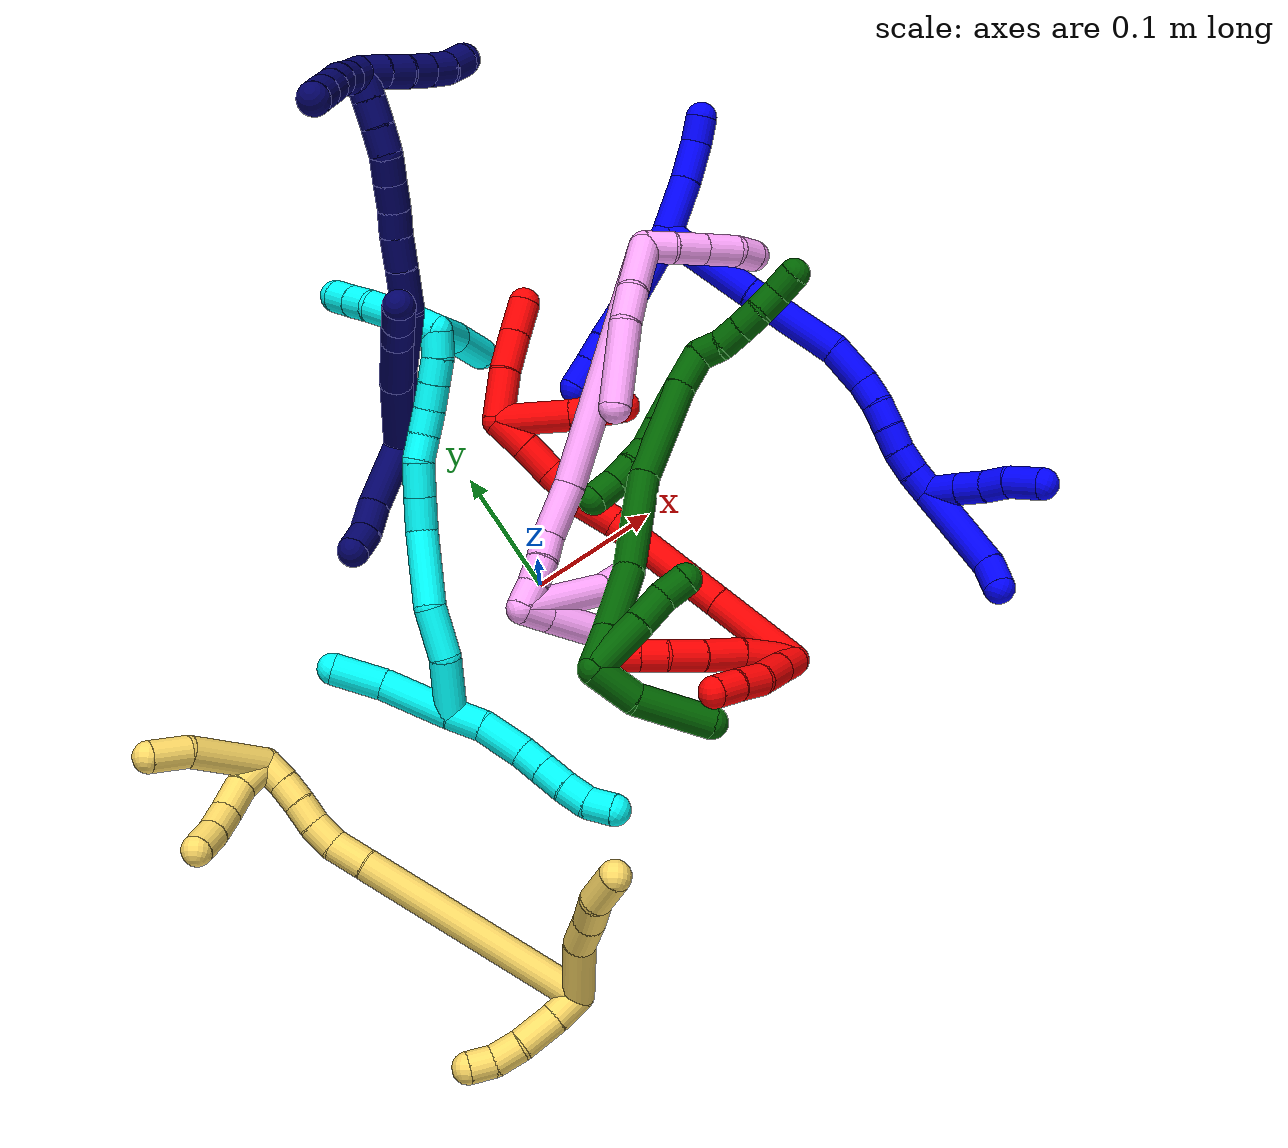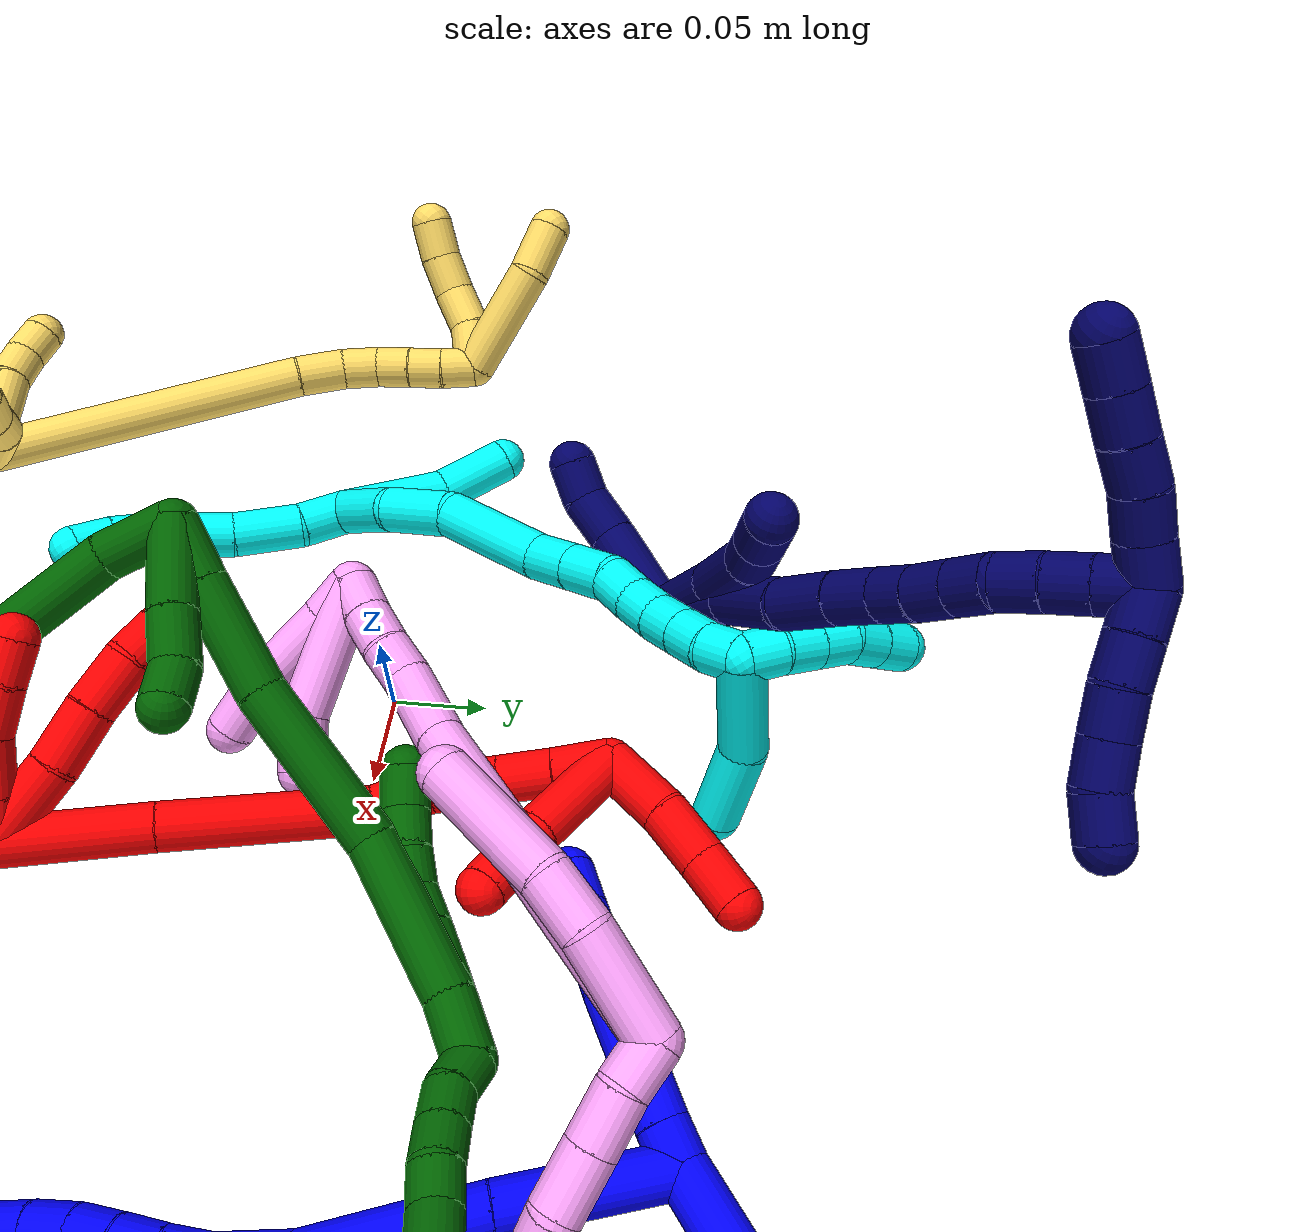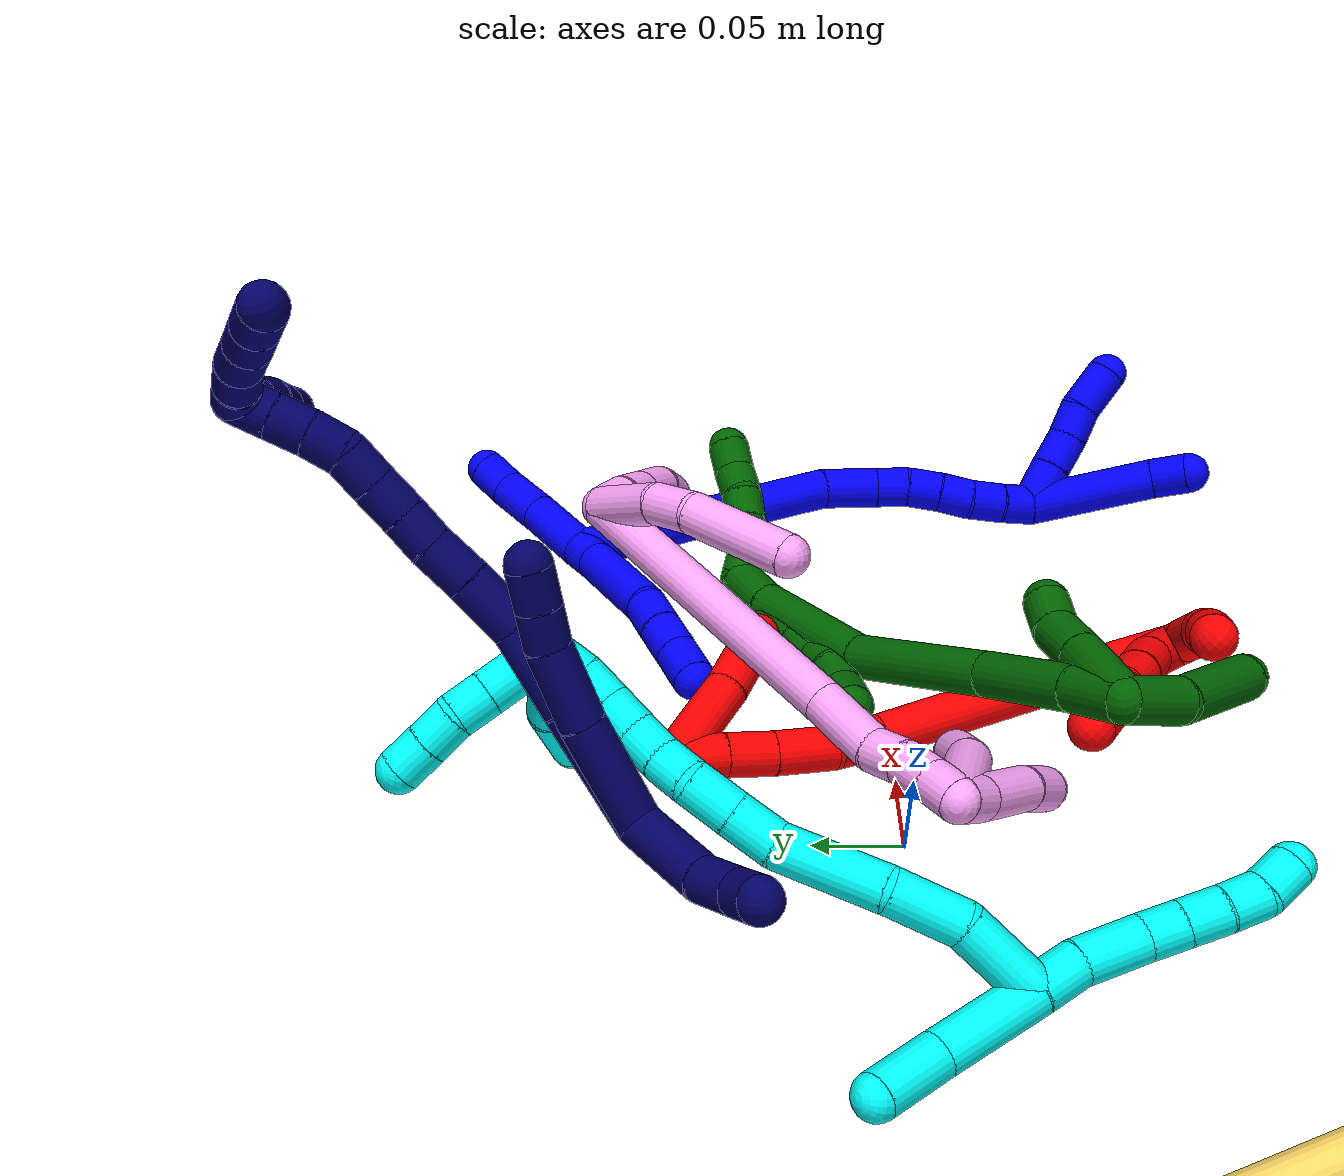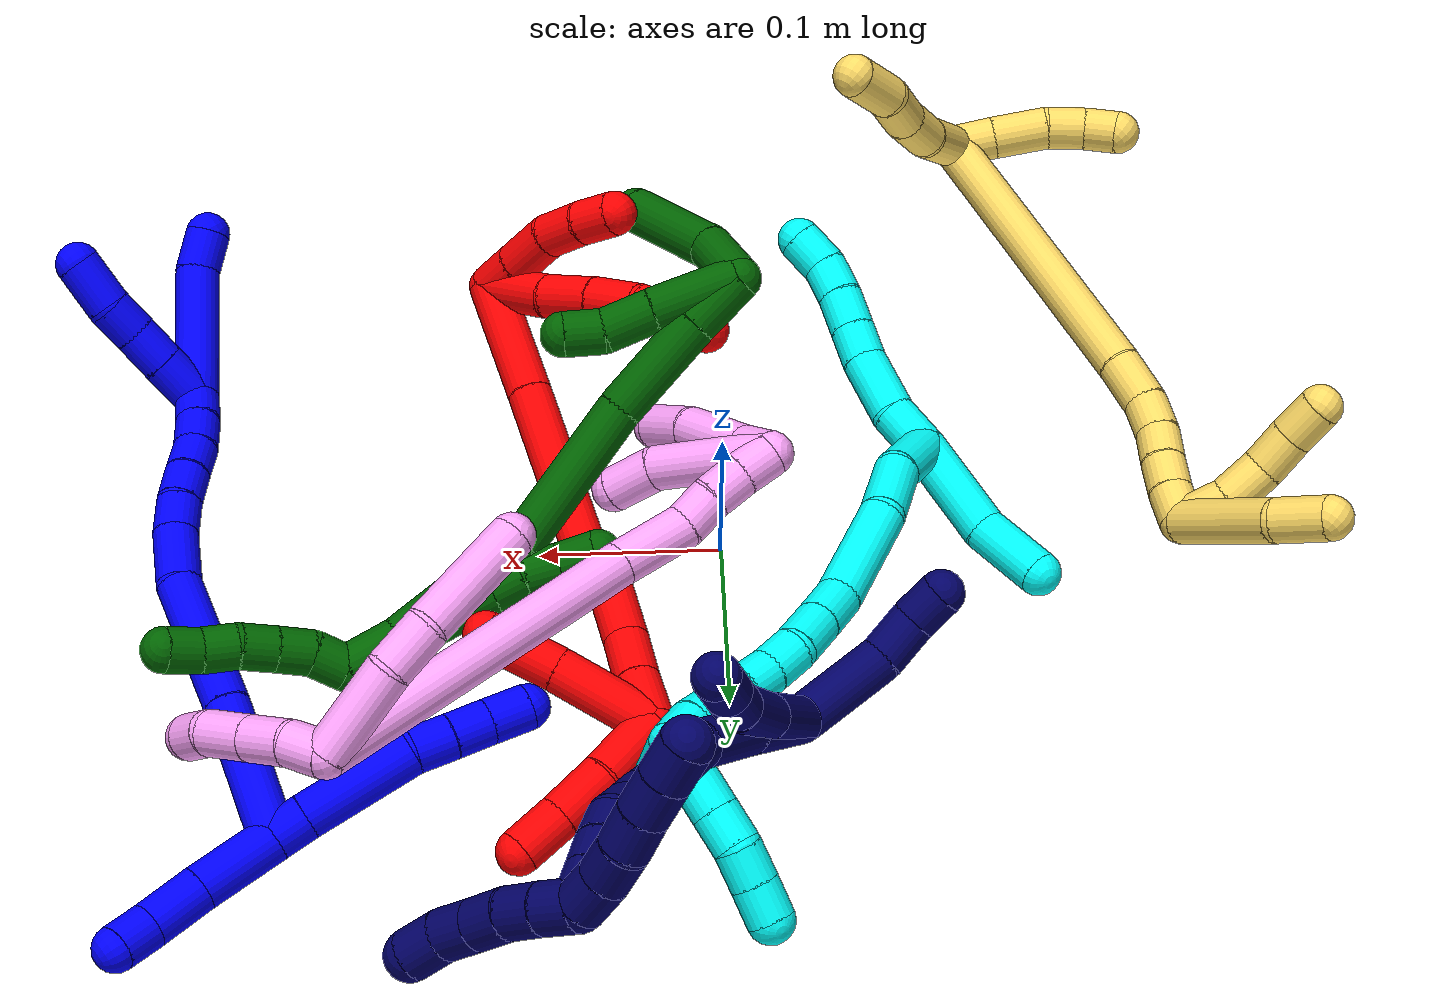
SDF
<sdf version="1.7">
 <world name="default">
  <plugin name="TubeGeneratorPlugin" filename="libtube_generator_plugin.so"/>
  <model name="photoneo_s_sensor">
   <static>1</static>
   <pose>0 0 2 1.57079 1.57079 3.14159</pose>
   <link name="link">
    <inertial><mass>0.1</mass></inertial>
    <sensor name="sensor" type="depth">
     <update_rate>30</update_rate>
     <camera>
      <horizontal_fov>1.22</horizontal_fov>
      <image><width>1920</width><height>1200</height><format>B8G8R8</format></image>
      <clip><near>0.1</near><far>4</far></clip>
      <depth_camera><output>points</output></depth_camera>
     </camera>
     <plugin name="camera_plugin" filename="libgazebo_ros_depth_camera.so">
      <baseline>0.2</baseline>
      <alwaysOn>1</alwaysOn>
      <updateRate>0.0</updateRate>
      <cameraName>camera_ir</cameraName>
      <imageTopicName>/camera/color/image_raw</imageTopicName>
      <cameraInfoTopicName>/camera/color/camera_info</cameraInfoTopicName>
      <depthImageTopicName>/camera/depth/image_raw</depthImageTopicName>
      <depthImageCameraInfoTopicName>/camera/depth/camera_info</depthImageCameraInfoTopicName>
      <pointCloudTopicName>/camera/depth/points</pointCloudTopicName>
      <frameName>fr_optical</frameName>
      <pointCloudCutoff>0.1</pointCloudCutoff>
      <pointCloudCutoffMax>2.0</pointCloudCutoffMax>
      <distortionK1>0</distortionK1>
      <distortionK2>0</distortionK2>
      <distortionK3>0</distortionK3>
      <distortionT1>0</distortionT1>
      <distortionT2>0</distortionT2>
      <CxPrime>0</CxPrime>
      <Cx>0</Cx>
      <Cy>0</Cy>
      <focalLength>0</focalLength>
      <hackBaseline>0</hackBaseline>
     </plugin>
    </sensor>
   </link>
  </model>
  <gravity>0 0 -9.8</gravity>
  <magnetic_field>6e-06 2.3e-05 -4.2e-05</magnetic_field>
  <atmosphere type="adiabatic"/>
  <physics name="default_physics" default="0" type="ode">
   <max_step_size>0.003</max_step_size>
   <real_time_factor>1</real_time_factor>
   <real_time_update_rate>1000</real_time_update_rate>
   <max_contacts>10000</max_contacts>
   <ode>
    <solver>
     <type>quick</type>
     <iters>100</iters>
     <sor>1.3</sor>
     <use_dynamic_moi_rescaling>0</use_dynamic_moi_rescaling>
    </solver>
    <constraints>
     <contact_max_correcting_vel>0</contact_max_correcting_vel>
     <contact_surface_layer>0.001</contact_surface_layer>
     <cfm>0</cfm>
     <erp>0.2</erp>
    </constraints>
   </ode>
  </physics>
  <scene><ambient>0.4 0.4 0.4 1</ambient><background>0.7 0.7 0.7 1</background><shadows>0</shadows></scene>
  <audio><device>default</device></audio>
  <spherical_coordinates>
   <surface_model>EARTH_WGS84</surface_model>
   <latitude_deg>0</latitude_deg>
   <longitude_deg>0</longitude_deg>
   <elevation>0</elevation>
   <heading_deg>0</heading_deg>
  </spherical_coordinates>
  <model name="bin">
   <static>1</static>
   <link name="bottom">
    <collision name="collision-bottom">
     <pose>0 0 -0.01 0 -0 0</pose>
     <geometry><box><size>0.8 0.6 0.02</size></box></geometry>
     <surface>
      <friction><ode><mu>100</mu><mu2>100</mu2></ode></friction>
      <contact><collide_bitmask>65535</collide_bitmask></contact>
     </surface>
    </collision>
   </link>
   <link name="west_wall">
    <collision name="collision-west_wall">
     <pose>-0.41 0 0.1 0 -0 0</pose>
     <geometry><box><size>0.02 0.6 0.2</size></box></geometry>
     <surface>
      <friction><ode><mu>100</mu><mu2>100</mu2></ode></friction>
      <contact><collide_bitmask>65535</collide_bitmask></contact>
     </surface>
    </collision>
   </link>
   <link name="east_wall">
    <collision name="collision-east_wall">
     <pose>0.41 0 0.1 0 -0 0</pose>
     <geometry><box><size>0.02 0.6 0.2</size></box></geometry>
     <surface>
      <friction><ode><mu>100</mu><mu2>100</mu2></ode></friction>
      <contact><collide_bitmask>65535</collide_bitmask></contact>
     </surface>
    </collision>
   </link>
   <link name="south_wall">
    <collision name="collision-south_wall">
     <pose>0 -0.31 0.1 0 -0 0</pose>
     <geometry><box><size>0.8 0.02 0.2</size></box></geometry>
     <surface>
      <friction><ode><mu>100</mu><mu2>100</mu2></ode></friction>
      <contact><collide_bitmask>65535</collide_bitmask></contact>
     </surface>
    </collision>
   </link>
   <link name="north_wall">
    <collision name="collision-north_wall">
     <pose>0 0.31 0.1 0 -0 0</pose>
     <geometry><box><size>0.8 0.02 0.2</size></box></geometry>
     <surface>
      <friction><ode><mu>100</mu><mu2>100</mu2></ode></friction>
      <contact><collide_bitmask>65535</collide_bitmask></contact>
     </surface>
    </collision>
   </link>
  </model>
  <model name="1">
   <static>0</static>
   <link name="1">
    <collision name="collision-cylinder-e_1_2_8">
     <pose>-0.001774 -0.000199 -0.009917 3.12157 -0.176949 -2.91687</pose>
     <geometry><cylinder><radius>0.0125</radius><length>0.020152</length></cylinder></geometry>
     <surface>
      <friction><ode><mu>1.16</mu><mu2>1.16</mu2><slip1>0</slip1><slip2>0</slip2></ode></friction>
      <contact><ode><kp>1e+06</kp><kd>1</kd><max_vel>0</max_vel><min_depth>0.001</min_depth></ode></contact>
     </surface>
    </collision>
    <visual name="visual-cylinder-e_1_2_8">
     <pose>-0.001774 -0.000199 -0.009917 3.12157 -0.176949 -2.91687</pose>
     <geometry><cylinder><radius>0.0125</radius><length>0.020152</length></cylinder></geometry>
     <material><ambient>0 0 1 1</ambient></material>
    </visual>
    <collision name="collision-cylinder-e_2_8_9">
     <pose>-0.00972 0.000424 -0.051223 -3.11543 -0.194121 2.87446</pose>
     <geometry><cylinder><radius>0.0125</radius><length>0.064002</length></cylinder></geometry>
     <surface>
      <friction><ode><mu>1.16</mu><mu2>1.16</mu2><slip1>0</slip1><slip2>0</slip2></ode></friction>
      <contact><ode><kp>1e+06</kp><kd>1</kd><max_vel>0</max_vel><min_depth>0.001</min_depth></ode></contact>
     </surface>
    </collision>
    <visual name="visual-cylinder-e_2_8_9">
     <pose>-0.00972 0.000424 -0.051223 -3.11543 -0.194121 2.87446</pose>
     <geometry><cylinder><radius>0.0125</radius><length>0.064002</length></cylinder></geometry>
     <material><ambient>0 0 1 1</ambient></material>
    </visual>
    <collision name="collision-cylinder-e_3_9_10">
     <pose>-0.016187 0.003443 -0.09323 -2.93759 -0.027031 0.262577</pose>
     <geometry><cylinder><radius>0.0125</radius><length>0.021694</length></cylinder></geometry>
     <surface>
      <friction><ode><mu>1.16</mu><mu2>1.16</mu2><slip1>0</slip1><slip2>0</slip2></ode></friction>
      <contact><ode><kp>1e+06</kp><kd>1</kd><max_vel>0</max_vel><min_depth>0.001</min_depth></ode></contact>
     </surface>
    </collision>
    <visual name="visual-cylinder-e_3_9_10">
     <pose>-0.016187 0.003443 -0.09323 -2.93759 -0.027031 0.262577</pose>
     <geometry><cylinder><radius>0.0125</radius><length>0.021694</length></cylinder></geometry>
     <material><ambient>0 0 1 1</ambient></material>
    </visual>
    <collision name="collision-cylinder-e_4_10_11">
     <pose>-0.016253 0.007673 -0.114358 -2.95049 0.021172 -0.22002</pose>
     <geometry><cylinder><radius>0.0125</radius><length>0.021414</length></cylinder></geometry>
     <surface>
      <friction><ode><mu>1.16</mu><mu2>1.16</mu2><slip1>0</slip1><slip2>0</slip2></ode></friction>
      <contact><ode><kp>1e+06</kp><kd>1</kd><max_vel>0</max_vel><min_depth>0.001</min_depth></ode></contact>
     </surface>
    </collision>
    <visual name="visual-cylinder-e_4_10_11">
     <pose>-0.016253 0.007673 -0.114358 -2.95049 0.021172 -0.22002</pose>
     <geometry><cylinder><radius>0.0125</radius><length>0.021414</length></cylinder></geometry>
     <material><ambient>0 0 1 1</ambient></material>
    </visual>
    <collision name="collision-cylinder-e_5_11_6">
     <pose>-0.016149 0.01202 -0.135998 -2.93657 -0.010806 0.104949</pose>
     <geometry><cylinder><radius>0.0125</radius><length>0.022738</length></cylinder></geometry>
     <surface>
      <friction><ode><mu>1.16</mu><mu2>1.16</mu2><slip1>0</slip1><slip2>0</slip2></ode></friction>
      <contact><ode><kp>1e+06</kp><kd>1</kd><max_vel>0</max_vel><min_depth>0.001</min_depth></ode></contact>
     </surface>
    </collision>
    <visual name="visual-cylinder-e_5_11_6">
     <pose>-0.016149 0.01202 -0.135998 -2.93657 -0.010806 0.104949</pose>
     <geometry><cylinder><radius>0.0125</radius><length>0.022738</length></cylinder></geometry>
     <material><ambient>0 0 1 1</ambient></material>
    </visual>
    <collision name="collision-cylinder-e_1_2_12">
     <pose>-0.000953 0.00052 0.022954 -0.022671 -0.041471 0.00047</pose>
     <geometry><cylinder><radius>0.0125</radius><length>0.045959</length></cylinder></geometry>
     <surface>
      <friction><ode><mu>1.16</mu><mu2>1.16</mu2><slip1>0</slip1><slip2>0</slip2></ode></friction>
      <contact><ode><kp>1e+06</kp><kd>1</kd><max_vel>0</max_vel><min_depth>0.001</min_depth></ode></contact>
     </surface>
    </collision>
    <visual name="visual-cylinder-e_1_2_12">
     <pose>-0.000953 0.00052 0.022954 -0.022671 -0.041471 0.00047</pose>
     <geometry><cylinder><radius>0.0125</radius><length>0.045959</length></cylinder></geometry>
     <material><ambient>0 0 1 1</ambient></material>
    </visual>
    <collision name="collision-cylinder-e_2_12_13">
     <pose>-0.003577 0.002063 0.062003 -0.063434 -0.103253 0.003279</pose>
     <geometry><cylinder><radius>0.0125</radius><length>0.032428</length></cylinder></geometry>
     <surface>
      <friction><ode><mu>1.16</mu><mu2>1.16</mu2><slip1>0</slip1><slip2>0</slip2></ode></friction>
      <contact><ode><kp>1e+06</kp><kd>1</kd><max_vel>0</max_vel><min_depth>0.001</min_depth></ode></contact>
     </surface>
    </collision>
    <visual name="visual-cylinder-e_2_12_13">
     <pose>-0.003577 0.002063 0.062003 -0.063434 -0.103253 0.003279</pose>
     <geometry><cylinder><radius>0.0125</radius><length>0.032428</length></cylinder></geometry>
     <material><ambient>0 0 1 1</ambient></material>
    </visual>
    <collision name="collision-cylinder-e_3_13_5">
     <pose>-0.008436 0.003406 0.088419 -0.031023 -0.299456 0.00468</pose>
     <geometry><cylinder><radius>0.0125</radius><length>0.021613</length></cylinder></geometry>
     <surface>
      <friction><ode><mu>1.16</mu><mu2>1.16</mu2><slip1>0</slip1><slip2>0</slip2></ode></friction>
      <contact><ode><kp>1e+06</kp><kd>1</kd><max_vel>0</max_vel><min_depth>0.001</min_depth></ode></contact>
     </surface>
    </collision>
    <visual name="visual-cylinder-e_3_13_5">
     <pose>-0.008436 0.003406 0.088419 -0.031023 -0.299456 0.00468</pose>
     <geometry><cylinder><radius>0.0125</radius><length>0.021613</length></cylinder></geometry>
     <material><ambient>0 0 1 1</ambient></material>
    </visual>
    <collision name="collision-cylinder-e_1_2_14">
     <pose>0.015651 -0.036217 -0.011678 1.88272 0.390192 0.529933</pose>
     <geometry><cylinder><radius>0.0125</radius><length>0.082293</length></cylinder></geometry>
     <surface>
      <friction><ode><mu>1.16</mu><mu2>1.16</mu2><slip1>0</slip1><slip2>0</slip2></ode></friction>
      <contact><ode><kp>1e+06</kp><kd>1</kd><max_vel>0</max_vel><min_depth>0.001</min_depth></ode></contact>
     </surface>
    </collision>
    <visual name="visual-cylinder-e_1_2_14">
     <pose>0.015651 -0.036217 -0.011678 1.88272 0.390192 0.529933</pose>
     <geometry><cylinder><radius>0.0125</radius><length>0.082293</length></cylinder></geometry>
     <material><ambient>0 0 1 1</ambient></material>
    </visual>
    <collision name="collision-cylinder-e_2_14_15">
     <pose>0.048792 -0.107766 -0.033529 1.85114 0.444029 0.582732</pose>
     <geometry><cylinder><radius>0.0125</radius><length>0.081429</length></cylinder></geometry>
     <surface>
      <friction><ode><mu>1.16</mu><mu2>1.16</mu2><slip1>0</slip1><slip2>0</slip2></ode></friction>
      <contact><ode><kp>1e+06</kp><kd>1</kd><max_vel>0</max_vel><min_depth>0.001</min_depth></ode></contact>
     </surface>
    </collision>
    <visual name="visual-cylinder-e_2_14_15">
     <pose>0.048792 -0.107766 -0.033529 1.85114 0.444029 0.582732</pose>
     <geometry><cylinder><radius>0.0125</radius><length>0.081429</length></cylinder></geometry>
     <material><ambient>0 0 1 1</ambient></material>
    </visual>
    <collision name="collision-cylinder-e_3_15_16">
     <pose>0.074236 -0.156221 -0.052003 2.1348 0.473363 0.82562</pose>
     <geometry><cylinder><radius>0.0125</radius><length>0.034895</length></cylinder></geometry>
     <surface>
      <friction><ode><mu>1.16</mu><mu2>1.16</mu2><slip1>0</slip1><slip2>0</slip2></ode></friction>
      <contact><ode><kp>1e+06</kp><kd>1</kd><max_vel>0</max_vel><min_depth>0.001</min_depth></ode></contact>
     </surface>
    </collision>
    <visual name="visual-cylinder-e_3_15_16">
     <pose>0.074236 -0.156221 -0.052003 2.1348 0.473363 0.82562</pose>
     <geometry><cylinder><radius>0.0125</radius><length>0.034895</length></cylinder></geometry>
     <material><ambient>0 0 1 1</ambient></material>
    </visual>
    <collision name="collision-cylinder-e_4_16_17">
     <pose>0.085327 -0.176779 -0.066743 2.28456 0.308837 0.656796</pose>
     <geometry><cylinder><radius>0.0125</radius><length>0.020646</length></cylinder></geometry>
     <surface>
      <friction><ode><mu>1.16</mu><mu2>1.16</mu2><slip1>0</slip1><slip2>0</slip2></ode></friction>
      <contact><ode><kp>1e+06</kp><kd>1</kd><max_vel>0</max_vel><min_depth>0.001</min_depth></ode></contact>
     </surface>
    </collision>
    <visual name="visual-cylinder-e_4_16_17">
     <pose>0.085327 -0.176779 -0.066743 2.28456 0.308837 0.656796</pose>
     <geometry><cylinder><radius>0.0125</radius><length>0.020646</length></cylinder></geometry>
     <material><ambient>0 0 1 1</ambient></material>
    </visual>
    <collision name="collision-cylinder-e_5_17_18">
     <pose>0.092622 -0.190211 -0.080205 2.43473 0.422904 1.05394</pose>
     <geometry><cylinder><radius>0.0125</radius><length>0.020257</length></cylinder></geometry>
     <surface>
      <friction><ode><mu>1.16</mu><mu2>1.16</mu2><slip1>0</slip1><slip2>0</slip2></ode></friction>
      <contact><ode><kp>1e+06</kp><kd>1</kd><max_vel>0</max_vel><min_depth>0.001</min_depth></ode></contact>
     </surface>
    </collision>
    <visual name="visual-cylinder-e_5_17_18">
     <pose>0.092622 -0.190211 -0.080205 2.43473 0.422904 1.05394</pose>
     <geometry><cylinder><radius>0.0125</radius><length>0.020257</length></cylinder></geometry>
     <material><ambient>0 0 1 1</ambient></material>
    </visual>
    <collision name="collision-cylinder-e_6_18_19">
     <pose>0.101656 -0.201626 -0.094087 2.47326 0.50903 1.28614</pose>
     <geometry><cylinder><radius>0.0125</radius><length>0.020017</length></cylinder></geometry>
     <surface>
      <friction><ode><mu>1.16</mu><mu2>1.16</mu2><slip1>0</slip1><slip2>0</slip2></ode></friction>
      <contact><ode><kp>1e+06</kp><kd>1</kd><max_vel>0</max_vel><min_depth>0.001</min_depth></ode></contact>
     </surface>
    </collision>
    <visual name="visual-cylinder-e_6_18_19">
     <pose>0.101656 -0.201626 -0.094087 2.47326 0.50903 1.28614</pose>
     <geometry><cylinder><radius>0.0125</radius><length>0.020017</length></cylinder></geometry>
     <material><ambient>0 0 1 1</ambient></material>
    </visual>
    <collision name="collision-cylinder-e_7_19_20">
     <pose>0.111647 -0.213697 -0.106774 2.28992 0.52408 1.06799</pose>
     <geometry><cylinder><radius>0.0125</radius><length>0.020435</length></cylinder></geometry>
     <surface>
      <friction><ode><mu>1.16</mu><mu2>1.16</mu2><slip1>0</slip1><slip2>0</slip2></ode></friction>
      <contact><ode><kp>1e+06</kp><kd>1</kd><max_vel>0</max_vel><min_depth>0.001</min_depth></ode></contact>
     </surface>
    </collision>
    <visual name="visual-cylinder-e_7_19_20">
     <pose>0.111647 -0.213697 -0.106774 2.28992 0.52408 1.06799</pose>
     <geometry><cylinder><radius>0.0125</radius><length>0.020435</length></cylinder></geometry>
     <material><ambient>0 0 1 1</ambient></material>
    </visual>
    <collision name="collision-cylinder-e_8_20_1">
     <pose>0.122064 -0.22735 -0.117415 2.17341 0.558218 0.998039</pose>
     <geometry><cylinder><radius>0.0125</radius><length>0.020028</length></cylinder></geometry>
     <surface>
      <friction><ode><mu>1.16</mu><mu2>1.16</mu2><slip1>0</slip1><slip2>0</slip2></ode></friction>
      <contact><ode><kp>1e+06</kp><kd>1</kd><max_vel>0</max_vel><min_depth>0.001</min_depth></ode></contact>
     </surface>
    </collision>
    <visual name="visual-cylinder-e_8_20_1">
     <pose>0.122064 -0.22735 -0.117415 2.17341 0.558218 0.998039</pose>
     <geometry><cylinder><radius>0.0125</radius><length>0.020028</length></cylinder></geometry>
     <material><ambient>0 0 1 1</ambient></material>
    </visual>
    <collision name="collision-cylinder-e_1_1_21">
     <pose>0.132415 -0.266149 -0.143618 2.16287 0.130938 0.244981</pose>
     <geometry><cylinder><radius>0.0125</radius><length>0.07731</length></cylinder></geometry>
     <surface>
      <friction><ode><mu>1.16</mu><mu2>1.16</mu2><slip1>0</slip1><slip2>0</slip2></ode></friction>
      <contact><ode><kp>1e+06</kp><kd>1</kd><max_vel>0</max_vel><min_depth>0.001</min_depth></ode></contact>
     </surface>
    </collision>
    <visual name="visual-cylinder-e_1_1_21">
     <pose>0.132415 -0.266149 -0.143618 2.16287 0.130938 0.244981</pose>
     <geometry><cylinder><radius>0.0125</radius><length>0.07731</length></cylinder></geometry>
     <material><ambient>0 0 1 1</ambient></material>
    </visual>
    <collision name="collision-cylinder-e_2_21_4">
     <pose>0.136604 -0.305666 -0.173278 2.39101 -0.075745 -0.191766</pose>
     <geometry><cylinder><radius>0.0125</radius><length>0.02269</length></cylinder></geometry>
     <surface>
      <friction><ode><mu>1.16</mu><mu2>1.16</mu2><slip1>0</slip1><slip2>0</slip2></ode></friction>
      <contact><ode><kp>1e+06</kp><kd>1</kd><max_vel>0</max_vel><min_depth>0.001</min_depth></ode></contact>
     </surface>
    </collision>
    <visual name="visual-cylinder-e_2_21_4">
     <pose>0.136604 -0.305666 -0.173278 2.39101 -0.075745 -0.191766</pose>
     <geometry><cylinder><radius>0.0125</radius><length>0.02269</length></cylinder></geometry>
     <material><ambient>0 0 1 1</ambient></material>
    </visual>
    <collision name="collision-cylinder-e_1_1_22">
     <pose>0.12479 -0.247321 -0.118863 1.31686 -0.190064 -0.14721</pose>
     <geometry><cylinder><radius>0.0125</radius><length>0.027296</length></cylinder></geometry>
     <surface>
      <friction><ode><mu>1.16</mu><mu2>1.16</mu2><slip1>0</slip1><slip2>0</slip2></ode></friction>
      <contact><ode><kp>1e+06</kp><kd>1</kd><max_vel>0</max_vel><min_depth>0.001</min_depth></ode></contact>
     </surface>
    </collision>
    <visual name="visual-cylinder-e_1_1_22">
     <pose>0.12479 -0.247321 -0.118863 1.31686 -0.190064 -0.14721</pose>
     <geometry><cylinder><radius>0.0125</radius><length>0.027296</length></cylinder></geometry>
     <material><ambient>0 0 1 1</ambient></material>
    </visual>
    <collision name="collision-cylinder-e_2_22_23">
     <pose>0.120264 -0.271258 -0.112878 1.33641 -0.171077 -0.135161</pose>
     <geometry><cylinder><radius>0.0125</radius><length>0.02288</length></cylinder></geometry>
     <surface>
      <friction><ode><mu>1.16</mu><mu2>1.16</mu2><slip1>0</slip1><slip2>0</slip2></ode></friction>
      <contact><ode><kp>1e+06</kp><kd>1</kd><max_vel>0</max_vel><min_depth>0.001</min_depth></ode></contact>
     </surface>
    </collision>
    <visual name="visual-cylinder-e_2_22_23">
     <pose>0.120264 -0.271258 -0.112878 1.33641 -0.171077 -0.135161</pose>
     <geometry><cylinder><radius>0.0125</radius><length>0.02288</length></cylinder></geometry>
     <material><ambient>0 0 1 1</ambient></material>
    </visual>
    <collision name="collision-cylinder-e_3_23_24">
     <pose>0.115311 -0.291893 -0.107456 1.28861 -0.290047 -0.218565</pose>
     <geometry><cylinder><radius>0.0125</radius><length>0.021016</length></cylinder></geometry>
     <surface>
      <friction><ode><mu>1.16</mu><mu2>1.16</mu2><slip1>0</slip1><slip2>0</slip2></ode></friction>
      <contact><ode><kp>1e+06</kp><kd>1</kd><max_vel>0</max_vel><min_depth>0.001</min_depth></ode></contact>
     </surface>
    </collision>
    <visual name="visual-cylinder-e_3_23_24">
     <pose>0.115311 -0.291893 -0.107456 1.28861 -0.290047 -0.218565</pose>
     <geometry><cylinder><radius>0.0125</radius><length>0.021016</length></cylinder></geometry>
     <material><ambient>0 0 1 1</ambient></material>
    </visual>
    <collision name="collision-cylinder-e_4_24_3">
     <pose>0.11012 -0.315736 -0.103285 1.47465 -0.152313 -0.138376</pose>
     <geometry><cylinder><radius>0.0125</radius><length>0.028808</length></cylinder></geometry>
     <surface>
      <friction><ode><mu>1.16</mu><mu2>1.16</mu2><slip1>0</slip1><slip2>0</slip2></ode></friction>
      <contact><ode><kp>1e+06</kp><kd>1</kd><max_vel>0</max_vel><min_depth>0.001</min_depth></ode></contact>
     </surface>
    </collision>
    <visual name="visual-cylinder-e_4_24_3">
     <pose>0.11012 -0.315736 -0.103285 1.47465 -0.152313 -0.138376</pose>
     <geometry><cylinder><radius>0.0125</radius><length>0.028808</length></cylinder></geometry>
     <material><ambient>0 0 1 1</ambient></material>
    </visual>
    <collision name="collision-sphere-3">
     <pose>0.107935 -0.329907 -0.101918 0 -0 0</pose>
     <geometry><sphere><radius>0.0125</radius></sphere></geometry>
     <surface>
      <friction><ode><mu>1.16</mu><mu2>1.16</mu2><slip1>0</slip1><slip2>0</slip2></ode></friction>
      <contact><ode><kp>1e+06</kp><kd>1</kd><max_vel>0</max_vel><min_depth>0.001</min_depth></ode></contact>
     </surface>
    </collision>
    <visual name="visual-sphere-3">
     <pose>0.107935 -0.329907 -0.101918 0 -0 0</pose>
     <geometry><sphere><radius>0.0125</radius></sphere></geometry>
     <material><ambient>0 0 1 1</ambient></material>
    </visual>
    <collision name="collision-sphere-24">
     <pose>0.112306 -0.301564 -0.104652 0 -0 0</pose>
     <geometry><sphere><radius>0.0125</radius></sphere></geometry>
     <surface>
      <friction><ode><mu>1.16</mu><mu2>1.16</mu2><slip1>0</slip1><slip2>0</slip2></ode></friction>
      <contact><ode><kp>1e+06</kp><kd>1</kd><max_vel>0</max_vel><min_depth>0.001</min_depth></ode></contact>
     </surface>
    </collision>
    <visual name="visual-sphere-24">
     <pose>0.112306 -0.301564 -0.104652 0 -0 0</pose>
     <geometry><sphere><radius>0.0125</radius></sphere></geometry>
     <material><ambient>0 0 1 1</ambient></material>
    </visual>
    <collision name="collision-sphere-23">
     <pose>0.118316 -0.282222 -0.11026 0 -0 0</pose>
     <geometry><sphere><radius>0.0125</radius></sphere></geometry>
     <surface>
      <friction><ode><mu>1.16</mu><mu2>1.16</mu2><slip1>0</slip1><slip2>0</slip2></ode></friction>
      <contact><ode><kp>1e+06</kp><kd>1</kd><max_vel>0</max_vel><min_depth>0.001</min_depth></ode></contact>
     </surface>
    </collision>
    <visual name="visual-sphere-23">
     <pose>0.118316 -0.282222 -0.11026 0 -0 0</pose>
     <geometry><sphere><radius>0.0125</radius></sphere></geometry>
     <material><ambient>0 0 1 1</ambient></material>
    </visual>
    <collision name="collision-sphere-22">
     <pose>0.122211 -0.260293 -0.115496 0 -0 0</pose>
     <geometry><sphere><radius>0.0125</radius></sphere></geometry>
     <surface>
      <friction><ode><mu>1.16</mu><mu2>1.16</mu2><slip1>0</slip1><slip2>0</slip2></ode></friction>
      <contact><ode><kp>1e+06</kp><kd>1</kd><max_vel>0</max_vel><min_depth>0.001</min_depth></ode></contact>
     </surface>
    </collision>
    <visual name="visual-sphere-22">
     <pose>0.122211 -0.260293 -0.115496 0 -0 0</pose>
     <geometry><sphere><radius>0.0125</radius></sphere></geometry>
     <material><ambient>0 0 1 1</ambient></material>
    </visual>
    <collision name="collision-sphere-4">
     <pose>0.135745 -0.313382 -0.181551 0 -0 0</pose>
     <geometry><sphere><radius>0.0125</radius></sphere></geometry>
     <surface>
      <friction><ode><mu>1.16</mu><mu2>1.16</mu2><slip1>0</slip1><slip2>0</slip2></ode></friction>
      <contact><ode><kp>1e+06</kp><kd>1</kd><max_vel>0</max_vel><min_depth>0.001</min_depth></ode></contact>
     </surface>
    </collision>
    <visual name="visual-sphere-4">
     <pose>0.135745 -0.313382 -0.181551 0 -0 0</pose>
     <geometry><sphere><radius>0.0125</radius></sphere></geometry>
     <material><ambient>0 0 1 1</ambient></material>
    </visual>
    <collision name="collision-sphere-21">
     <pose>0.137462 -0.29795 -0.165006 0 -0 0</pose>
     <geometry><sphere><radius>0.0125</radius></sphere></geometry>
     <surface>
      <friction><ode><mu>1.16</mu><mu2>1.16</mu2><slip1>0</slip1><slip2>0</slip2></ode></friction>
      <contact><ode><kp>1e+06</kp><kd>1</kd><max_vel>0</max_vel><min_depth>0.001</min_depth></ode></contact>
     </surface>
    </collision>
    <visual name="visual-sphere-21">
     <pose>0.137462 -0.29795 -0.165006 0 -0 0</pose>
     <geometry><sphere><radius>0.0125</radius></sphere></geometry>
     <material><ambient>0 0 1 1</ambient></material>
    </visual>
    <collision name="collision-sphere-1">
     <pose>0.127368 -0.234348 -0.12223 0 -0 0</pose>
     <geometry><sphere><radius>0.0125</radius></sphere></geometry>
     <surface>
      <friction><ode><mu>1.16</mu><mu2>1.16</mu2><slip1>0</slip1><slip2>0</slip2></ode></friction>
      <contact><ode><kp>1e+06</kp><kd>1</kd><max_vel>0</max_vel><min_depth>0.001</min_depth></ode></contact>
     </surface>
    </collision>
    <visual name="visual-sphere-1">
     <pose>0.127368 -0.234348 -0.12223 0 -0 0</pose>
     <geometry><sphere><radius>0.0125</radius></sphere></geometry>
     <material><ambient>0 0 1 1</ambient></material>
    </visual>
    <collision name="collision-sphere-6">
     <pose>-0.016272 0.014335 -0.147128 0 -0 0</pose>
     <geometry><sphere><radius>0.0125</radius></sphere></geometry>
     <surface>
      <friction><ode><mu>1.16</mu><mu2>1.16</mu2><slip1>0</slip1><slip2>0</slip2></ode></friction>
      <contact><ode><kp>1e+06</kp><kd>1</kd><max_vel>0</max_vel><min_depth>0.001</min_depth></ode></contact>
     </surface>
    </collision>
    <visual name="visual-sphere-6">
     <pose>-0.016272 0.014335 -0.147128 0 -0 0</pose>
     <geometry><sphere><radius>0.0125</radius></sphere></geometry>
     <material><ambient>0 0 1 1</ambient></material>
    </visual>
    <collision name="collision-sphere-11">
     <pose>-0.016027 0.009706 -0.124868 0 -0 0</pose>
     <geometry><sphere><radius>0.0125</radius></sphere></geometry>
     <surface>
      <friction><ode><mu>1.16</mu><mu2>1.16</mu2><slip1>0</slip1><slip2>0</slip2></ode></friction>
      <contact><ode><kp>1e+06</kp><kd>1</kd><max_vel>0</max_vel><min_depth>0.001</min_depth></ode></contact>
     </surface>
    </collision>
    <visual name="visual-sphere-11">
     <pose>-0.016027 0.009706 -0.124868 0 -0 0</pose>
     <geometry><sphere><radius>0.0125</radius></sphere></geometry>
     <material><ambient>0 0 1 1</ambient></material>
    </visual>
    <collision name="collision-sphere-10">
     <pose>-0.01648 0.005639 -0.103848 0 -0 0</pose>
     <geometry><sphere><radius>0.0125</radius></sphere></geometry>
     <surface>
      <friction><ode><mu>1.16</mu><mu2>1.16</mu2><slip1>0</slip1><slip2>0</slip2></ode></friction>
      <contact><ode><kp>1e+06</kp><kd>1</kd><max_vel>0</max_vel><min_depth>0.001</min_depth></ode></contact>
     </surface>
    </collision>
    <visual name="visual-sphere-10">
     <pose>-0.01648 0.005639 -0.103848 0 -0 0</pose>
     <geometry><sphere><radius>0.0125</radius></sphere></geometry>
     <material><ambient>0 0 1 1</ambient></material>
    </visual>
    <collision name="collision-sphere-9">
     <pose>-0.015894 0.001246 -0.082612 0 -0 0</pose>
     <geometry><sphere><radius>0.0125</radius></sphere></geometry>
     <surface>
      <friction><ode><mu>1.16</mu><mu2>1.16</mu2><slip1>0</slip1><slip2>0</slip2></ode></friction>
      <contact><ode><kp>1e+06</kp><kd>1</kd><max_vel>0</max_vel><min_depth>0.001</min_depth></ode></contact>
     </surface>
    </collision>
    <visual name="visual-sphere-9">
     <pose>-0.015894 0.001246 -0.082612 0 -0 0</pose>
     <geometry><sphere><radius>0.0125</radius></sphere></geometry>
     <material><ambient>0 0 1 1</ambient></material>
    </visual>
    <collision name="collision-sphere-2">
     <geometry><sphere><radius>0.0125</radius></sphere></geometry>
     <surface>
      <friction><ode><mu>1.16</mu><mu2>1.16</mu2><slip1>0</slip1><slip2>0</slip2></ode></friction>
      <contact><ode><kp>1e+06</kp><kd>1</kd><max_vel>0</max_vel><min_depth>0.001</min_depth></ode></contact>
     </surface>
    </collision>
    <visual name="visual-sphere-2">
     <geometry><sphere><radius>0.0125</radius></sphere></geometry>
     <material><ambient>0 0 1 1</ambient></material>
    </visual>
    <collision name="collision-sphere-19">
     <pose>0.106534 -0.207041 -0.100947 0 -0 0</pose>
     <geometry><sphere><radius>0.0125</radius></sphere></geometry>
     <surface>
      <friction><ode><mu>1.16</mu><mu2>1.16</mu2><slip1>0</slip1><slip2>0</slip2></ode></friction>
      <contact><ode><kp>1e+06</kp><kd>1</kd><max_vel>0</max_vel><min_depth>0.001</min_depth></ode></contact>
     </surface>
    </collision>
    <visual name="visual-sphere-19">
     <pose>0.106534 -0.207041 -0.100947 0 -0 0</pose>
     <geometry><sphere><radius>0.0125</radius></sphere></geometry>
     <material><ambient>0 0 1 1</ambient></material>
    </visual>
    <collision name="collision-sphere-8">
     <pose>-0.003547 -0.000397 -0.019833 0 -0 0</pose>
     <geometry><sphere><radius>0.0125</radius></sphere></geometry>
     <surface>
      <friction><ode><mu>1.16</mu><mu2>1.16</mu2><slip1>0</slip1><slip2>0</slip2></ode></friction>
      <contact><ode><kp>1e+06</kp><kd>1</kd><max_vel>0</max_vel><min_depth>0.001</min_depth></ode></contact>
     </surface>
    </collision>
    <visual name="visual-sphere-8">
     <pose>-0.003547 -0.000397 -0.019833 0 -0 0</pose>
     <geometry><sphere><radius>0.0125</radius></sphere></geometry>
     <material><ambient>0 0 1 1</ambient></material>
    </visual>
    <collision name="collision-sphere-12">
     <pose>-0.001905 0.001041 0.045908 0 -0 0</pose>
     <geometry><sphere><radius>0.0125</radius></sphere></geometry>
     <surface>
      <friction><ode><mu>1.16</mu><mu2>1.16</mu2><slip1>0</slip1><slip2>0</slip2></ode></friction>
      <contact><ode><kp>1e+06</kp><kd>1</kd><max_vel>0</max_vel><min_depth>0.001</min_depth></ode></contact>
     </surface>
    </collision>
    <visual name="visual-sphere-12">
     <pose>-0.001905 0.001041 0.045908 0 -0 0</pose>
     <geometry><sphere><radius>0.0125</radius></sphere></geometry>
     <material><ambient>0 0 1 1</ambient></material>
    </visual>
    <collision name="collision-sphere-13">
     <pose>-0.005248 0.003086 0.078098 0 -0 0</pose>
     <geometry><sphere><radius>0.0125</radius></sphere></geometry>
     <surface>
      <friction><ode><mu>1.16</mu><mu2>1.16</mu2><slip1>0</slip1><slip2>0</slip2></ode></friction>
      <contact><ode><kp>1e+06</kp><kd>1</kd><max_vel>0</max_vel><min_depth>0.001</min_depth></ode></contact>
     </surface>
    </collision>
    <visual name="visual-sphere-13">
     <pose>-0.005248 0.003086 0.078098 0 -0 0</pose>
     <geometry><sphere><radius>0.0125</radius></sphere></geometry>
     <material><ambient>0 0 1 1</ambient></material>
    </visual>
    <collision name="collision-sphere-5">
     <pose>-0.011624 0.003726 0.098739 0 -0 0</pose>
     <geometry><sphere><radius>0.0125</radius></sphere></geometry>
     <surface>
      <friction><ode><mu>1.16</mu><mu2>1.16</mu2><slip1>0</slip1><slip2>0</slip2></ode></friction>
      <contact><ode><kp>1e+06</kp><kd>1</kd><max_vel>0</max_vel><min_depth>0.001</min_depth></ode></contact>
     </surface>
    </collision>
    <visual name="visual-sphere-5">
     <pose>-0.011624 0.003726 0.098739 0 -0 0</pose>
     <geometry><sphere><radius>0.0125</radius></sphere></geometry>
     <material><ambient>0 0 1 1</ambient></material>
    </visual>
    <collision name="collision-sphere-14">
     <pose>0.031301 -0.072435 -0.023356 0 -0 0</pose>
     <geometry><sphere><radius>0.0125</radius></sphere></geometry>
     <surface>
      <friction><ode><mu>1.16</mu><mu2>1.16</mu2><slip1>0</slip1><slip2>0</slip2></ode></friction>
      <contact><ode><kp>1e+06</kp><kd>1</kd><max_vel>0</max_vel><min_depth>0.001</min_depth></ode></contact>
     </surface>
    </collision>
    <visual name="visual-sphere-14">
     <pose>0.031301 -0.072435 -0.023356 0 -0 0</pose>
     <geometry><sphere><radius>0.0125</radius></sphere></geometry>
     <material><ambient>0 0 1 1</ambient></material>
    </visual>
    <collision name="collision-sphere-15">
     <pose>0.066282 -0.143097 -0.043702 0 -0 0</pose>
     <geometry><sphere><radius>0.0125</radius></sphere></geometry>
     <surface>
      <friction><ode><mu>1.16</mu><mu2>1.16</mu2><slip1>0</slip1><slip2>0</slip2></ode></friction>
      <contact><ode><kp>1e+06</kp><kd>1</kd><max_vel>0</max_vel><min_depth>0.001</min_depth></ode></contact>
     </surface>
    </collision>
    <visual name="visual-sphere-15">
     <pose>0.066282 -0.143097 -0.043702 0 -0 0</pose>
     <geometry><sphere><radius>0.0125</radius></sphere></geometry>
     <material><ambient>0 0 1 1</ambient></material>
    </visual>
    <collision name="collision-sphere-16">
     <pose>0.08219 -0.169345 -0.060304 0 -0 0</pose>
     <geometry><sphere><radius>0.0125</radius></sphere></geometry>
     <surface>
      <friction><ode><mu>1.16</mu><mu2>1.16</mu2><slip1>0</slip1><slip2>0</slip2></ode></friction>
      <contact><ode><kp>1e+06</kp><kd>1</kd><max_vel>0</max_vel><min_depth>0.001</min_depth></ode></contact>
     </surface>
    </collision>
    <visual name="visual-sphere-16">
     <pose>0.08219 -0.169345 -0.060304 0 -0 0</pose>
     <geometry><sphere><radius>0.0125</radius></sphere></geometry>
     <material><ambient>0 0 1 1</ambient></material>
    </visual>
    <collision name="collision-sphere-17">
     <pose>0.088465 -0.184213 -0.073182 0 -0 0</pose>
     <geometry><sphere><radius>0.0125</radius></sphere></geometry>
     <surface>
      <friction><ode><mu>1.16</mu><mu2>1.16</mu2><slip1>0</slip1><slip2>0</slip2></ode></friction>
      <contact><ode><kp>1e+06</kp><kd>1</kd><max_vel>0</max_vel><min_depth>0.001</min_depth></ode></contact>
     </surface>
    </collision>
    <visual name="visual-sphere-17">
     <pose>0.088465 -0.184213 -0.073182 0 -0 0</pose>
     <geometry><sphere><radius>0.0125</radius></sphere></geometry>
     <material><ambient>0 0 1 1</ambient></material>
    </visual>
    <collision name="collision-sphere-18">
     <pose>0.096779 -0.19621 -0.087228 0 -0 0</pose>
     <geometry><sphere><radius>0.0125</radius></sphere></geometry>
     <surface>
      <friction><ode><mu>1.16</mu><mu2>1.16</mu2><slip1>0</slip1><slip2>0</slip2></ode></friction>
      <contact><ode><kp>1e+06</kp><kd>1</kd><max_vel>0</max_vel><min_depth>0.001</min_depth></ode></contact>
     </surface>
    </collision>
    <visual name="visual-sphere-18">
     <pose>0.096779 -0.19621 -0.087228 0 -0 0</pose>
     <geometry><sphere><radius>0.0125</radius></sphere></geometry>
     <material><ambient>0 0 1 1</ambient></material>
    </visual>
    <collision name="collision-sphere-20">
     <pose>0.11676 -0.220353 -0.112601 0 -0 0</pose>
     <geometry><sphere><radius>0.0125</radius></sphere></geometry>
     <surface>
      <friction><ode><mu>1.16</mu><mu2>1.16</mu2><slip1>0</slip1><slip2>0</slip2></ode></friction>
      <contact><ode><kp>1e+06</kp><kd>1</kd><max_vel>0</max_vel><min_depth>0.001</min_depth></ode></contact>
     </surface>
    </collision>
    <visual name="visual-sphere-20">
     <pose>0.11676 -0.220353 -0.112601 0 -0 0</pose>
     <geometry><sphere><radius>0.0125</radius></sphere></geometry>
     <material><ambient>0 0 1 1</ambient></material>
    </visual>
    <inertial>
     <pose>0.055032 -0.123554 -0.062782 0 -0 0</pose>
     <mass>0.75</mass>
     <inertia><ixx>0.000207</ixx><ixy>0</ixy><ixz>0</ixz><iyy>5e-05</iyy><iyz>0</iyz><izz>7.8e-05</izz></inertia>
    </inertial>
   </link>
   <pose>0.238936 0.179712 0.011499 -1.62877 1.08477 -1.01087</pose>
  </model>
  <model name="2">
   <static>0</static>
   <link name="2">
    <collision name="collision-cylinder-e_1_2_8">
     <pose>-0.015589 0.01366 0.009051 -0.9856 -0.760452 0.422829</pose>
     <geometry><cylinder><radius>0.0125</radius><length>0.045234</length></cylinder></geometry>
     <surface>
      <friction><ode><mu>1.16</mu><mu2>1.16</mu2><slip1>0</slip1><slip2>0</slip2></ode></friction>
      <contact><ode><kp>1e+06</kp><kd>1</kd><max_vel>0</max_vel><min_depth>0.001</min_depth></ode></contact>
     </surface>
    </collision>
    <visual name="visual-cylinder-e_1_2_8">
     <pose>-0.015589 0.01366 0.009051 -0.9856 -0.760452 0.422829</pose>
     <geometry><cylinder><radius>0.0125</radius><length>0.045234</length></cylinder></geometry>
     <material><ambient>1 0 0 1</ambient></material>
    </visual>
    <collision name="collision-cylinder-e_2_8_9">
     <pose>-0.04331 0.036869 0.022359 -1.15154 -0.859536 0.578371</pose>
     <geometry><cylinder><radius>0.0125</radius><length>0.032031</length></cylinder></geometry>
     <surface>
      <friction><ode><mu>1.16</mu><mu2>1.16</mu2><slip1>0</slip1><slip2>0</slip2></ode></friction>
      <contact><ode><kp>1e+06</kp><kd>1</kd><max_vel>0</max_vel><min_depth>0.001</min_depth></ode></contact>
     </surface>
    </collision>
    <visual name="visual-cylinder-e_2_8_9">
     <pose>-0.04331 0.036869 0.022359 -1.15154 -0.859536 0.578371</pose>
     <geometry><cylinder><radius>0.0125</radius><length>0.032031</length></cylinder></geometry>
     <material><ambient>1 0 0 1</ambient></material>
    </visual>
    <collision name="collision-cylinder-e_3_9_10">
     <pose>-0.065725 0.056077 0.030772 -1.16436 -0.774236 0.524397</pose>
     <geometry><cylinder><radius>0.0125</radius><length>0.029413</length></cylinder></geometry>
     <surface>
      <friction><ode><mu>1.16</mu><mu2>1.16</mu2><slip1>0</slip1><slip2>0</slip2></ode></friction>
      <contact><ode><kp>1e+06</kp><kd>1</kd><max_vel>0</max_vel><min_depth>0.001</min_depth></ode></contact>
     </surface>
    </collision>
    <visual name="visual-cylinder-e_3_9_10">
     <pose>-0.065725 0.056077 0.030772 -1.16436 -0.774236 0.524397</pose>
     <geometry><cylinder><radius>0.0125</radius><length>0.029413</length></cylinder></geometry>
     <material><ambient>1 0 0 1</ambient></material>
    </visual>
    <collision name="collision-cylinder-e_4_10_11">
     <pose>-0.08181 0.073921 0.036985 -1.32463 -0.602274 0.475247</pose>
     <geometry><cylinder><radius>0.0125</radius><length>0.020486</length></cylinder></geometry>
     <surface>
      <friction><ode><mu>1.16</mu><mu2>1.16</mu2><slip1>0</slip1><slip2>0</slip2></ode></friction>
      <contact><ode><kp>1e+06</kp><kd>1</kd><max_vel>0</max_vel><min_depth>0.001</min_depth></ode></contact>
     </surface>
    </collision>
    <visual name="visual-cylinder-e_4_10_11">
     <pose>-0.08181 0.073921 0.036985 -1.32463 -0.602274 0.475247</pose>
     <geometry><cylinder><radius>0.0125</radius><length>0.020486</length></cylinder></geometry>
     <material><ambient>1 0 0 1</ambient></material>
    </visual>
    <collision name="collision-cylinder-e_5_11_6">
     <pose>-0.093924 0.091367 0.041229 -1.33891 -0.585663 0.468435</pose>
     <geometry><cylinder><radius>0.0125</radius><length>0.022836</length></cylinder></geometry>
     <surface>
      <friction><ode><mu>1.16</mu><mu2>1.16</mu2><slip1>0</slip1><slip2>0</slip2></ode></friction>
      <contact><ode><kp>1e+06</kp><kd>1</kd><max_vel>0</max_vel><min_depth>0.001</min_depth></ode></contact>
     </surface>
    </collision>
    <visual name="visual-cylinder-e_5_11_6">
     <pose>-0.093924 0.091367 0.041229 -1.33891 -0.585663 0.468435</pose>
     <geometry><cylinder><radius>0.0125</radius><length>0.022836</length></cylinder></geometry>
     <material><ambient>1 0 0 1</ambient></material>
    </visual>
    <collision name="collision-cylinder-e_1_2_12">
     <pose>-0.011854 0.000514 0.002202 -0.229241 -1.38233 0.189912</pose>
     <geometry><cylinder><radius>0.0125</radius><length>0.024135</length></cylinder></geometry>
     <surface>
      <friction><ode><mu>1.16</mu><mu2>1.16</mu2><slip1>0</slip1><slip2>0</slip2></ode></friction>
      <contact><ode><kp>1e+06</kp><kd>1</kd><max_vel>0</max_vel><min_depth>0.001</min_depth></ode></contact>
     </surface>
    </collision>
    <visual name="visual-cylinder-e_1_2_12">
     <pose>-0.011854 0.000514 0.002202 -0.229241 -1.38233 0.189912</pose>
     <geometry><cylinder><radius>0.0125</radius><length>0.024135</length></cylinder></geometry>
     <material><ambient>1 0 0 1</ambient></material>
    </visual>
    <collision name="collision-cylinder-e_2_12_13">
     <pose>-0.037897 0.001635 0.006912 -0.237522 -1.39086 0.198496</pose>
     <geometry><cylinder><radius>0.0125</radius><length>0.028843</length></cylinder></geometry>
     <surface>
      <friction><ode><mu>1.16</mu><mu2>1.16</mu2><slip1>0</slip1><slip2>0</slip2></ode></friction>
      <contact><ode><kp>1e+06</kp><kd>1</kd><max_vel>0</max_vel><min_depth>0.001</min_depth></ode></contact>
     </surface>
    </collision>
    <visual name="visual-cylinder-e_2_12_13">
     <pose>-0.037897 0.001635 0.006912 -0.237522 -1.39086 0.198496</pose>
     <geometry><cylinder><radius>0.0125</radius><length>0.028843</length></cylinder></geometry>
     <material><ambient>1 0 0 1</ambient></material>
    </visual>
    <collision name="collision-cylinder-e_3_13_14">
     <pose>-0.063652 0.006159 0.01235 -0.928689 -1.17073 0.641114</pose>
     <geometry><cylinder><radius>0.0125</radius><length>0.025118</length></cylinder></geometry>
     <surface>
      <friction><ode><mu>1.16</mu><mu2>1.16</mu2><slip1>0</slip1><slip2>0</slip2></ode></friction>
      <contact><ode><kp>1e+06</kp><kd>1</kd><max_vel>0</max_vel><min_depth>0.001</min_depth></ode></contact>
     </surface>
    </collision>
    <visual name="visual-cylinder-e_3_13_14">
     <pose>-0.063652 0.006159 0.01235 -0.928689 -1.17073 0.641114</pose>
     <geometry><cylinder><radius>0.0125</radius><length>0.025118</length></cylinder></geometry>
     <material><ambient>1 0 0 1</ambient></material>
    </visual>
    <collision name="collision-cylinder-e_4_14_5">
     <pose>-0.085134 0.014403 0.016991 -1.19405 -1.13202 0.8154</pose>
     <geometry><cylinder><radius>0.0125</radius><length>0.021904</length></cylinder></geometry>
     <surface>
      <friction><ode><mu>1.16</mu><mu2>1.16</mu2><slip1>0</slip1><slip2>0</slip2></ode></friction>
      <contact><ode><kp>1e+06</kp><kd>1</kd><max_vel>0</max_vel><min_depth>0.001</min_depth></ode></contact>
     </surface>
    </collision>
    <visual name="visual-cylinder-e_4_14_5">
     <pose>-0.085134 0.014403 0.016991 -1.19405 -1.13202 0.8154</pose>
     <geometry><cylinder><radius>0.0125</radius><length>0.021904</length></cylinder></geometry>
     <material><ambient>1 0 0 1</ambient></material>
    </visual>
    <collision name="collision-cylinder-e_1_2_15">
     <pose>0.003376 0.030719 0.020655 -0.978847 0.090947 -0.048467</pose>
     <geometry><cylinder><radius>0.0125</radius><length>0.074342</length></cylinder></geometry>
     <surface>
      <friction><ode><mu>1.16</mu><mu2>1.16</mu2><slip1>0</slip1><slip2>0</slip2></ode></friction>
      <contact><ode><kp>1e+06</kp><kd>1</kd><max_vel>0</max_vel><min_depth>0.001</min_depth></ode></contact>
     </surface>
    </collision>
    <visual name="visual-cylinder-e_1_2_15">
     <pose>0.003376 0.030719 0.020655 -0.978847 0.090947 -0.048467</pose>
     <geometry><cylinder><radius>0.0125</radius><length>0.074342</length></cylinder></geometry>
     <material><ambient>1 0 0 1</ambient></material>
    </visual>
    <collision name="collision-cylinder-e_2_15_16">
     <pose>0.012605 0.104797 0.069338 -0.996937 0.11288 -0.061488</pose>
     <geometry><cylinder><radius>0.0125</radius><length>0.103919</length></cylinder></geometry>
     <surface>
      <friction><ode><mu>1.16</mu><mu2>1.16</mu2><slip1>0</slip1><slip2>0</slip2></ode></friction>
      <contact><ode><kp>1e+06</kp><kd>1</kd><max_vel>0</max_vel><min_depth>0.001</min_depth></ode></contact>
     </surface>
    </collision>
    <visual name="visual-cylinder-e_2_15_16">
     <pose>0.012605 0.104797 0.069338 -0.996937 0.11288 -0.061488</pose>
     <geometry><cylinder><radius>0.0125</radius><length>0.103919</length></cylinder></geometry>
     <material><ambient>1 0 0 1</ambient></material>
    </visual>
    <collision name="collision-cylinder-e_3_16_17">
     <pose>0.015816 0.159886 0.106185 -0.926191 -0.178111 0.089109</pose>
     <geometry><cylinder><radius>0.0125</radius><length>0.029823</length></cylinder></geometry>
     <surface>
      <friction><ode><mu>1.16</mu><mu2>1.16</mu2><slip1>0</slip1><slip2>0</slip2></ode></friction>
      <contact><ode><kp>1e+06</kp><kd>1</kd><max_vel>0</max_vel><min_depth>0.001</min_depth></ode></contact>
     </surface>
    </collision>
    <visual name="visual-cylinder-e_3_16_17">
     <pose>0.015816 0.159886 0.106185 -0.926191 -0.178111 0.089109</pose>
     <geometry><cylinder><radius>0.0125</radius><length>0.029823</length></cylinder></geometry>
     <material><ambient>1 0 0 1</ambient></material>
    </visual>
    <collision name="collision-cylinder-e_4_17_18">
     <pose>0.013313 0.183989 0.127323 -0.787519 0.007966 -0.00331</pose>
     <geometry><cylinder><radius>0.0125</radius><length>0.034921</length></cylinder></geometry>
     <surface>
      <friction><ode><mu>1.16</mu><mu2>1.16</mu2><slip1>0</slip1><slip2>0</slip2></ode></friction>
      <contact><ode><kp>1e+06</kp><kd>1</kd><max_vel>0</max_vel><min_depth>0.001</min_depth></ode></contact>
     </surface>
    </collision>
    <visual name="visual-cylinder-e_4_17_18">
     <pose>0.013313 0.183989 0.127323 -0.787519 0.007966 -0.00331</pose>
     <geometry><cylinder><radius>0.0125</radius><length>0.034921</length></cylinder></geometry>
     <material><ambient>1 0 0 1</ambient></material>
    </visual>
    <collision name="collision-cylinder-e_5_18_19">
     <pose>0.013422 0.205649 0.149998 -0.731125 -0.002163 0.000828</pose>
     <geometry><cylinder><radius>0.0125</radius><length>0.027821</length></cylinder></geometry>
     <surface>
      <friction><ode><mu>1.16</mu><mu2>1.16</mu2><slip1>0</slip1><slip2>0</slip2></ode></friction>
      <contact><ode><kp>1e+06</kp><kd>1</kd><max_vel>0</max_vel><min_depth>0.001</min_depth></ode></contact>
     </surface>
    </collision>
    <visual name="visual-cylinder-e_5_18_19">
     <pose>0.013422 0.205649 0.149998 -0.731125 -0.002163 0.000828</pose>
     <geometry><cylinder><radius>0.0125</radius><length>0.027821</length></cylinder></geometry>
     <material><ambient>1 0 0 1</ambient></material>
    </visual>
    <collision name="collision-cylinder-e_6_19_1">
     <pose>0.013061 0.225236 0.170678 -0.784117 -0.022668 0.009373</pose>
     <geometry><cylinder><radius>0.0125</radius><length>0.029174</length></cylinder></geometry>
     <surface>
      <friction><ode><mu>1.16</mu><mu2>1.16</mu2><slip1>0</slip1><slip2>0</slip2></ode></friction>
      <contact><ode><kp>1e+06</kp><kd>1</kd><max_vel>0</max_vel><min_depth>0.001</min_depth></ode></contact>
     </surface>
    </collision>
    <visual name="visual-cylinder-e_6_19_1">
     <pose>0.013061 0.225236 0.170678 -0.784117 -0.022668 0.009373</pose>
     <geometry><cylinder><radius>0.0125</radius><length>0.029174</length></cylinder></geometry>
     <material><ambient>1 0 0 1</ambient></material>
    </visual>
    <collision name="collision-cylinder-e_1_1_20">
     <pose>0.025066 0.236521 0.196664 -0.062907 0.666192 -0.021771</pose>
     <geometry><cylinder><radius>0.0125</radius><length>0.03992</length></cylinder></geometry>
     <surface>
      <friction><ode><mu>1.16</mu><mu2>1.16</mu2><slip1>0</slip1><slip2>0</slip2></ode></friction>
      <contact><ode><kp>1e+06</kp><kd>1</kd><max_vel>0</max_vel><min_depth>0.001</min_depth></ode></contact>
     </surface>
    </collision>
    <visual name="visual-cylinder-e_1_1_20">
     <pose>0.025066 0.236521 0.196664 -0.062907 0.666192 -0.021771</pose>
     <geometry><cylinder><radius>0.0125</radius><length>0.03992</length></cylinder></geometry>
     <material><ambient>1 0 0 1</ambient></material>
    </visual>
    <collision name="collision-cylinder-e_2_20_21">
     <pose>0.049042 0.237623 0.223289 -0.010494 0.815326 -0.004532</pose>
     <geometry><cylinder><radius>0.0125</radius><length>0.031983</length></cylinder></geometry>
     <surface>
      <friction><ode><mu>1.16</mu><mu2>1.16</mu2><slip1>0</slip1><slip2>0</slip2></ode></friction>
      <contact><ode><kp>1e+06</kp><kd>1</kd><max_vel>0</max_vel><min_depth>0.001</min_depth></ode></contact>
     </surface>
    </collision>
    <visual name="visual-cylinder-e_2_20_21">
     <pose>0.049042 0.237623 0.223289 -0.010494 0.815326 -0.004532</pose>
     <geometry><cylinder><radius>0.0125</radius><length>0.031983</length></cylinder></geometry>
     <material><ambient>1 0 0 1</ambient></material>
    </visual>
    <collision name="collision-cylinder-e_3_21_4">
     <pose>0.070736 0.237268 0.244054 0.04787 0.797503 0.020172</pose>
     <geometry><cylinder><radius>0.0125</radius><length>0.028097</length></cylinder></geometry>
     <surface>
      <friction><ode><mu>1.16</mu><mu2>1.16</mu2><slip1>0</slip1><slip2>0</slip2></ode></friction>
      <contact><ode><kp>1e+06</kp><kd>1</kd><max_vel>0</max_vel><min_depth>0.001</min_depth></ode></contact>
     </surface>
    </collision>
    <visual name="visual-cylinder-e_3_21_4">
     <pose>0.070736 0.237268 0.244054 0.04787 0.797503 0.020172</pose>
     <geometry><cylinder><radius>0.0125</radius><length>0.028097</length></cylinder></geometry>
     <material><ambient>1 0 0 1</ambient></material>
    </visual>
    <collision name="collision-cylinder-e_1_1_22">
     <pose>0.023492 0.20879 0.180138 1.60312 0.382376 0.394622</pose>
     <geometry><cylinder><radius>0.0125</radius><length>0.057682</length></cylinder></geometry>
     <surface>
      <friction><ode><mu>1.16</mu><mu2>1.16</mu2><slip1>0</slip1><slip2>0</slip2></ode></friction>
      <contact><ode><kp>1e+06</kp><kd>1</kd><max_vel>0</max_vel><min_depth>0.001</min_depth></ode></contact>
     </surface>
    </collision>
    <visual name="visual-cylinder-e_1_1_22">
     <pose>0.023492 0.20879 0.180138 1.60312 0.382376 0.394622</pose>
     <geometry><cylinder><radius>0.0125</radius><length>0.057682</length></cylinder></geometry>
     <material><ambient>1 0 0 1</ambient></material>
    </visual>
    <collision name="collision-cylinder-e_2_22_3">
     <pose>0.042295 0.162524 0.180651 1.50035 0.389849 0.363913</pose>
     <geometry><cylinder><radius>0.0125</radius><length>0.042318</length></cylinder></geometry>
     <surface>
      <friction><ode><mu>1.16</mu><mu2>1.16</mu2><slip1>0</slip1><slip2>0</slip2></ode></friction>
      <contact><ode><kp>1e+06</kp><kd>1</kd><max_vel>0</max_vel><min_depth>0.001</min_depth></ode></contact>
     </surface>
    </collision>
    <visual name="visual-cylinder-e_2_22_3">
     <pose>0.042295 0.162524 0.180651 1.50035 0.389849 0.363913</pose>
     <geometry><cylinder><radius>0.0125</radius><length>0.042318</length></cylinder></geometry>
     <material><ambient>1 0 0 1</ambient></material>
    </visual>
    <collision name="collision-sphere-3">
     <pose>0.050336 0.143001 0.182029 0 -0 0</pose>
     <geometry><sphere><radius>0.0125</radius></sphere></geometry>
     <surface>
      <friction><ode><mu>1.16</mu><mu2>1.16</mu2><slip1>0</slip1><slip2>0</slip2></ode></friction>
      <contact><ode><kp>1e+06</kp><kd>1</kd><max_vel>0</max_vel><min_depth>0.001</min_depth></ode></contact>
     </surface>
    </collision>
    <visual name="visual-sphere-3">
     <pose>0.050336 0.143001 0.182029 0 -0 0</pose>
     <geometry><sphere><radius>0.0125</radius></sphere></geometry>
     <material><ambient>1 0 0 1</ambient></material>
    </visual>
    <collision name="collision-sphere-22">
     <pose>0.034253 0.182046 0.179274 0 -0 0</pose>
     <geometry><sphere><radius>0.0125</radius></sphere></geometry>
     <surface>
      <friction><ode><mu>1.16</mu><mu2>1.16</mu2><slip1>0</slip1><slip2>0</slip2></ode></friction>
      <contact><ode><kp>1e+06</kp><kd>1</kd><max_vel>0</max_vel><min_depth>0.001</min_depth></ode></contact>
     </surface>
    </collision>
    <visual name="visual-sphere-22">
     <pose>0.034253 0.182046 0.179274 0 -0 0</pose>
     <geometry><sphere><radius>0.0125</radius></sphere></geometry>
     <material><ambient>1 0 0 1</ambient></material>
    </visual>
    <collision name="collision-sphere-4">
     <pose>0.080789 0.236799 0.253856 0 -0 0</pose>
     <geometry><sphere><radius>0.0125</radius></sphere></geometry>
     <surface>
      <friction><ode><mu>1.16</mu><mu2>1.16</mu2><slip1>0</slip1><slip2>0</slip2></ode></friction>
      <contact><ode><kp>1e+06</kp><kd>1</kd><max_vel>0</max_vel><min_depth>0.001</min_depth></ode></contact>
     </surface>
    </collision>
    <visual name="visual-sphere-4">
     <pose>0.080789 0.236799 0.253856 0 -0 0</pose>
     <geometry><sphere><radius>0.0125</radius></sphere></geometry>
     <material><ambient>1 0 0 1</ambient></material>
    </visual>
    <collision name="collision-sphere-21">
     <pose>0.060683 0.237738 0.234253 0 -0 0</pose>
     <geometry><sphere><radius>0.0125</radius></sphere></geometry>
     <surface>
      <friction><ode><mu>1.16</mu><mu2>1.16</mu2><slip1>0</slip1><slip2>0</slip2></ode></friction>
      <contact><ode><kp>1e+06</kp><kd>1</kd><max_vel>0</max_vel><min_depth>0.001</min_depth></ode></contact>
     </surface>
    </collision>
    <visual name="visual-sphere-21">
     <pose>0.060683 0.237738 0.234253 0 -0 0</pose>
     <geometry><sphere><radius>0.0125</radius></sphere></geometry>
     <material><ambient>1 0 0 1</ambient></material>
    </visual>
    <collision name="collision-sphere-20">
     <pose>0.037401 0.237508 0.212326 0 -0 0</pose>
     <geometry><sphere><radius>0.0125</radius></sphere></geometry>
     <surface>
      <friction><ode><mu>1.16</mu><mu2>1.16</mu2><slip1>0</slip1><slip2>0</slip2></ode></friction>
      <contact><ode><kp>1e+06</kp><kd>1</kd><max_vel>0</max_vel><min_depth>0.001</min_depth></ode></contact>
     </surface>
    </collision>
    <visual name="visual-sphere-20">
     <pose>0.037401 0.237508 0.212326 0 -0 0</pose>
     <geometry><sphere><radius>0.0125</radius></sphere></geometry>
     <material><ambient>1 0 0 1</ambient></material>
    </visual>
    <collision name="collision-sphere-6">
     <pose>-0.100235 0.100628 0.043415 0 -0 0</pose>
     <geometry><sphere><radius>0.0125</radius></sphere></geometry>
     <surface>
      <friction><ode><mu>1.16</mu><mu2>1.16</mu2><slip1>0</slip1><slip2>0</slip2></ode></friction>
      <contact><ode><kp>1e+06</kp><kd>1</kd><max_vel>0</max_vel><min_depth>0.001</min_depth></ode></contact>
     </surface>
    </collision>
    <visual name="visual-sphere-6">
     <pose>-0.100235 0.100628 0.043415 0 -0 0</pose>
     <geometry><sphere><radius>0.0125</radius></sphere></geometry>
     <material><ambient>1 0 0 1</ambient></material>
    </visual>
    <collision name="collision-sphere-11">
     <pose>-0.087613 0.082107 0.039042 0 -0 0</pose>
     <geometry><sphere><radius>0.0125</radius></sphere></geometry>
     <surface>
      <friction><ode><mu>1.16</mu><mu2>1.16</mu2><slip1>0</slip1><slip2>0</slip2></ode></friction>
      <contact><ode><kp>1e+06</kp><kd>1</kd><max_vel>0</max_vel><min_depth>0.001</min_depth></ode></contact>
     </surface>
    </collision>
    <visual name="visual-sphere-11">
     <pose>-0.087613 0.082107 0.039042 0 -0 0</pose>
     <geometry><sphere><radius>0.0125</radius></sphere></geometry>
     <material><ambient>1 0 0 1</ambient></material>
    </visual>
    <collision name="collision-sphere-10">
     <pose>-0.076007 0.065734 0.034928 0 -0 0</pose>
     <geometry><sphere><radius>0.0125</radius></sphere></geometry>
     <surface>
      <friction><ode><mu>1.16</mu><mu2>1.16</mu2><slip1>0</slip1><slip2>0</slip2></ode></friction>
      <contact><ode><kp>1e+06</kp><kd>1</kd><max_vel>0</max_vel><min_depth>0.001</min_depth></ode></contact>
     </surface>
    </collision>
    <visual name="visual-sphere-10">
     <pose>-0.076007 0.065734 0.034928 0 -0 0</pose>
     <geometry><sphere><radius>0.0125</radius></sphere></geometry>
     <material><ambient>1 0 0 1</ambient></material>
    </visual>
    <collision name="collision-sphere-9">
     <pose>-0.055442 0.046419 0.026615 0 -0 0</pose>
     <geometry><sphere><radius>0.0125</radius></sphere></geometry>
     <surface>
      <friction><ode><mu>1.16</mu><mu2>1.16</mu2><slip1>0</slip1><slip2>0</slip2></ode></friction>
      <contact><ode><kp>1e+06</kp><kd>1</kd><max_vel>0</max_vel><min_depth>0.001</min_depth></ode></contact>
     </surface>
    </collision>
    <visual name="visual-sphere-9">
     <pose>-0.055442 0.046419 0.026615 0 -0 0</pose>
     <geometry><sphere><radius>0.0125</radius></sphere></geometry>
     <material><ambient>1 0 0 1</ambient></material>
    </visual>
    <collision name="collision-sphere-2">
     <geometry><sphere><radius>0.0125</radius></sphere></geometry>
     <surface>
      <friction><ode><mu>1.16</mu><mu2>1.16</mu2><slip1>0</slip1><slip2>0</slip2></ode></friction>
      <contact><ode><kp>1e+06</kp><kd>1</kd><max_vel>0</max_vel><min_depth>0.001</min_depth></ode></contact>
     </surface>
    </collision>
    <visual name="visual-sphere-2">
     <geometry><sphere><radius>0.0125</radius></sphere></geometry>
     <material><ambient>1 0 0 1</ambient></material>
    </visual>
    <collision name="collision-sphere-19">
     <pose>0.013392 0.214938 0.160353 0 -0 0</pose>
     <geometry><sphere><radius>0.0125</radius></sphere></geometry>
     <surface>
      <friction><ode><mu>1.16</mu><mu2>1.16</mu2><slip1>0</slip1><slip2>0</slip2></ode></friction>
      <contact><ode><kp>1e+06</kp><kd>1</kd><max_vel>0</max_vel><min_depth>0.001</min_depth></ode></contact>
     </surface>
    </collision>
    <visual name="visual-sphere-19">
     <pose>0.013392 0.214938 0.160353 0 -0 0</pose>
     <geometry><sphere><radius>0.0125</radius></sphere></geometry>
     <material><ambient>1 0 0 1</ambient></material>
    </visual>
    <collision name="collision-sphere-8">
     <pose>-0.031178 0.02732 0.018103 0 -0 0</pose>
     <geometry><sphere><radius>0.0125</radius></sphere></geometry>
     <surface>
      <friction><ode><mu>1.16</mu><mu2>1.16</mu2><slip1>0</slip1><slip2>0</slip2></ode></friction>
      <contact><ode><kp>1e+06</kp><kd>1</kd><max_vel>0</max_vel><min_depth>0.001</min_depth></ode></contact>
     </surface>
    </collision>
    <visual name="visual-sphere-8">
     <pose>-0.031178 0.02732 0.018103 0 -0 0</pose>
     <geometry><sphere><radius>0.0125</radius></sphere></geometry>
     <material><ambient>1 0 0 1</ambient></material>
    </visual>
    <collision name="collision-sphere-12">
     <pose>-0.023708 0.001028 0.004404 0 -0 0</pose>
     <geometry><sphere><radius>0.0125</radius></sphere></geometry>
     <surface>
      <friction><ode><mu>1.16</mu><mu2>1.16</mu2><slip1>0</slip1><slip2>0</slip2></ode></friction>
      <contact><ode><kp>1e+06</kp><kd>1</kd><max_vel>0</max_vel><min_depth>0.001</min_depth></ode></contact>
     </surface>
    </collision>
    <visual name="visual-sphere-12">
     <pose>-0.023708 0.001028 0.004404 0 -0 0</pose>
     <geometry><sphere><radius>0.0125</radius></sphere></geometry>
     <material><ambient>1 0 0 1</ambient></material>
    </visual>
    <collision name="collision-sphere-13">
     <pose>-0.052085 0.002242 0.009421 0 -0 0</pose>
     <geometry><sphere><radius>0.0125</radius></sphere></geometry>
     <surface>
      <friction><ode><mu>1.16</mu><mu2>1.16</mu2><slip1>0</slip1><slip2>0</slip2></ode></friction>
      <contact><ode><kp>1e+06</kp><kd>1</kd><max_vel>0</max_vel><min_depth>0.001</min_depth></ode></contact>
     </surface>
    </collision>
    <visual name="visual-sphere-13">
     <pose>-0.052085 0.002242 0.009421 0 -0 0</pose>
     <geometry><sphere><radius>0.0125</radius></sphere></geometry>
     <material><ambient>1 0 0 1</ambient></material>
    </visual>
    <collision name="collision-sphere-14">
     <pose>-0.07522 0.010077 0.01528 0 -0 0</pose>
     <geometry><sphere><radius>0.0125</radius></sphere></geometry>
     <surface>
      <friction><ode><mu>1.16</mu><mu2>1.16</mu2><slip1>0</slip1><slip2>0</slip2></ode></friction>
      <contact><ode><kp>1e+06</kp><kd>1</kd><max_vel>0</max_vel><min_depth>0.001</min_depth></ode></contact>
     </surface>
    </collision>
    <visual name="visual-sphere-14">
     <pose>-0.07522 0.010077 0.01528 0 -0 0</pose>
     <geometry><sphere><radius>0.0125</radius></sphere></geometry>
     <material><ambient>1 0 0 1</ambient></material>
    </visual>
    <collision name="collision-sphere-5">
     <pose>-0.095049 0.018729 0.018703 0 -0 0</pose>
     <geometry><sphere><radius>0.0125</radius></sphere></geometry>
     <surface>
      <friction><ode><mu>1.16</mu><mu2>1.16</mu2><slip1>0</slip1><slip2>0</slip2></ode></friction>
      <contact><ode><kp>1e+06</kp><kd>1</kd><max_vel>0</max_vel><min_depth>0.001</min_depth></ode></contact>
     </surface>
    </collision>
    <visual name="visual-sphere-5">
     <pose>-0.095049 0.018729 0.018703 0 -0 0</pose>
     <geometry><sphere><radius>0.0125</radius></sphere></geometry>
     <material><ambient>1 0 0 1</ambient></material>
    </visual>
    <collision name="collision-sphere-15">
     <pose>0.006752 0.061438 0.04131 0 -0 0</pose>
     <geometry><sphere><radius>0.0125</radius></sphere></geometry>
     <surface>
      <friction><ode><mu>1.16</mu><mu2>1.16</mu2><slip1>0</slip1><slip2>0</slip2></ode></friction>
      <contact><ode><kp>1e+06</kp><kd>1</kd><max_vel>0</max_vel><min_depth>0.001</min_depth></ode></contact>
     </surface>
    </collision>
    <visual name="visual-sphere-15">
     <pose>0.006752 0.061438 0.04131 0 -0 0</pose>
     <geometry><sphere><radius>0.0125</radius></sphere></geometry>
     <material><ambient>1 0 0 1</ambient></material>
    </visual>
    <collision name="collision-sphere-16">
     <pose>0.018457 0.148155 0.097366 0 -0 0</pose>
     <geometry><sphere><radius>0.0125</radius></sphere></geometry>
     <surface>
      <friction><ode><mu>1.16</mu><mu2>1.16</mu2><slip1>0</slip1><slip2>0</slip2></ode></friction>
      <contact><ode><kp>1e+06</kp><kd>1</kd><max_vel>0</max_vel><min_depth>0.001</min_depth></ode></contact>
     </surface>
    </collision>
    <visual name="visual-sphere-16">
     <pose>0.018457 0.148155 0.097366 0 -0 0</pose>
     <geometry><sphere><radius>0.0125</radius></sphere></geometry>
     <material><ambient>1 0 0 1</ambient></material>
    </visual>
    <collision name="collision-sphere-17">
     <pose>0.013174 0.171617 0.115003 0 -0 0</pose>
     <geometry><sphere><radius>0.0125</radius></sphere></geometry>
     <surface>
      <friction><ode><mu>1.16</mu><mu2>1.16</mu2><slip1>0</slip1><slip2>0</slip2></ode></friction>
      <contact><ode><kp>1e+06</kp><kd>1</kd><max_vel>0</max_vel><min_depth>0.001</min_depth></ode></contact>
     </surface>
    </collision>
    <visual name="visual-sphere-17">
     <pose>0.013174 0.171617 0.115003 0 -0 0</pose>
     <geometry><sphere><radius>0.0125</radius></sphere></geometry>
     <material><ambient>1 0 0 1</ambient></material>
    </visual>
    <collision name="collision-sphere-18">
     <pose>0.013452 0.196361 0.139643 0 -0 0</pose>
     <geometry><sphere><radius>0.0125</radius></sphere></geometry>
     <surface>
      <friction><ode><mu>1.16</mu><mu2>1.16</mu2><slip1>0</slip1><slip2>0</slip2></ode></friction>
      <contact><ode><kp>1e+06</kp><kd>1</kd><max_vel>0</max_vel><min_depth>0.001</min_depth></ode></contact>
     </surface>
    </collision>
    <visual name="visual-sphere-18">
     <pose>0.013452 0.196361 0.139643 0 -0 0</pose>
     <geometry><sphere><radius>0.0125</radius></sphere></geometry>
     <material><ambient>1 0 0 1</ambient></material>
    </visual>
    <collision name="collision-sphere-1">
     <pose>0.01273 0.235535 0.181003 0 -0 0</pose>
     <geometry><sphere><radius>0.0125</radius></sphere></geometry>
     <surface>
      <friction><ode><mu>1.16</mu><mu2>1.16</mu2><slip1>0</slip1><slip2>0</slip2></ode></friction>
      <contact><ode><kp>1e+06</kp><kd>1</kd><max_vel>0</max_vel><min_depth>0.001</min_depth></ode></contact>
     </surface>
    </collision>
    <visual name="visual-sphere-1">
     <pose>0.01273 0.235535 0.181003 0 -0 0</pose>
     <geometry><sphere><radius>0.0125</radius></sphere></geometry>
     <material><ambient>1 0 0 1</ambient></material>
    </visual>
    <inertial>
     <pose>-0.002314 0.115824 0.093408 0 -0 0</pose>
     <mass>0.75</mass>
     <inertia>
      <ixx>0.000199</ixx>
      <ixy>0</ixy>
      <ixz>0</ixz>
      <iyy>0.000154</iyy>
      <iyz>0</iyz>
      <izz>-9.9e-05</izz>
     </inertia>
    </inertial>
   </link>
   <pose>0.124226 -0.161522 0.038244 -0.690972 0.768862 0.287082</pose>
  </model>
  <model name="3">
   <static>0</static>
   <link name="3">
    <collision name="collision-cylinder-e_1_2_8">
     <pose>0.006473 -0.001153 -0.011763 3.04388 0.501022 2.76398</pose>
     <geometry><cylinder><radius>0.0125</radius><length>0.026952</length></cylinder></geometry>
     <surface>
      <friction><ode><mu>1.16</mu><mu2>1.16</mu2><slip1>0</slip1><slip2>0</slip2></ode></friction>
      <contact><ode><kp>1e+06</kp><kd>1</kd><max_vel>0</max_vel><min_depth>0.001</min_depth></ode></contact>
     </surface>
    </collision>
    <visual name="visual-cylinder-e_1_2_8">
     <pose>0.006473 -0.001153 -0.011763 3.04388 0.501022 2.76398</pose>
     <geometry><cylinder><radius>0.0125</radius><length>0.026952</length></cylinder></geometry>
     <material><ambient>0.003922 1 0.996078 1</ambient></material>
    </visual>
    <collision name="collision-cylinder-e_2_8_9">
     <pose>0.019931 -0.007713 -0.039763 2.82013 0.387541 1.76055</pose>
     <geometry><cylinder><radius>0.0125</radius><length>0.036967</length></cylinder></geometry>
     <surface>
      <friction><ode><mu>1.16</mu><mu2>1.16</mu2><slip1>0</slip1><slip2>0</slip2></ode></friction>
      <contact><ode><kp>1e+06</kp><kd>1</kd><max_vel>0</max_vel><min_depth>0.001</min_depth></ode></contact>
     </surface>
    </collision>
    <visual name="visual-cylinder-e_2_8_9">
     <pose>0.019931 -0.007713 -0.039763 2.82013 0.387541 1.76055</pose>
     <geometry><cylinder><radius>0.0125</radius><length>0.036967</length></cylinder></geometry>
     <material><ambient>0.003922 1 0.996078 1</ambient></material>
    </visual>
    <collision name="collision-cylinder-e_3_9_10">
     <pose>0.031296 -0.017449 -0.064448 2.66813 0.432295 1.47679</pose>
     <geometry><cylinder><radius>0.0125</radius><length>0.02091</length></cylinder></geometry>
     <surface>
      <friction><ode><mu>1.16</mu><mu2>1.16</mu2><slip1>0</slip1><slip2>0</slip2></ode></friction>
      <contact><ode><kp>1e+06</kp><kd>1</kd><max_vel>0</max_vel><min_depth>0.001</min_depth></ode></contact>
     </surface>
    </collision>
    <visual name="visual-cylinder-e_3_9_10">
     <pose>0.031296 -0.017449 -0.064448 2.66813 0.432295 1.47679</pose>
     <geometry><cylinder><radius>0.0125</radius><length>0.02091</length></cylinder></geometry>
     <material><ambient>0.003922 1 0.996078 1</ambient></material>
    </visual>
    <collision name="collision-cylinder-e_4_10_11">
     <pose>0.040334 -0.026396 -0.081903 2.66773 0.431305 1.47357</pose>
     <geometry><cylinder><radius>0.0125</radius><length>0.022285</length></cylinder></geometry>
     <surface>
      <friction><ode><mu>1.16</mu><mu2>1.16</mu2><slip1>0</slip1><slip2>0</slip2></ode></friction>
      <contact><ode><kp>1e+06</kp><kd>1</kd><max_vel>0</max_vel><min_depth>0.001</min_depth></ode></contact>
     </surface>
    </collision>
    <visual name="visual-cylinder-e_4_10_11">
     <pose>0.040334 -0.026396 -0.081903 2.66773 0.431305 1.47357</pose>
     <geometry><cylinder><radius>0.0125</radius><length>0.022285</length></cylinder></geometry>
     <material><ambient>0.003922 1 0.996078 1</ambient></material>
    </visual>
    <collision name="collision-cylinder-e_5_11_12">
     <pose>0.049369 -0.034397 -0.099923 2.78258 0.42668 1.74707</pose>
     <geometry><cylinder><radius>0.0125</radius><length>0.02115</length></cylinder></geometry>
     <surface>
      <friction><ode><mu>1.16</mu><mu2>1.16</mu2><slip1>0</slip1><slip2>0</slip2></ode></friction>
      <contact><ode><kp>1e+06</kp><kd>1</kd><max_vel>0</max_vel><min_depth>0.001</min_depth></ode></contact>
     </surface>
    </collision>
    <visual name="visual-cylinder-e_5_11_12">
     <pose>0.049369 -0.034397 -0.099923 2.78258 0.42668 1.74707</pose>
     <geometry><cylinder><radius>0.0125</radius><length>0.02115</length></cylinder></geometry>
     <material><ambient>0.003922 1 0.996078 1</ambient></material>
    </visual>
    <collision name="collision-cylinder-e_6_12_6">
     <pose>0.060519 -0.038406 -0.117412 3.06784 0.672915 2.93141</pose>
     <geometry><cylinder><radius>0.0125</radius><length>0.021737</length></cylinder></geometry>
     <surface>
      <friction><ode><mu>1.16</mu><mu2>1.16</mu2><slip1>0</slip1><slip2>0</slip2></ode></friction>
      <contact><ode><kp>1e+06</kp><kd>1</kd><max_vel>0</max_vel><min_depth>0.001</min_depth></ode></contact>
     </surface>
    </collision>
    <visual name="visual-cylinder-e_6_12_6">
     <pose>0.060519 -0.038406 -0.117412 3.06784 0.672915 2.93141</pose>
     <geometry><cylinder><radius>0.0125</radius><length>0.021737</length></cylinder></geometry>
     <material><ambient>0.003922 1 0.996078 1</ambient></material>
    </visual>
    <collision name="collision-cylinder-e_1_2_13">
     <pose>-0.014965 0.004861 0.024768 -0.193796 -0.535159 0.053284</pose>
     <geometry><cylinder><radius>0.0125</radius><length>0.058687</length></cylinder></geometry>
     <surface>
      <friction><ode><mu>1.16</mu><mu2>1.16</mu2><slip1>0</slip1><slip2>0</slip2></ode></friction>
      <contact><ode><kp>1e+06</kp><kd>1</kd><max_vel>0</max_vel><min_depth>0.001</min_depth></ode></contact>
     </surface>
    </collision>
    <visual name="visual-cylinder-e_1_2_13">
     <pose>-0.014965 0.004861 0.024768 -0.193796 -0.535159 0.053284</pose>
     <geometry><cylinder><radius>0.0125</radius><length>0.058687</length></cylinder></geometry>
     <material><ambient>0.003922 1 0.996078 1</ambient></material>
    </visual>
    <collision name="collision-cylinder-e_2_13_5">
     <pose>-0.037411 0.008683 0.068763 0.05402 -0.370638 -0.010129</pose>
     <geometry><cylinder><radius>0.0125</radius><length>0.041313</length></cylinder></geometry>
     <surface>
      <friction><ode><mu>1.16</mu><mu2>1.16</mu2><slip1>0</slip1><slip2>0</slip2></ode></friction>
      <contact><ode><kp>1e+06</kp><kd>1</kd><max_vel>0</max_vel><min_depth>0.001</min_depth></ode></contact>
     </surface>
    </collision>
    <visual name="visual-cylinder-e_2_13_5">
     <pose>-0.037411 0.008683 0.068763 0.05402 -0.370638 -0.010129</pose>
     <geometry><cylinder><radius>0.0125</radius><length>0.041313</length></cylinder></geometry>
     <material><ambient>0.003922 1 0.996078 1</ambient></material>
    </visual>
    <collision name="collision-cylinder-e_1_2_14">
     <pose>0.014034 0.012109 0.014949 -0.68084 0.630251 -0.229918</pose>
     <geometry><cylinder><radius>0.0125</radius><length>0.047625</length></cylinder></geometry>
     <surface>
      <friction><ode><mu>1.16</mu><mu2>1.16</mu2><slip1>0</slip1><slip2>0</slip2></ode></friction>
      <contact><ode><kp>1e+06</kp><kd>1</kd><max_vel>0</max_vel><min_depth>0.001</min_depth></ode></contact>
     </surface>
    </collision>
    <visual name="visual-cylinder-e_1_2_14">
     <pose>0.014034 0.012109 0.014949 -0.68084 0.630251 -0.229918</pose>
     <geometry><cylinder><radius>0.0125</radius><length>0.047625</length></cylinder></geometry>
     <material><ambient>0.003922 1 0.996078 1</ambient></material>
    </visual>
    <collision name="collision-cylinder-e_2_14_15">
     <pose>0.033803 0.036406 0.044565 -0.693321 0.292141 -0.106192</pose>
     <geometry><cylinder><radius>0.0125</radius><length>0.03983</length></cylinder></geometry>
     <surface>
      <friction><ode><mu>1.16</mu><mu2>1.16</mu2><slip1>0</slip1><slip2>0</slip2></ode></friction>
      <contact><ode><kp>1e+06</kp><kd>1</kd><max_vel>0</max_vel><min_depth>0.001</min_depth></ode></contact>
     </surface>
    </collision>
    <visual name="visual-cylinder-e_2_14_15">
     <pose>0.033803 0.036406 0.044565 -0.693321 0.292141 -0.106192</pose>
     <geometry><cylinder><radius>0.0125</radius><length>0.03983</length></cylinder></geometry>
     <material><ambient>0.003922 1 0.996078 1</ambient></material>
    </visual>
    <collision name="collision-cylinder-e_3_15_16">
     <pose>0.044174 0.073234 0.074975 -1.00228 0.157215 -0.086244</pose>
     <geometry><cylinder><radius>0.0125</radius><length>0.059207</length></cylinder></geometry>
     <surface>
      <friction><ode><mu>1.16</mu><mu2>1.16</mu2><slip1>0</slip1><slip2>0</slip2></ode></friction>
      <contact><ode><kp>1e+06</kp><kd>1</kd><max_vel>0</max_vel><min_depth>0.001</min_depth></ode></contact>
     </surface>
    </collision>
    <visual name="visual-cylinder-e_3_15_16">
     <pose>0.044174 0.073234 0.074975 -1.00228 0.157215 -0.086244</pose>
     <geometry><cylinder><radius>0.0125</radius><length>0.059207</length></cylinder></geometry>
     <material><ambient>0.003922 1 0.996078 1</ambient></material>
    </visual>
    <collision name="collision-cylinder-e_4_16_17">
     <pose>0.054572 0.10708 0.098232 -0.886153 0.451522 -0.217126</pose>
     <geometry><cylinder><radius>0.0125</radius><length>0.026417</length></cylinder></geometry>
     <surface>
      <friction><ode><mu>1.16</mu><mu2>1.16</mu2><slip1>0</slip1><slip2>0</slip2></ode></friction>
      <contact><ode><kp>1e+06</kp><kd>1</kd><max_vel>0</max_vel><min_depth>0.001</min_depth></ode></contact>
     </surface>
    </collision>
    <visual name="visual-cylinder-e_4_16_17">
     <pose>0.054572 0.10708 0.098232 -0.886153 0.451522 -0.217126</pose>
     <geometry><cylinder><radius>0.0125</radius><length>0.026417</length></cylinder></geometry>
     <material><ambient>0.003922 1 0.996078 1</ambient></material>
    </visual>
    <collision name="collision-cylinder-e_5_17_18">
     <pose>0.066282 0.125446 0.113134 -0.892185 0.467945 -0.226988</pose>
     <geometry><cylinder><radius>0.0125</radius><length>0.026369</length></cylinder></geometry>
     <surface>
      <friction><ode><mu>1.16</mu><mu2>1.16</mu2><slip1>0</slip1><slip2>0</slip2></ode></friction>
      <contact><ode><kp>1e+06</kp><kd>1</kd><max_vel>0</max_vel><min_depth>0.001</min_depth></ode></contact>
     </surface>
    </collision>
    <visual name="visual-cylinder-e_5_17_18">
     <pose>0.066282 0.125446 0.113134 -0.892185 0.467945 -0.226988</pose>
     <geometry><cylinder><radius>0.0125</radius><length>0.026369</length></cylinder></geometry>
     <material><ambient>0.003922 1 0.996078 1</ambient></material>
    </visual>
    <collision name="collision-cylinder-e_6_18_19">
     <pose>0.07587 0.143586 0.12349 -1.25142 0.36742 -0.266915</pose>
     <geometry><cylinder><radius>0.0125</radius><length>0.020269</length></cylinder></geometry>
     <surface>
      <friction><ode><mu>1.16</mu><mu2>1.16</mu2><slip1>0</slip1><slip2>0</slip2></ode></friction>
      <contact><ode><kp>1e+06</kp><kd>1</kd><max_vel>0</max_vel><min_depth>0.001</min_depth></ode></contact>
     </surface>
    </collision>
    <visual name="visual-cylinder-e_6_18_19">
     <pose>0.07587 0.143586 0.12349 -1.25142 0.36742 -0.266915</pose>
     <geometry><cylinder><radius>0.0125</radius><length>0.020269</length></cylinder></geometry>
     <material><ambient>0.003922 1 0.996078 1</ambient></material>
    </visual>
    <collision name="collision-cylinder-e_7_19_20">
     <pose>0.08447 0.160702 0.129733 -1.18837 0.51471 -0.351964</pose>
     <geometry><cylinder><radius>0.0125</radius><length>0.020151</length></cylinder></geometry>
     <surface>
      <friction><ode><mu>1.16</mu><mu2>1.16</mu2><slip1>0</slip1><slip2>0</slip2></ode></friction>
      <contact><ode><kp>1e+06</kp><kd>1</kd><max_vel>0</max_vel><min_depth>0.001</min_depth></ode></contact>
     </surface>
    </collision>
    <visual name="visual-cylinder-e_7_19_20">
     <pose>0.08447 0.160702 0.129733 -1.18837 0.51471 -0.351964</pose>
     <geometry><cylinder><radius>0.0125</radius><length>0.020151</length></cylinder></geometry>
     <material><ambient>0.003922 1 0.996078 1</ambient></material>
    </visual>
    <collision name="collision-cylinder-e_8_20_21">
     <pose>0.094933 0.176265 0.136855 -1.09255 0.581922 -0.360191</pose>
     <geometry><cylinder><radius>0.0125</radius><length>0.020024</length></cylinder></geometry>
     <surface>
      <friction><ode><mu>1.16</mu><mu2>1.16</mu2><slip1>0</slip1><slip2>0</slip2></ode></friction>
      <contact><ode><kp>1e+06</kp><kd>1</kd><max_vel>0</max_vel><min_depth>0.001</min_depth></ode></contact>
     </surface>
    </collision>
    <visual name="visual-cylinder-e_8_20_21">
     <pose>0.094933 0.176265 0.136855 -1.09255 0.581922 -0.360191</pose>
     <geometry><cylinder><radius>0.0125</radius><length>0.020024</length></cylinder></geometry>
     <material><ambient>0.003922 1 0.996078 1</ambient></material>
    </visual>
    <collision name="collision-cylinder-e_9_21_22">
     <pose>0.106013 0.191054 0.144609 -1.08323 0.589744 -0.36147</pose>
     <geometry><cylinder><radius>0.0125</radius><length>0.020057</length></cylinder></geometry>
     <surface>
      <friction><ode><mu>1.16</mu><mu2>1.16</mu2><slip1>0</slip1><slip2>0</slip2></ode></friction>
      <contact><ode><kp>1e+06</kp><kd>1</kd><max_vel>0</max_vel><min_depth>0.001</min_depth></ode></contact>
     </surface>
    </collision>
    <visual name="visual-cylinder-e_9_21_22">
     <pose>0.106013 0.191054 0.144609 -1.08323 0.589744 -0.36147</pose>
     <geometry><cylinder><radius>0.0125</radius><length>0.020057</length></cylinder></geometry>
     <material><ambient>0.003922 1 0.996078 1</ambient></material>
    </visual>
    <collision name="collision-cylinder-e_10_22_1">
     <pose>0.11606 0.205403 0.154146 -0.892228 0.462079 -0.224075</pose>
     <geometry><cylinder><radius>0.0125</radius><length>0.020051</length></cylinder></geometry>
     <surface>
      <friction><ode><mu>1.16</mu><mu2>1.16</mu2><slip1>0</slip1><slip2>0</slip2></ode></friction>
      <contact><ode><kp>1e+06</kp><kd>1</kd><max_vel>0</max_vel><min_depth>0.001</min_depth></ode></contact>
     </surface>
    </collision>
    <visual name="visual-cylinder-e_10_22_1">
     <pose>0.11606 0.205403 0.154146 -0.892228 0.462079 -0.224075</pose>
     <geometry><cylinder><radius>0.0125</radius><length>0.020051</length></cylinder></geometry>
     <material><ambient>0.003922 1 0.996078 1</ambient></material>
    </visual>
    <collision name="collision-cylinder-e_1_1_23">
     <pose>0.115566 0.214471 0.168207 -0.242154 -0.519337 0.064626</pose>
     <geometry><cylinder><radius>0.0125</radius><length>0.02</length></cylinder></geometry>
     <surface>
      <friction><ode><mu>1.16</mu><mu2>1.16</mu2><slip1>0</slip1><slip2>0</slip2></ode></friction>
      <contact><ode><kp>1e+06</kp><kd>1</kd><max_vel>0</max_vel><min_depth>0.001</min_depth></ode></contact>
     </surface>
    </collision>
    <visual name="visual-cylinder-e_1_1_23">
     <pose>0.115566 0.214471 0.168207 -0.242154 -0.519337 0.064626</pose>
     <geometry><cylinder><radius>0.0125</radius><length>0.02</length></cylinder></geometry>
     <material><ambient>0.003922 1 0.996078 1</ambient></material>
    </visual>
    <collision name="collision-cylinder-e_2_23_24">
     <pose>0.104252 0.218703 0.184054 -0.28205 -0.688184 0.10166</pose>
     <geometry><cylinder><radius>0.0125</radius><length>0.02</length></cylinder></geometry>
     <surface>
      <friction><ode><mu>1.16</mu><mu2>1.16</mu2><slip1>0</slip1><slip2>0</slip2></ode></friction>
      <contact><ode><kp>1e+06</kp><kd>1</kd><max_vel>0</max_vel><min_depth>0.001</min_depth></ode></contact>
     </surface>
    </collision>
    <visual name="visual-cylinder-e_2_23_24">
     <pose>0.104252 0.218703 0.184054 -0.28205 -0.688184 0.10166</pose>
     <geometry><cylinder><radius>0.0125</radius><length>0.02</length></cylinder></geometry>
     <material><ambient>0.003922 1 0.996078 1</ambient></material>
    </visual>
    <collision name="collision-cylinder-e_3_24_25">
     <pose>0.091567 0.222977 0.198914 -0.278099 -0.685911 0.099862</pose>
     <geometry><cylinder><radius>0.0125</radius><length>0.02</length></cylinder></geometry>
     <surface>
      <friction><ode><mu>1.16</mu><mu2>1.16</mu2><slip1>0</slip1><slip2>0</slip2></ode></friction>
      <contact><ode><kp>1e+06</kp><kd>1</kd><max_vel>0</max_vel><min_depth>0.001</min_depth></ode></contact>
     </surface>
    </collision>
    <visual name="visual-cylinder-e_3_24_25">
     <pose>0.091567 0.222977 0.198914 -0.278099 -0.685911 0.099862</pose>
     <geometry><cylinder><radius>0.0125</radius><length>0.02</length></cylinder></geometry>
     <material><ambient>0.003922 1 0.996078 1</ambient></material>
    </visual>
    <collision name="collision-cylinder-e_4_25_26">
     <pose>0.077349 0.228402 0.211545 -0.566462 -0.908294 0.282286</pose>
     <geometry><cylinder><radius>0.0125</radius><length>0.02</length></cylinder></geometry>
     <surface>
      <friction><ode><mu>1.16</mu><mu2>1.16</mu2><slip1>0</slip1><slip2>0</slip2></ode></friction>
      <contact><ode><kp>1e+06</kp><kd>1</kd><max_vel>0</max_vel><min_depth>0.001</min_depth></ode></contact>
     </surface>
    </collision>
    <visual name="visual-cylinder-e_4_25_26">
     <pose>0.077349 0.228402 0.211545 -0.566462 -0.908294 0.282286</pose>
     <geometry><cylinder><radius>0.0125</radius><length>0.02</length></cylinder></geometry>
     <material><ambient>0.003922 1 0.996078 1</ambient></material>
    </visual>
    <collision name="collision-cylinder-e_5_26_4">
     <pose>0.061756 0.235147 0.222095 -0.57119 -0.88014 0.274771</pose>
     <geometry><cylinder><radius>0.0125</radius><length>0.02</length></cylinder></geometry>
     <surface>
      <friction><ode><mu>1.16</mu><mu2>1.16</mu2><slip1>0</slip1><slip2>0</slip2></ode></friction>
      <contact><ode><kp>1e+06</kp><kd>1</kd><max_vel>0</max_vel><min_depth>0.001</min_depth></ode></contact>
     </surface>
    </collision>
    <visual name="visual-cylinder-e_5_26_4">
     <pose>0.061756 0.235147 0.222095 -0.57119 -0.88014 0.274771</pose>
     <geometry><cylinder><radius>0.0125</radius><length>0.02</length></cylinder></geometry>
     <material><ambient>0.003922 1 0.996078 1</ambient></material>
    </visual>
    <collision name="collision-cylinder-e_1_1_27">
     <pose>0.101258 0.228389 0.147784 -2.21409 -0.766952 1.35761</pose>
     <geometry><cylinder><radius>0.0125</radius><length>0.055543</length></cylinder></geometry>
     <surface>
      <friction><ode><mu>1.16</mu><mu2>1.16</mu2><slip1>0</slip1><slip2>0</slip2></ode></friction>
      <contact><ode><kp>1e+06</kp><kd>1</kd><max_vel>0</max_vel><min_depth>0.001</min_depth></ode></contact>
     </surface>
    </collision>
    <visual name="visual-cylinder-e_1_1_27">
     <pose>0.101258 0.228389 0.147784 -2.21409 -0.766952 1.35761</pose>
     <geometry><cylinder><radius>0.0125</radius><length>0.055543</length></cylinder></geometry>
     <material><ambient>0.003922 1 0.996078 1</ambient></material>
    </visual>
    <collision name="collision-cylinder-e_2_27_3">
     <pose>0.069392 0.253914 0.120145 -2.59468 -0.602303 1.67261</pose>
     <geometry><cylinder><radius>0.0125</radius><length>0.044457</length></cylinder></geometry>
     <surface>
      <friction><ode><mu>1.16</mu><mu2>1.16</mu2><slip1>0</slip1><slip2>0</slip2></ode></friction>
      <contact><ode><kp>1e+06</kp><kd>1</kd><max_vel>0</max_vel><min_depth>0.001</min_depth></ode></contact>
     </surface>
    </collision>
    <visual name="visual-cylinder-e_2_27_3">
     <pose>0.069392 0.253914 0.120145 -2.59468 -0.602303 1.67261</pose>
     <geometry><cylinder><radius>0.0125</radius><length>0.044457</length></cylinder></geometry>
     <material><ambient>0.003922 1 0.996078 1</ambient></material>
    </visual>
    <collision name="collision-sphere-3">
     <pose>0.056799 0.26344 0.1045 0 -0 0</pose>
     <geometry><sphere><radius>0.0125</radius></sphere></geometry>
     <surface>
      <friction><ode><mu>1.16</mu><mu2>1.16</mu2><slip1>0</slip1><slip2>0</slip2></ode></friction>
      <contact><ode><kp>1e+06</kp><kd>1</kd><max_vel>0</max_vel><min_depth>0.001</min_depth></ode></contact>
     </surface>
    </collision>
    <visual name="visual-sphere-3">
     <pose>0.056799 0.26344 0.1045 0 -0 0</pose>
     <geometry><sphere><radius>0.0125</radius></sphere></geometry>
     <material><ambient>0.003922 1 0.996078 1</ambient></material>
    </visual>
    <collision name="collision-sphere-27">
     <pose>0.081986 0.244388 0.13579 0 -0 0</pose>
     <geometry><sphere><radius>0.0125</radius></sphere></geometry>
     <surface>
      <friction><ode><mu>1.16</mu><mu2>1.16</mu2><slip1>0</slip1><slip2>0</slip2></ode></friction>
      <contact><ode><kp>1e+06</kp><kd>1</kd><max_vel>0</max_vel><min_depth>0.001</min_depth></ode></contact>
     </surface>
    </collision>
    <visual name="visual-sphere-27">
     <pose>0.081986 0.244388 0.13579 0 -0 0</pose>
     <geometry><sphere><radius>0.0125</radius></sphere></geometry>
     <material><ambient>0.003922 1 0.996078 1</ambient></material>
    </visual>
    <collision name="collision-sphere-4">
     <pose>0.054047 0.238591 0.227454 0 -0 0</pose>
     <geometry><sphere><radius>0.0125</radius></sphere></geometry>
     <surface>
      <friction><ode><mu>1.16</mu><mu2>1.16</mu2><slip1>0</slip1><slip2>0</slip2></ode></friction>
      <contact><ode><kp>1e+06</kp><kd>1</kd><max_vel>0</max_vel><min_depth>0.001</min_depth></ode></contact>
     </surface>
    </collision>
    <visual name="visual-sphere-4">
     <pose>0.054047 0.238591 0.227454 0 -0 0</pose>
     <geometry><sphere><radius>0.0125</radius></sphere></geometry>
     <material><ambient>0.003922 1 0.996078 1</ambient></material>
    </visual>
    <collision name="collision-sphere-26">
     <pose>0.069464 0.231703 0.216736 0 -0 0</pose>
     <geometry><sphere><radius>0.0125</radius></sphere></geometry>
     <surface>
      <friction><ode><mu>1.16</mu><mu2>1.16</mu2><slip1>0</slip1><slip2>0</slip2></ode></friction>
      <contact><ode><kp>1e+06</kp><kd>1</kd><max_vel>0</max_vel><min_depth>0.001</min_depth></ode></contact>
     </surface>
    </collision>
    <visual name="visual-sphere-26">
     <pose>0.069464 0.231703 0.216736 0 -0 0</pose>
     <geometry><sphere><radius>0.0125</radius></sphere></geometry>
     <material><ambient>0.003922 1 0.996078 1</ambient></material>
    </visual>
    <collision name="collision-sphere-25">
     <pose>0.085233 0.225101 0.206355 0 -0 0</pose>
     <geometry><sphere><radius>0.0125</radius></sphere></geometry>
     <surface>
      <friction><ode><mu>1.16</mu><mu2>1.16</mu2><slip1>0</slip1><slip2>0</slip2></ode></friction>
      <contact><ode><kp>1e+06</kp><kd>1</kd><max_vel>0</max_vel><min_depth>0.001</min_depth></ode></contact>
     </surface>
    </collision>
    <visual name="visual-sphere-25">
     <pose>0.085233 0.225101 0.206355 0 -0 0</pose>
     <geometry><sphere><radius>0.0125</radius></sphere></geometry>
     <material><ambient>0.003922 1 0.996078 1</ambient></material>
    </visual>
    <collision name="collision-sphere-24">
     <pose>0.097901 0.220852 0.191473 0 -0 0</pose>
     <geometry><sphere><radius>0.0125</radius></sphere></geometry>
     <surface>
      <friction><ode><mu>1.16</mu><mu2>1.16</mu2><slip1>0</slip1><slip2>0</slip2></ode></friction>
      <contact><ode><kp>1e+06</kp><kd>1</kd><max_vel>0</max_vel><min_depth>0.001</min_depth></ode></contact>
     </surface>
    </collision>
    <visual name="visual-sphere-24">
     <pose>0.097901 0.220852 0.191473 0 -0 0</pose>
     <geometry><sphere><radius>0.0125</radius></sphere></geometry>
     <material><ambient>0.003922 1 0.996078 1</ambient></material>
    </visual>
    <collision name="collision-sphere-23">
     <pose>0.110603 0.216553 0.176635 0 -0 0</pose>
     <geometry><sphere><radius>0.0125</radius></sphere></geometry>
     <surface>
      <friction><ode><mu>1.16</mu><mu2>1.16</mu2><slip1>0</slip1><slip2>0</slip2></ode></friction>
      <contact><ode><kp>1e+06</kp><kd>1</kd><max_vel>0</max_vel><min_depth>0.001</min_depth></ode></contact>
     </surface>
    </collision>
    <visual name="visual-sphere-23">
     <pose>0.110603 0.216553 0.176635 0 -0 0</pose>
     <geometry><sphere><radius>0.0125</radius></sphere></geometry>
     <material><ambient>0.003922 1 0.996078 1</ambient></material>
    </visual>
    <collision name="collision-sphere-1">
     <pose>0.120529 0.212389 0.159779 0 -0 0</pose>
     <geometry><sphere><radius>0.0125</radius></sphere></geometry>
     <surface>
      <friction><ode><mu>1.16</mu><mu2>1.16</mu2><slip1>0</slip1><slip2>0</slip2></ode></friction>
      <contact><ode><kp>1e+06</kp><kd>1</kd><max_vel>0</max_vel><min_depth>0.001</min_depth></ode></contact>
     </surface>
    </collision>
    <visual name="visual-sphere-1">
     <pose>0.120529 0.212389 0.159779 0 -0 0</pose>
     <geometry><sphere><radius>0.0125</radius></sphere></geometry>
     <material><ambient>0.003922 1 0.996078 1</ambient></material>
    </visual>
    <collision name="collision-sphere-22">
     <pose>0.111591 0.198417 0.148513 0 -0 0</pose>
     <geometry><sphere><radius>0.0125</radius></sphere></geometry>
     <surface>
      <friction><ode><mu>1.16</mu><mu2>1.16</mu2><slip1>0</slip1><slip2>0</slip2></ode></friction>
      <contact><ode><kp>1e+06</kp><kd>1</kd><max_vel>0</max_vel><min_depth>0.001</min_depth></ode></contact>
     </surface>
    </collision>
    <visual name="visual-sphere-22">
     <pose>0.111591 0.198417 0.148513 0 -0 0</pose>
     <geometry><sphere><radius>0.0125</radius></sphere></geometry>
     <material><ambient>0.003922 1 0.996078 1</ambient></material>
    </visual>
    <collision name="collision-sphere-21">
     <pose>0.100436 0.18369 0.140704 0 -0 0</pose>
     <geometry><sphere><radius>0.0125</radius></sphere></geometry>
     <surface>
      <friction><ode><mu>1.16</mu><mu2>1.16</mu2><slip1>0</slip1><slip2>0</slip2></ode></friction>
      <contact><ode><kp>1e+06</kp><kd>1</kd><max_vel>0</max_vel><min_depth>0.001</min_depth></ode></contact>
     </surface>
    </collision>
    <visual name="visual-sphere-21">
     <pose>0.100436 0.18369 0.140704 0 -0 0</pose>
     <geometry><sphere><radius>0.0125</radius></sphere></geometry>
     <material><ambient>0.003922 1 0.996078 1</ambient></material>
    </visual>
    <collision name="collision-sphere-12">
     <pose>0.053745 -0.03778 -0.108936 0 -0 0</pose>
     <geometry><sphere><radius>0.0125</radius></sphere></geometry>
     <surface>
      <friction><ode><mu>1.16</mu><mu2>1.16</mu2><slip1>0</slip1><slip2>0</slip2></ode></friction>
      <contact><ode><kp>1e+06</kp><kd>1</kd><max_vel>0</max_vel><min_depth>0.001</min_depth></ode></contact>
     </surface>
    </collision>
    <visual name="visual-sphere-12">
     <pose>0.053745 -0.03778 -0.108936 0 -0 0</pose>
     <geometry><sphere><radius>0.0125</radius></sphere></geometry>
     <material><ambient>0.003922 1 0.996078 1</ambient></material>
    </visual>
    <collision name="collision-sphere-11">
     <pose>0.044993 -0.031015 -0.09091 0 -0 0</pose>
     <geometry><sphere><radius>0.0125</radius></sphere></geometry>
     <surface>
      <friction><ode><mu>1.16</mu><mu2>1.16</mu2><slip1>0</slip1><slip2>0</slip2></ode></friction>
      <contact><ode><kp>1e+06</kp><kd>1</kd><max_vel>0</max_vel><min_depth>0.001</min_depth></ode></contact>
     </surface>
    </collision>
    <visual name="visual-sphere-11">
     <pose>0.044993 -0.031015 -0.09091 0 -0 0</pose>
     <geometry><sphere><radius>0.0125</radius></sphere></geometry>
     <material><ambient>0.003922 1 0.996078 1</ambient></material>
    </visual>
    <collision name="collision-sphere-10">
     <pose>0.035676 -0.021777 -0.072897 0 -0 0</pose>
     <geometry><sphere><radius>0.0125</radius></sphere></geometry>
     <surface>
      <friction><ode><mu>1.16</mu><mu2>1.16</mu2><slip1>0</slip1><slip2>0</slip2></ode></friction>
      <contact><ode><kp>1e+06</kp><kd>1</kd><max_vel>0</max_vel><min_depth>0.001</min_depth></ode></contact>
     </surface>
    </collision>
    <visual name="visual-sphere-10">
     <pose>0.035676 -0.021777 -0.072897 0 -0 0</pose>
     <geometry><sphere><radius>0.0125</radius></sphere></geometry>
     <material><ambient>0.003922 1 0.996078 1</ambient></material>
    </visual>
    <collision name="collision-sphere-9">
     <pose>0.026916 -0.01312 -0.055999 0 -0 0</pose>
     <geometry><sphere><radius>0.0125</radius></sphere></geometry>
     <surface>
      <friction><ode><mu>1.16</mu><mu2>1.16</mu2><slip1>0</slip1><slip2>0</slip2></ode></friction>
      <contact><ode><kp>1e+06</kp><kd>1</kd><max_vel>0</max_vel><min_depth>0.001</min_depth></ode></contact>
     </surface>
    </collision>
    <visual name="visual-sphere-9">
     <pose>0.026916 -0.01312 -0.055999 0 -0 0</pose>
     <geometry><sphere><radius>0.0125</radius></sphere></geometry>
     <material><ambient>0.003922 1 0.996078 1</ambient></material>
    </visual>
    <collision name="collision-sphere-2">
     <geometry><sphere><radius>0.0125</radius></sphere></geometry>
     <surface>
      <friction><ode><mu>1.16</mu><mu2>1.16</mu2><slip1>0</slip1><slip2>0</slip2></ode></friction>
      <contact><ode><kp>1e+06</kp><kd>1</kd><max_vel>0</max_vel><min_depth>0.001</min_depth></ode></contact>
     </surface>
    </collision>
    <visual name="visual-sphere-2">
     <geometry><sphere><radius>0.0125</radius></sphere></geometry>
     <material><ambient>0.003922 1 0.996078 1</ambient></material>
    </visual>
    <collision name="collision-sphere-19">
     <pose>0.07951 0.152566 0.12646 0 -0 0</pose>
     <geometry><sphere><radius>0.0125</radius></sphere></geometry>
     <surface>
      <friction><ode><mu>1.16</mu><mu2>1.16</mu2><slip1>0</slip1><slip2>0</slip2></ode></friction>
      <contact><ode><kp>1e+06</kp><kd>1</kd><max_vel>0</max_vel><min_depth>0.001</min_depth></ode></contact>
     </surface>
    </collision>
    <visual name="visual-sphere-19">
     <pose>0.07951 0.152566 0.12646 0 -0 0</pose>
     <geometry><sphere><radius>0.0125</radius></sphere></geometry>
     <material><ambient>0.003922 1 0.996078 1</ambient></material>
    </visual>
    <collision name="collision-sphere-8">
     <pose>0.012945 -0.002306 -0.023526 0 -0 0</pose>
     <geometry><sphere><radius>0.0125</radius></sphere></geometry>
     <surface>
      <friction><ode><mu>1.16</mu><mu2>1.16</mu2><slip1>0</slip1><slip2>0</slip2></ode></friction>
      <contact><ode><kp>1e+06</kp><kd>1</kd><max_vel>0</max_vel><min_depth>0.001</min_depth></ode></contact>
     </surface>
    </collision>
    <visual name="visual-sphere-8">
     <pose>0.012945 -0.002306 -0.023526 0 -0 0</pose>
     <geometry><sphere><radius>0.0125</radius></sphere></geometry>
     <material><ambient>0.003922 1 0.996078 1</ambient></material>
    </visual>
    <collision name="collision-sphere-6">
     <pose>0.067293 -0.039032 -0.125888 0 -0 0</pose>
     <geometry><sphere><radius>0.0125</radius></sphere></geometry>
     <surface>
      <friction><ode><mu>1.16</mu><mu2>1.16</mu2><slip1>0</slip1><slip2>0</slip2></ode></friction>
      <contact><ode><kp>1e+06</kp><kd>1</kd><max_vel>0</max_vel><min_depth>0.001</min_depth></ode></contact>
     </surface>
    </collision>
    <visual name="visual-sphere-6">
     <pose>0.067293 -0.039032 -0.125888 0 -0 0</pose>
     <geometry><sphere><radius>0.0125</radius></sphere></geometry>
     <material><ambient>0.003922 1 0.996078 1</ambient></material>
    </visual>
    <collision name="collision-sphere-13">
     <pose>-0.029929 0.009722 0.049537 0 -0 0</pose>
     <geometry><sphere><radius>0.0125</radius></sphere></geometry>
     <surface>
      <friction><ode><mu>1.16</mu><mu2>1.16</mu2><slip1>0</slip1><slip2>0</slip2></ode></friction>
      <contact><ode><kp>1e+06</kp><kd>1</kd><max_vel>0</max_vel><min_depth>0.001</min_depth></ode></contact>
     </surface>
    </collision>
    <visual name="visual-sphere-13">
     <pose>-0.029929 0.009722 0.049537 0 -0 0</pose>
     <geometry><sphere><radius>0.0125</radius></sphere></geometry>
     <material><ambient>0.003922 1 0.996078 1</ambient></material>
    </visual>
    <collision name="collision-sphere-5">
     <pose>-0.044893 0.007643 0.087988 0 -0 0</pose>
     <geometry><sphere><radius>0.0125</radius></sphere></geometry>
     <surface>
      <friction><ode><mu>1.16</mu><mu2>1.16</mu2><slip1>0</slip1><slip2>0</slip2></ode></friction>
      <contact><ode><kp>1e+06</kp><kd>1</kd><max_vel>0</max_vel><min_depth>0.001</min_depth></ode></contact>
     </surface>
    </collision>
    <visual name="visual-sphere-5">
     <pose>-0.044893 0.007643 0.087988 0 -0 0</pose>
     <geometry><sphere><radius>0.0125</radius></sphere></geometry>
     <material><ambient>0.003922 1 0.996078 1</ambient></material>
    </visual>
    <collision name="collision-sphere-14">
     <pose>0.028068 0.024218 0.029897 0 -0 0</pose>
     <geometry><sphere><radius>0.0125</radius></sphere></geometry>
     <surface>
      <friction><ode><mu>1.16</mu><mu2>1.16</mu2><slip1>0</slip1><slip2>0</slip2></ode></friction>
      <contact><ode><kp>1e+06</kp><kd>1</kd><max_vel>0</max_vel><min_depth>0.001</min_depth></ode></contact>
     </surface>
    </collision>
    <visual name="visual-sphere-14">
     <pose>0.028068 0.024218 0.029897 0 -0 0</pose>
     <geometry><sphere><radius>0.0125</radius></sphere></geometry>
     <material><ambient>0.003922 1 0.996078 1</ambient></material>
    </visual>
    <collision name="collision-sphere-15">
     <pose>0.039539 0.048595 0.059233 0 -0 0</pose>
     <geometry><sphere><radius>0.0125</radius></sphere></geometry>
     <surface>
      <friction><ode><mu>1.16</mu><mu2>1.16</mu2><slip1>0</slip1><slip2>0</slip2></ode></friction>
      <contact><ode><kp>1e+06</kp><kd>1</kd><max_vel>0</max_vel><min_depth>0.001</min_depth></ode></contact>
     </surface>
    </collision>
    <visual name="visual-sphere-15">
     <pose>0.039539 0.048595 0.059233 0 -0 0</pose>
     <geometry><sphere><radius>0.0125</radius></sphere></geometry>
     <material><ambient>0.003922 1 0.996078 1</ambient></material>
    </visual>
    <collision name="collision-sphere-16">
     <pose>0.048809 0.097873 0.090716 0 -0 0</pose>
     <geometry><sphere><radius>0.0125</radius></sphere></geometry>
     <surface>
      <friction><ode><mu>1.16</mu><mu2>1.16</mu2><slip1>0</slip1><slip2>0</slip2></ode></friction>
      <contact><ode><kp>1e+06</kp><kd>1</kd><max_vel>0</max_vel><min_depth>0.001</min_depth></ode></contact>
     </surface>
    </collision>
    <visual name="visual-sphere-16">
     <pose>0.048809 0.097873 0.090716 0 -0 0</pose>
     <geometry><sphere><radius>0.0125</radius></sphere></geometry>
     <material><ambient>0.003922 1 0.996078 1</ambient></material>
    </visual>
    <collision name="collision-sphere-17">
     <pose>0.060335 0.116286 0.105748 0 -0 0</pose>
     <geometry><sphere><radius>0.0125</radius></sphere></geometry>
     <surface>
      <friction><ode><mu>1.16</mu><mu2>1.16</mu2><slip1>0</slip1><slip2>0</slip2></ode></friction>
      <contact><ode><kp>1e+06</kp><kd>1</kd><max_vel>0</max_vel><min_depth>0.001</min_depth></ode></contact>
     </surface>
    </collision>
    <visual name="visual-sphere-17">
     <pose>0.060335 0.116286 0.105748 0 -0 0</pose>
     <geometry><sphere><radius>0.0125</radius></sphere></geometry>
     <material><ambient>0.003922 1 0.996078 1</ambient></material>
    </visual>
    <collision name="collision-sphere-18">
     <pose>0.072229 0.134606 0.120521 0 -0 0</pose>
     <geometry><sphere><radius>0.0125</radius></sphere></geometry>
     <surface>
      <friction><ode><mu>1.16</mu><mu2>1.16</mu2><slip1>0</slip1><slip2>0</slip2></ode></friction>
      <contact><ode><kp>1e+06</kp><kd>1</kd><max_vel>0</max_vel><min_depth>0.001</min_depth></ode></contact>
     </surface>
    </collision>
    <visual name="visual-sphere-18">
     <pose>0.072229 0.134606 0.120521 0 -0 0</pose>
     <geometry><sphere><radius>0.0125</radius></sphere></geometry>
     <material><ambient>0.003922 1 0.996078 1</ambient></material>
    </visual>
    <collision name="collision-sphere-20">
     <pose>0.08943 0.168839 0.133005 0 -0 0</pose>
     <geometry><sphere><radius>0.0125</radius></sphere></geometry>
     <surface>
      <friction><ode><mu>1.16</mu><mu2>1.16</mu2><slip1>0</slip1><slip2>0</slip2></ode></friction>
      <contact><ode><kp>1e+06</kp><kd>1</kd><max_vel>0</max_vel><min_depth>0.001</min_depth></ode></contact>
     </surface>
    </collision>
    <visual name="visual-sphere-20">
     <pose>0.08943 0.168839 0.133005 0 -0 0</pose>
     <geometry><sphere><radius>0.0125</radius></sphere></geometry>
     <material><ambient>0.003922 1 0.996078 1</ambient></material>
    </visual>
    <inertial>
     <pose>0.050044 0.099077 0.072358 0 -0 0</pose>
     <mass>0.75</mass>
     <inertia>
      <ixx>9.6e-05</ixx>
      <ixy>0</ixy>
      <ixz>0</ixz>
      <iyy>0.000127</iyy>
      <iyz>0</iyz>
      <izz>-2.9e-05</izz>
     </inertia>
    </inertial>
   </link>
   <pose>-0.114373 -0.049699 0.022584 -0.785087 -1.01431 -0.206707</pose>
  </model>
  <model name="4">
   <static>0</static>
   <link name="4">
    <collision name="collision-cylinder-e_1_2_8">
     <pose>-0.017372 -0.011825 -0.016716 2.52591 -0.70356 -1.7139</pose>
     <geometry><cylinder><radius>0.0125</radius><length>0.053705</length></cylinder></geometry>
     <surface>
      <friction><ode><mu>1.16</mu><mu2>1.16</mu2><slip1>0</slip1><slip2>0</slip2></ode></friction>
      <contact><ode><kp>1e+06</kp><kd>1</kd><max_vel>0</max_vel><min_depth>0.001</min_depth></ode></contact>
     </surface>
    </collision>
    <visual name="visual-cylinder-e_1_2_8">
     <pose>-0.017372 -0.011825 -0.016716 2.52591 -0.70356 -1.7139</pose>
     <geometry><cylinder><radius>0.0125</radius><length>0.053705</length></cylinder></geometry>
     <material><ambient>1 0.65098 0.996078 1</ambient></material>
    </visual>
    <collision name="collision-cylinder-e_2_8_9">
     <pose>-0.042536 -0.033158 -0.041552 2.27757 -0.55735 -1.11082</pose>
     <geometry><cylinder><radius>0.0125</radius><length>0.029465</length></cylinder></geometry>
     <surface>
      <friction><ode><mu>1.16</mu><mu2>1.16</mu2><slip1>0</slip1><slip2>0</slip2></ode></friction>
      <contact><ode><kp>1e+06</kp><kd>1</kd><max_vel>0</max_vel><min_depth>0.001</min_depth></ode></contact>
     </surface>
    </collision>
    <visual name="visual-cylinder-e_2_8_9">
     <pose>-0.042536 -0.033158 -0.041552 2.27757 -0.55735 -1.11082</pose>
     <geometry><cylinder><radius>0.0125</radius><length>0.029465</length></cylinder></geometry>
     <material><ambient>1 0.65098 0.996078 1</ambient></material>
    </visual>
    <collision name="collision-cylinder-e_3_9_6">
     <pose>-0.064675 -0.06964 -0.063206 2.03589 -0.443746 -0.701004</pose>
     <geometry><cylinder><radius>0.0125</radius><length>0.066831</length></cylinder></geometry>
     <surface>
      <friction><ode><mu>1.16</mu><mu2>1.16</mu2><slip1>0</slip1><slip2>0</slip2></ode></friction>
      <contact><ode><kp>1e+06</kp><kd>1</kd><max_vel>0</max_vel><min_depth>0.001</min_depth></ode></contact>
     </surface>
    </collision>
    <visual name="visual-cylinder-e_3_9_6">
     <pose>-0.064675 -0.06964 -0.063206 2.03589 -0.443746 -0.701004</pose>
     <geometry><cylinder><radius>0.0125</radius><length>0.066831</length></cylinder></geometry>
     <material><ambient>1 0.65098 0.996078 1</ambient></material>
    </visual>
    <collision name="collision-cylinder-e_1_2_10">
     <pose>-0.003614 -0.001042 0.010876 0.095556 -0.319452 -0.015405</pose>
     <geometry><cylinder><radius>0.0125</radius><length>0.023016</length></cylinder></geometry>
     <surface>
      <friction><ode><mu>1.16</mu><mu2>1.16</mu2><slip1>0</slip1><slip2>0</slip2></ode></friction>
      <contact><ode><kp>1e+06</kp><kd>1</kd><max_vel>0</max_vel><min_depth>0.001</min_depth></ode></contact>
     </surface>
    </collision>
    <visual name="visual-cylinder-e_1_2_10">
     <pose>-0.003614 -0.001042 0.010876 0.095556 -0.319452 -0.015405</pose>
     <geometry><cylinder><radius>0.0125</radius><length>0.023016</length></cylinder></geometry>
     <material><ambient>1 0.65098 0.996078 1</ambient></material>
    </visual>
    <collision name="collision-cylinder-e_2_10_11">
     <pose>-0.008748 -0.003951 0.034835 0.141717 -0.114531 -0.008138</pose>
     <geometry><cylinder><radius>0.0125</radius><length>0.026604</length></cylinder></geometry>
     <surface>
      <friction><ode><mu>1.16</mu><mu2>1.16</mu2><slip1>0</slip1><slip2>0</slip2></ode></friction>
      <contact><ode><kp>1e+06</kp><kd>1</kd><max_vel>0</max_vel><min_depth>0.001</min_depth></ode></contact>
     </surface>
    </collision>
    <visual name="visual-cylinder-e_2_10_11">
     <pose>-0.008748 -0.003951 0.034835 0.141717 -0.114531 -0.008138</pose>
     <geometry><cylinder><radius>0.0125</radius><length>0.026604</length></cylinder></geometry>
     <material><ambient>1 0.65098 0.996078 1</ambient></material>
    </visual>
    <collision name="collision-cylinder-e_3_11_12">
     <pose>-0.012049 -0.007967 0.062352 0.147767 -0.121411 -0.008998</pose>
     <geometry><cylinder><radius>0.0125</radius><length>0.029403</length></cylinder></geometry>
     <surface>
      <friction><ode><mu>1.16</mu><mu2>1.16</mu2><slip1>0</slip1><slip2>0</slip2></ode></friction>
      <contact><ode><kp>1e+06</kp><kd>1</kd><max_vel>0</max_vel><min_depth>0.001</min_depth></ode></contact>
     </surface>
    </collision>
    <visual name="visual-cylinder-e_3_11_12">
     <pose>-0.012049 -0.007967 0.062352 0.147767 -0.121411 -0.008998</pose>
     <geometry><cylinder><radius>0.0125</radius><length>0.029403</length></cylinder></geometry>
     <material><ambient>1 0.65098 0.996078 1</ambient></material>
    </visual>
    <collision name="collision-cylinder-e_4_12_5">
     <pose>-0.012095 -0.013567 0.086537 0.340288 0.16619 0.028616</pose>
     <geometry><cylinder><radius>0.0125</radius><length>0.020976</length></cylinder></geometry>
     <surface>
      <friction><ode><mu>1.16</mu><mu2>1.16</mu2><slip1>0</slip1><slip2>0</slip2></ode></friction>
      <contact><ode><kp>1e+06</kp><kd>1</kd><max_vel>0</max_vel><min_depth>0.001</min_depth></ode></contact>
     </surface>
    </collision>
    <visual name="visual-cylinder-e_4_12_5">
     <pose>-0.012095 -0.013567 0.086537 0.340288 0.16619 0.028616</pose>
     <geometry><cylinder><radius>0.0125</radius><length>0.020976</length></cylinder></geometry>
     <material><ambient>1 0.65098 0.996078 1</ambient></material>
    </visual>
    <collision name="collision-cylinder-e_1_2_13">
     <pose>-0.020295 -0.083354 -0.046273 2.07757 -0.209743 -0.353902</pose>
     <geometry><cylinder><radius>0.0125</radius><length>0.194945</length></cylinder></geometry>
     <surface>
      <friction><ode><mu>1.16</mu><mu2>1.16</mu2><slip1>0</slip1><slip2>0</slip2></ode></friction>
      <contact><ode><kp>1e+06</kp><kd>1</kd><max_vel>0</max_vel><min_depth>0.001</min_depth></ode></contact>
     </surface>
    </collision>
    <visual name="visual-cylinder-e_1_2_13">
     <pose>-0.020295 -0.083354 -0.046273 2.07757 -0.209743 -0.353902</pose>
     <geometry><cylinder><radius>0.0125</radius><length>0.194945</length></cylinder></geometry>
     <material><ambient>1 0.65098 0.996078 1</ambient></material>
    </visual>
    <collision name="collision-cylinder-e_2_13_14">
     <pose>-0.044774 -0.183859 -0.104498 2.17941 -0.197573 -0.375264</pose>
     <geometry><cylinder><radius>0.0125</radius><length>0.04264</length></cylinder></geometry>
     <surface>
      <friction><ode><mu>1.16</mu><mu2>1.16</mu2><slip1>0</slip1><slip2>0</slip2></ode></friction>
      <contact><ode><kp>1e+06</kp><kd>1</kd><max_vel>0</max_vel><min_depth>0.001</min_depth></ode></contact>
     </surface>
    </collision>
    <visual name="visual-cylinder-e_2_13_14">
     <pose>-0.044774 -0.183859 -0.104498 2.17941 -0.197573 -0.375264</pose>
     <geometry><cylinder><radius>0.0125</radius><length>0.04264</length></cylinder></geometry>
     <material><ambient>1 0.65098 0.996078 1</ambient></material>
    </visual>
    <collision name="collision-cylinder-e_3_14_15">
     <pose>-0.05413 -0.207977 -0.122407 2.27827 -0.513657 -1.03635</pose>
     <geometry><cylinder><radius>0.0125</radius><length>0.021048</length></cylinder></geometry>
     <surface>
      <friction><ode><mu>1.16</mu><mu2>1.16</mu2><slip1>0</slip1><slip2>0</slip2></ode></friction>
      <contact><ode><kp>1e+06</kp><kd>1</kd><max_vel>0</max_vel><min_depth>0.001</min_depth></ode></contact>
     </surface>
    </collision>
    <visual name="visual-cylinder-e_3_14_15">
     <pose>-0.05413 -0.207977 -0.122407 2.27827 -0.513657 -1.03635</pose>
     <geometry><cylinder><radius>0.0125</radius><length>0.021048</length></cylinder></geometry>
     <material><ambient>1 0.65098 0.996078 1</ambient></material>
    </visual>
    <collision name="collision-cylinder-e_4_15_16">
     <pose>-0.063118 -0.222564 -0.13475 2.26825 -0.36649 -0.755967</pose>
     <geometry><cylinder><radius>0.0125</radius><length>0.021302</length></cylinder></geometry>
     <surface>
      <friction><ode><mu>1.16</mu><mu2>1.16</mu2><slip1>0</slip1><slip2>0</slip2></ode></friction>
      <contact><ode><kp>1e+06</kp><kd>1</kd><max_vel>0</max_vel><min_depth>0.001</min_depth></ode></contact>
     </surface>
    </collision>
    <visual name="visual-cylinder-e_4_15_16">
     <pose>-0.063118 -0.222564 -0.13475 2.26825 -0.36649 -0.755967</pose>
     <geometry><cylinder><radius>0.0125</radius><length>0.021302</length></cylinder></geometry>
     <material><ambient>1 0.65098 0.996078 1</ambient></material>
    </visual>
    <collision name="collision-cylinder-e_5_16_1">
     <pose>-0.070077 -0.237083 -0.14771 2.33216 -0.318601 -0.717648</pose>
     <geometry><cylinder><radius>0.0125</radius><length>0.020066</length></cylinder></geometry>
     <surface>
      <friction><ode><mu>1.16</mu><mu2>1.16</mu2><slip1>0</slip1><slip2>0</slip2></ode></friction>
      <contact><ode><kp>1e+06</kp><kd>1</kd><max_vel>0</max_vel><min_depth>0.001</min_depth></ode></contact>
     </surface>
    </collision>
    <visual name="visual-cylinder-e_5_16_1">
     <pose>-0.070077 -0.237083 -0.14771 2.33216 -0.318601 -0.717648</pose>
     <geometry><cylinder><radius>0.0125</radius><length>0.020066</length></cylinder></geometry>
     <material><ambient>1 0.65098 0.996078 1</ambient></material>
    </visual>
    <collision name="collision-cylinder-e_1_1_17">
     <pose>-0.074722 -0.248752 -0.144168 0.440795 -0.13355 -0.029962</pose>
     <geometry><cylinder><radius>0.0125</radius><length>0.02257</length></cylinder></geometry>
     <surface>
      <friction><ode><mu>1.16</mu><mu2>1.16</mu2><slip1>0</slip1><slip2>0</slip2></ode></friction>
      <contact><ode><kp>1e+06</kp><kd>1</kd><max_vel>0</max_vel><min_depth>0.001</min_depth></ode></contact>
     </surface>
    </collision>
    <visual name="visual-cylinder-e_1_1_17">
     <pose>-0.074722 -0.248752 -0.144168 0.440795 -0.13355 -0.029962</pose>
     <geometry><cylinder><radius>0.0125</radius><length>0.02257</length></cylinder></geometry>
     <material><ambient>1 0.65098 0.996078 1</ambient></material>
    </visual>
    <collision name="collision-cylinder-e_2_17_18">
     <pose>-0.081392 -0.262565 -0.113707 0.418162 -0.228028 -0.048585</pose>
     <geometry><cylinder><radius>0.0125</radius><length>0.045711</length></cylinder></geometry>
     <surface>
      <friction><ode><mu>1.16</mu><mu2>1.16</mu2><slip1>0</slip1><slip2>0</slip2></ode></friction>
      <contact><ode><kp>1e+06</kp><kd>1</kd><max_vel>0</max_vel><min_depth>0.001</min_depth></ode></contact>
     </surface>
    </collision>
    <visual name="visual-cylinder-e_2_17_18">
     <pose>-0.081392 -0.262565 -0.113707 0.418162 -0.228028 -0.048585</pose>
     <geometry><cylinder><radius>0.0125</radius><length>0.045711</length></cylinder></geometry>
     <material><ambient>1 0.65098 0.996078 1</ambient></material>
    </visual>
    <collision name="collision-cylinder-e_3_18_4">
     <pose>-0.087183 -0.277933 -0.078832 0.410718 -0.039388 -0.008205</pose>
     <geometry><cylinder><radius>0.0125</radius><length>0.031719</length></cylinder></geometry>
     <surface>
      <friction><ode><mu>1.16</mu><mu2>1.16</mu2><slip1>0</slip1><slip2>0</slip2></ode></friction>
      <contact><ode><kp>1e+06</kp><kd>1</kd><max_vel>0</max_vel><min_depth>0.001</min_depth></ode></contact>
     </surface>
    </collision>
    <visual name="visual-cylinder-e_3_18_4">
     <pose>-0.087183 -0.277933 -0.078832 0.410718 -0.039388 -0.008205</pose>
     <geometry><cylinder><radius>0.0125</radius><length>0.031719</length></cylinder></geometry>
     <material><ambient>1 0.65098 0.996078 1</ambient></material>
    </visual>
    <collision name="collision-cylinder-e_1_1_19">
     <pose>-0.073199 -0.243587 -0.118365 -0.010952 0.000586 -3e-06</pose>
     <geometry><cylinder><radius>0.0125</radius><length>0.071841</length></cylinder></geometry>
     <surface>
      <friction><ode><mu>1.16</mu><mu2>1.16</mu2><slip1>0</slip1><slip2>0</slip2></ode></friction>
      <contact><ode><kp>1e+06</kp><kd>1</kd><max_vel>0</max_vel><min_depth>0.001</min_depth></ode></contact>
     </surface>
    </collision>
    <visual name="visual-cylinder-e_1_1_19">
     <pose>-0.073199 -0.243587 -0.118365 -0.010952 0.000586 -3e-06</pose>
     <geometry><cylinder><radius>0.0125</radius><length>0.071841</length></cylinder></geometry>
     <material><ambient>1 0.65098 0.996078 1</ambient></material>
    </visual>
    <collision name="collision-cylinder-e_2_19_3">
     <pose>-0.06905 -0.241129 -0.069145 -0.153948 0.297554 -0.023119</pose>
     <geometry><cylinder><radius>0.0125</radius><length>0.028159</length></cylinder></geometry>
     <surface>
      <friction><ode><mu>1.16</mu><mu2>1.16</mu2><slip1>0</slip1><slip2>0</slip2></ode></friction>
      <contact><ode><kp>1e+06</kp><kd>1</kd><max_vel>0</max_vel><min_depth>0.001</min_depth></ode></contact>
     </surface>
    </collision>
    <visual name="visual-cylinder-e_2_19_3">
     <pose>-0.06905 -0.241129 -0.069145 -0.153948 0.297554 -0.023119</pose>
     <geometry><cylinder><radius>0.0125</radius><length>0.028159</length></cylinder></geometry>
     <material><ambient>1 0.65098 0.996078 1</ambient></material>
    </visual>
    <collision name="collision-sphere-3">
     <pose>-0.064922 -0.239065 -0.055843 0 -0 0</pose>
     <geometry><sphere><radius>0.0125</radius></sphere></geometry>
     <surface>
      <friction><ode><mu>1.16</mu><mu2>1.16</mu2><slip1>0</slip1><slip2>0</slip2></ode></friction>
      <contact><ode><kp>1e+06</kp><kd>1</kd><max_vel>0</max_vel><min_depth>0.001</min_depth></ode></contact>
     </surface>
    </collision>
    <visual name="visual-sphere-3">
     <pose>-0.064922 -0.239065 -0.055843 0 -0 0</pose>
     <geometry><sphere><radius>0.0125</radius></sphere></geometry>
     <material><ambient>1 0.65098 0.996078 1</ambient></material>
    </visual>
    <collision name="collision-sphere-19">
     <pose>-0.073178 -0.243193 -0.082446 0 -0 0</pose>
     <geometry><sphere><radius>0.0125</radius></sphere></geometry>
     <surface>
      <friction><ode><mu>1.16</mu><mu2>1.16</mu2><slip1>0</slip1><slip2>0</slip2></ode></friction>
      <contact><ode><kp>1e+06</kp><kd>1</kd><max_vel>0</max_vel><min_depth>0.001</min_depth></ode></contact>
     </surface>
    </collision>
    <visual name="visual-sphere-19">
     <pose>-0.073178 -0.243193 -0.082446 0 -0 0</pose>
     <geometry><sphere><radius>0.0125</radius></sphere></geometry>
     <material><ambient>1 0.65098 0.996078 1</ambient></material>
    </visual>
    <collision name="collision-sphere-11">
     <pose>-0.010269 -0.005818 0.047917 0 -0 0</pose>
     <geometry><sphere><radius>0.0125</radius></sphere></geometry>
     <surface>
      <friction><ode><mu>1.16</mu><mu2>1.16</mu2><slip1>0</slip1><slip2>0</slip2></ode></friction>
      <contact><ode><kp>1e+06</kp><kd>1</kd><max_vel>0</max_vel><min_depth>0.001</min_depth></ode></contact>
     </surface>
    </collision>
    <visual name="visual-sphere-11">
     <pose>-0.010269 -0.005818 0.047917 0 -0 0</pose>
     <geometry><sphere><radius>0.0125</radius></sphere></geometry>
     <material><ambient>1 0.65098 0.996078 1</ambient></material>
    </visual>
    <collision name="collision-sphere-10">
     <pose>-0.007228 -0.002085 0.021752 0 -0 0</pose>
     <geometry><sphere><radius>0.0125</radius></sphere></geometry>
     <surface>
      <friction><ode><mu>1.16</mu><mu2>1.16</mu2><slip1>0</slip1><slip2>0</slip2></ode></friction>
      <contact><ode><kp>1e+06</kp><kd>1</kd><max_vel>0</max_vel><min_depth>0.001</min_depth></ode></contact>
     </surface>
    </collision>
    <visual name="visual-sphere-10">
     <pose>-0.007228 -0.002085 0.021752 0 -0 0</pose>
     <geometry><sphere><radius>0.0125</radius></sphere></geometry>
     <material><ambient>1 0.65098 0.996078 1</ambient></material>
    </visual>
    <collision name="collision-sphere-6">
     <pose>-0.079021 -0.096613 -0.076742 0 -0 0</pose>
     <geometry><sphere><radius>0.0125</radius></sphere></geometry>
     <surface>
      <friction><ode><mu>1.16</mu><mu2>1.16</mu2><slip1>0</slip1><slip2>0</slip2></ode></friction>
      <contact><ode><kp>1e+06</kp><kd>1</kd><max_vel>0</max_vel><min_depth>0.001</min_depth></ode></contact>
     </surface>
    </collision>
    <visual name="visual-sphere-6">
     <pose>-0.079021 -0.096613 -0.076742 0 -0 0</pose>
     <geometry><sphere><radius>0.0125</radius></sphere></geometry>
     <material><ambient>1 0.65098 0.996078 1</ambient></material>
    </visual>
    <collision name="collision-sphere-9">
     <pose>-0.050329 -0.042666 -0.049671 0 -0 0</pose>
     <geometry><sphere><radius>0.0125</radius></sphere></geometry>
     <surface>
      <friction><ode><mu>1.16</mu><mu2>1.16</mu2><slip1>0</slip1><slip2>0</slip2></ode></friction>
      <contact><ode><kp>1e+06</kp><kd>1</kd><max_vel>0</max_vel><min_depth>0.001</min_depth></ode></contact>
     </surface>
    </collision>
    <visual name="visual-sphere-9">
     <pose>-0.050329 -0.042666 -0.049671 0 -0 0</pose>
     <geometry><sphere><radius>0.0125</radius></sphere></geometry>
     <material><ambient>1 0.65098 0.996078 1</ambient></material>
    </visual>
    <collision name="collision-sphere-2">
     <geometry><sphere><radius>0.0125</radius></sphere></geometry>
     <surface>
      <friction><ode><mu>1.16</mu><mu2>1.16</mu2><slip1>0</slip1><slip2>0</slip2></ode></friction>
      <contact><ode><kp>1e+06</kp><kd>1</kd><max_vel>0</max_vel><min_depth>0.001</min_depth></ode></contact>
     </surface>
    </collision>
    <visual name="visual-sphere-2">
     <geometry><sphere><radius>0.0125</radius></sphere></geometry>
     <material><ambient>1 0.65098 0.996078 1</ambient></material>
    </visual>
    <collision name="collision-sphere-8">
     <pose>-0.034744 -0.023651 -0.033433 0 -0 0</pose>
     <geometry><sphere><radius>0.0125</radius></sphere></geometry>
     <surface>
      <friction><ode><mu>1.16</mu><mu2>1.16</mu2><slip1>0</slip1><slip2>0</slip2></ode></friction>
      <contact><ode><kp>1e+06</kp><kd>1</kd><max_vel>0</max_vel><min_depth>0.001</min_depth></ode></contact>
     </surface>
    </collision>
    <visual name="visual-sphere-8">
     <pose>-0.034744 -0.023651 -0.033433 0 -0 0</pose>
     <geometry><sphere><radius>0.0125</radius></sphere></geometry>
     <material><ambient>1 0.65098 0.996078 1</ambient></material>
    </visual>
    <collision name="collision-sphere-12">
     <pose>-0.01383 -0.010115 0.076786 0 -0 0</pose>
     <geometry><sphere><radius>0.0125</radius></sphere></geometry>
     <surface>
      <friction><ode><mu>1.16</mu><mu2>1.16</mu2><slip1>0</slip1><slip2>0</slip2></ode></friction>
      <contact><ode><kp>1e+06</kp><kd>1</kd><max_vel>0</max_vel><min_depth>0.001</min_depth></ode></contact>
     </surface>
    </collision>
    <visual name="visual-sphere-12">
     <pose>-0.01383 -0.010115 0.076786 0 -0 0</pose>
     <geometry><sphere><radius>0.0125</radius></sphere></geometry>
     <material><ambient>1 0.65098 0.996078 1</ambient></material>
    </visual>
    <collision name="collision-sphere-5">
     <pose>-0.01036 -0.01702 0.096287 0 -0 0</pose>
     <geometry><sphere><radius>0.0125</radius></sphere></geometry>
     <surface>
      <friction><ode><mu>1.16</mu><mu2>1.16</mu2><slip1>0</slip1><slip2>0</slip2></ode></friction>
      <contact><ode><kp>1e+06</kp><kd>1</kd><max_vel>0</max_vel><min_depth>0.001</min_depth></ode></contact>
     </surface>
    </collision>
    <visual name="visual-sphere-5">
     <pose>-0.01036 -0.01702 0.096287 0 -0 0</pose>
     <geometry><sphere><radius>0.0125</radius></sphere></geometry>
     <material><ambient>1 0.65098 0.996078 1</ambient></material>
    </visual>
    <collision name="collision-sphere-13">
     <pose>-0.040589 -0.166708 -0.092545 0 -0 0</pose>
     <geometry><sphere><radius>0.0125</radius></sphere></geometry>
     <surface>
      <friction><ode><mu>1.16</mu><mu2>1.16</mu2><slip1>0</slip1><slip2>0</slip2></ode></friction>
      <contact><ode><kp>1e+06</kp><kd>1</kd><max_vel>0</max_vel><min_depth>0.001</min_depth></ode></contact>
     </surface>
    </collision>
    <visual name="visual-sphere-13">
     <pose>-0.040589 -0.166708 -0.092545 0 -0 0</pose>
     <geometry><sphere><radius>0.0125</radius></sphere></geometry>
     <material><ambient>1 0.65098 0.996078 1</ambient></material>
    </visual>
    <collision name="collision-sphere-14">
     <pose>-0.048959 -0.201011 -0.11645 0 -0 0</pose>
     <geometry><sphere><radius>0.0125</radius></sphere></geometry>
     <surface>
      <friction><ode><mu>1.16</mu><mu2>1.16</mu2><slip1>0</slip1><slip2>0</slip2></ode></friction>
      <contact><ode><kp>1e+06</kp><kd>1</kd><max_vel>0</max_vel><min_depth>0.001</min_depth></ode></contact>
     </surface>
    </collision>
    <visual name="visual-sphere-14">
     <pose>-0.048959 -0.201011 -0.11645 0 -0 0</pose>
     <geometry><sphere><radius>0.0125</radius></sphere></geometry>
     <material><ambient>1 0.65098 0.996078 1</ambient></material>
    </visual>
    <collision name="collision-sphere-15">
     <pose>-0.059301 -0.214943 -0.128364 0 -0 0</pose>
     <geometry><sphere><radius>0.0125</radius></sphere></geometry>
     <surface>
      <friction><ode><mu>1.16</mu><mu2>1.16</mu2><slip1>0</slip1><slip2>0</slip2></ode></friction>
      <contact><ode><kp>1e+06</kp><kd>1</kd><max_vel>0</max_vel><min_depth>0.001</min_depth></ode></contact>
     </surface>
    </collision>
    <visual name="visual-sphere-15">
     <pose>-0.059301 -0.214943 -0.128364 0 -0 0</pose>
     <geometry><sphere><radius>0.0125</radius></sphere></geometry>
     <material><ambient>1 0.65098 0.996078 1</ambient></material>
    </visual>
    <collision name="collision-sphere-16">
     <pose>-0.066934 -0.230186 -0.141136 0 -0 0</pose>
     <geometry><sphere><radius>0.0125</radius></sphere></geometry>
     <surface>
      <friction><ode><mu>1.16</mu><mu2>1.16</mu2><slip1>0</slip1><slip2>0</slip2></ode></friction>
      <contact><ode><kp>1e+06</kp><kd>1</kd><max_vel>0</max_vel><min_depth>0.001</min_depth></ode></contact>
     </surface>
    </collision>
    <visual name="visual-sphere-16">
     <pose>-0.066934 -0.230186 -0.141136 0 -0 0</pose>
     <geometry><sphere><radius>0.0125</radius></sphere></geometry>
     <material><ambient>1 0.65098 0.996078 1</ambient></material>
    </visual>
    <collision name="collision-sphere-1">
     <pose>-0.07322 -0.24398 -0.154283 0 -0 0</pose>
     <geometry><sphere><radius>0.0125</radius></sphere></geometry>
     <surface>
      <friction><ode><mu>1.16</mu><mu2>1.16</mu2><slip1>0</slip1><slip2>0</slip2></ode></friction>
      <contact><ode><kp>1e+06</kp><kd>1</kd><max_vel>0</max_vel><min_depth>0.001</min_depth></ode></contact>
     </surface>
    </collision>
    <visual name="visual-sphere-1">
     <pose>-0.07322 -0.24398 -0.154283 0 -0 0</pose>
     <geometry><sphere><radius>0.0125</radius></sphere></geometry>
     <material><ambient>1 0.65098 0.996078 1</ambient></material>
    </visual>
    <collision name="collision-sphere-18">
     <pose>-0.086558 -0.271606 -0.093361 0 -0 0</pose>
     <geometry><sphere><radius>0.0125</radius></sphere></geometry>
     <surface>
      <friction><ode><mu>1.16</mu><mu2>1.16</mu2><slip1>0</slip1><slip2>0</slip2></ode></friction>
      <contact><ode><kp>1e+06</kp><kd>1</kd><max_vel>0</max_vel><min_depth>0.001</min_depth></ode></contact>
     </surface>
    </collision>
    <visual name="visual-sphere-18">
     <pose>-0.086558 -0.271606 -0.093361 0 -0 0</pose>
     <geometry><sphere><radius>0.0125</radius></sphere></geometry>
     <material><ambient>1 0.65098 0.996078 1</ambient></material>
    </visual>
    <collision name="collision-sphere-17">
     <pose>-0.076225 -0.253524 -0.134053 0 -0 0</pose>
     <geometry><sphere><radius>0.0125</radius></sphere></geometry>
     <surface>
      <friction><ode><mu>1.16</mu><mu2>1.16</mu2><slip1>0</slip1><slip2>0</slip2></ode></friction>
      <contact><ode><kp>1e+06</kp><kd>1</kd><max_vel>0</max_vel><min_depth>0.001</min_depth></ode></contact>
     </surface>
    </collision>
    <visual name="visual-sphere-17">
     <pose>-0.076225 -0.253524 -0.134053 0 -0 0</pose>
     <geometry><sphere><radius>0.0125</radius></sphere></geometry>
     <material><ambient>1 0.65098 0.996078 1</ambient></material>
    </visual>
    <collision name="collision-sphere-4">
     <pose>-0.087807 -0.284261 -0.064303 0 -0 0</pose>
     <geometry><sphere><radius>0.0125</radius></sphere></geometry>
     <surface>
      <friction><ode><mu>1.16</mu><mu2>1.16</mu2><slip1>0</slip1><slip2>0</slip2></ode></friction>
      <contact><ode><kp>1e+06</kp><kd>1</kd><max_vel>0</max_vel><min_depth>0.001</min_depth></ode></contact>
     </surface>
    </collision>
    <visual name="visual-sphere-4">
     <pose>-0.087807 -0.284261 -0.064303 0 -0 0</pose>
     <geometry><sphere><radius>0.0125</radius></sphere></geometry>
     <material><ambient>1 0.65098 0.996078 1</ambient></material>
    </visual>
    <inertial>
     <pose>-0.043418 -0.127467 -0.059747 0 -0 0</pose>
     <mass>0.75</mass>
     <inertia>
      <ixx>0.000402</ixx>
      <ixy>0</ixy>
      <ixz>0</ixz>
      <iyy>-0.000464</iyy>
      <iyz>0</iyz>
      <izz>0.000746</izz>
     </inertia>
    </inertial>
   </link>
   <pose>0.207048 0.165859 0.068994 2.29009 0.79998 1.85907</pose>
  </model>
  <model name="5">
   <static>0</static>
   <link name="5">
    <collision name="collision-cylinder-e_1_2_8">
     <pose>0.016469 0.018091 -0.014655 -2.25163 0.615653 -1.17604</pose>
     <geometry><cylinder><radius>0.0125</radius><length>0.057036</length></cylinder></geometry>
     <surface>
      <friction><ode><mu>1.16</mu><mu2>1.16</mu2><slip1>0</slip1><slip2>0</slip2></ode></friction>
      <contact><ode><kp>1e+06</kp><kd>1</kd><max_vel>0</max_vel><min_depth>0.001</min_depth></ode></contact>
     </surface>
    </collision>
    <visual name="visual-cylinder-e_1_2_8">
     <pose>0.016469 0.018091 -0.014655 -2.25163 0.615653 -1.17604</pose>
     <geometry><cylinder><radius>0.0125</radius><length>0.057036</length></cylinder></geometry>
     <material><ambient>1 0.858824 0.4 1</ambient></material>
    </visual>
    <collision name="collision-cylinder-e_2_8_9">
     <pose>0.044822 0.044096 -0.034846 -2.1813 0.888355 -1.48075</pose>
     <geometry><cylinder><radius>0.0125</radius><length>0.030628</length></cylinder></geometry>
     <surface>
      <friction><ode><mu>1.16</mu><mu2>1.16</mu2><slip1>0</slip1><slip2>0</slip2></ode></friction>
      <contact><ode><kp>1e+06</kp><kd>1</kd><max_vel>0</max_vel><min_depth>0.001</min_depth></ode></contact>
     </surface>
    </collision>
    <visual name="visual-cylinder-e_2_8_9">
     <pose>0.044822 0.044096 -0.034846 -2.1813 0.888355 -1.48075</pose>
     <geometry><cylinder><radius>0.0125</radius><length>0.030628</length></cylinder></geometry>
     <material><ambient>1 0.858824 0.4 1</ambient></material>
    </visual>
    <collision name="collision-cylinder-e_3_9_10">
     <pose>0.06823 0.061425 -0.044656 -1.99679 0.83953 -1.2115</pose>
     <geometry><cylinder><radius>0.0125</radius><length>0.030964</length></cylinder></geometry>
     <surface>
      <friction><ode><mu>1.16</mu><mu2>1.16</mu2><slip1>0</slip1><slip2>0</slip2></ode></friction>
      <contact><ode><kp>1e+06</kp><kd>1</kd><max_vel>0</max_vel><min_depth>0.001</min_depth></ode></contact>
     </surface>
    </collision>
    <visual name="visual-cylinder-e_3_9_10">
     <pose>0.06823 0.061425 -0.044656 -1.99679 0.83953 -1.2115</pose>
     <geometry><cylinder><radius>0.0125</radius><length>0.030964</length></cylinder></geometry>
     <material><ambient>1 0.858824 0.4 1</ambient></material>
    </visual>
    <collision name="collision-cylinder-e_4_10_6">
     <pose>0.093242 0.076013 -0.055041 -2.43934 1.035 -1.99802</pose>
     <geometry><cylinder><radius>0.0125</radius><length>0.031372</length></cylinder></geometry>
     <surface>
      <friction><ode><mu>1.16</mu><mu2>1.16</mu2><slip1>0</slip1><slip2>0</slip2></ode></friction>
      <contact><ode><kp>1e+06</kp><kd>1</kd><max_vel>0</max_vel><min_depth>0.001</min_depth></ode></contact>
     </surface>
    </collision>
    <visual name="visual-cylinder-e_4_10_6">
     <pose>0.093242 0.076013 -0.055041 -2.43934 1.035 -1.99802</pose>
     <geometry><cylinder><radius>0.0125</radius><length>0.031372</length></cylinder></geometry>
     <material><ambient>1 0.858824 0.4 1</ambient></material>
    </visual>
    <collision name="collision-cylinder-e_1_2_11">
     <pose>-0.006309 0.005345 0.008983 -0.536743 -0.543051 0.152826</pose>
     <geometry><cylinder><radius>0.0125</radius><length>0.024418</length></cylinder></geometry>
     <surface>
      <friction><ode><mu>1.16</mu><mu2>1.16</mu2><slip1>0</slip1><slip2>0</slip2></ode></friction>
      <contact><ode><kp>1e+06</kp><kd>1</kd><max_vel>0</max_vel><min_depth>0.001</min_depth></ode></contact>
     </surface>
    </collision>
    <visual name="visual-cylinder-e_1_2_11">
     <pose>-0.006309 0.005345 0.008983 -0.536743 -0.543051 0.152826</pose>
     <geometry><cylinder><radius>0.0125</radius><length>0.024418</length></cylinder></geometry>
     <material><ambient>1 0.858824 0.4 1</ambient></material>
    </visual>
    <collision name="collision-cylinder-e_2_11_12">
     <pose>-0.020968 0.019263 0.02892 -0.664032 -0.540585 0.19048</pose>
     <geometry><cylinder><radius>0.0125</radius><length>0.032449</length></cylinder></geometry>
     <surface>
      <friction><ode><mu>1.16</mu><mu2>1.16</mu2><slip1>0</slip1><slip2>0</slip2></ode></friction>
      <contact><ode><kp>1e+06</kp><kd>1</kd><max_vel>0</max_vel><min_depth>0.001</min_depth></ode></contact>
     </surface>
    </collision>
    <visual name="visual-cylinder-e_2_11_12">
     <pose>-0.020968 0.019263 0.02892 -0.664032 -0.540585 0.19048</pose>
     <geometry><cylinder><radius>0.0125</radius><length>0.032449</length></cylinder></geometry>
     <material><ambient>1 0.858824 0.4 1</ambient></material>
    </visual>
    <collision name="collision-cylinder-e_3_12_13">
     <pose>-0.037151 0.033419 0.046234 -0.720515 -0.746894 0.293089</pose>
     <geometry><cylinder><radius>0.0125</radius><length>0.023064</length></cylinder></geometry>
     <surface>
      <friction><ode><mu>1.16</mu><mu2>1.16</mu2><slip1>0</slip1><slip2>0</slip2></ode></friction>
      <contact><ode><kp>1e+06</kp><kd>1</kd><max_vel>0</max_vel><min_depth>0.001</min_depth></ode></contact>
     </surface>
    </collision>
    <visual name="visual-cylinder-e_3_12_13">
     <pose>-0.037151 0.033419 0.046234 -0.720515 -0.746894 0.293089</pose>
     <geometry><cylinder><radius>0.0125</radius><length>0.023064</length></cylinder></geometry>
     <material><ambient>1 0.858824 0.4 1</ambient></material>
    </visual>
    <collision name="collision-cylinder-e_4_13_5">
     <pose>-0.051108 0.046254 0.055853 -1.1483 -0.656194 0.433454</pose>
     <geometry><cylinder><radius>0.0125</radius><length>0.02007</length></cylinder></geometry>
     <surface>
      <friction><ode><mu>1.16</mu><mu2>1.16</mu2><slip1>0</slip1><slip2>0</slip2></ode></friction>
      <contact><ode><kp>1e+06</kp><kd>1</kd><max_vel>0</max_vel><min_depth>0.001</min_depth></ode></contact>
     </surface>
    </collision>
    <visual name="visual-cylinder-e_4_13_5">
     <pose>-0.051108 0.046254 0.055853 -1.1483 -0.656194 0.433454</pose>
     <geometry><cylinder><radius>0.0125</radius><length>0.02007</length></cylinder></geometry>
     <material><ambient>1 0.858824 0.4 1</ambient></material>
    </visual>
    <collision name="collision-cylinder-e_1_2_14">
     <pose>-0.054689 0.063727 -0.043176 -2.16627 -0.617721 1.08316</pose>
     <geometry><cylinder><radius>0.0125</radius><length>0.188851</length></cylinder></geometry>
     <surface>
      <friction><ode><mu>1.16</mu><mu2>1.16</mu2><slip1>0</slip1><slip2>0</slip2></ode></friction>
      <contact><ode><kp>1e+06</kp><kd>1</kd><max_vel>0</max_vel><min_depth>0.001</min_depth></ode></contact>
     </surface>
    </collision>
    <visual name="visual-cylinder-e_1_2_14">
     <pose>-0.054689 0.063727 -0.043176 -2.16627 -0.617721 1.08316</pose>
     <geometry><cylinder><radius>0.0125</radius><length>0.188851</length></cylinder></geometry>
     <material><ambient>1 0.858824 0.4 1</ambient></material>
    </visual>
    <collision name="collision-cylinder-e_2_14_15">
     <pose>-0.118617 0.135989 -0.093126 -2.24178 -0.703228 1.29928</pose>
     <geometry><cylinder><radius>0.0125</radius><length>0.028571</length></cylinder></geometry>
     <surface>
      <friction><ode><mu>1.16</mu><mu2>1.16</mu2><slip1>0</slip1><slip2>0</slip2></ode></friction>
      <contact><ode><kp>1e+06</kp><kd>1</kd><max_vel>0</max_vel><min_depth>0.001</min_depth></ode></contact>
     </surface>
    </collision>
    <visual name="visual-cylinder-e_2_14_15">
     <pose>-0.118617 0.135989 -0.093126 -2.24178 -0.703228 1.29928</pose>
     <geometry><cylinder><radius>0.0125</radius><length>0.028571</length></cylinder></geometry>
     <material><ambient>1 0.858824 0.4 1</ambient></material>
    </visual>
    <collision name="collision-cylinder-e_3_15_16">
     <pose>-0.133273 0.150836 -0.10705 -2.4182 -0.516606 1.21921</pose>
     <geometry><cylinder><radius>0.0125</radius><length>0.021937</length></cylinder></geometry>
     <surface>
      <friction><ode><mu>1.16</mu><mu2>1.16</mu2><slip1>0</slip1><slip2>0</slip2></ode></friction>
      <contact><ode><kp>1e+06</kp><kd>1</kd><max_vel>0</max_vel><min_depth>0.001</min_depth></ode></contact>
     </surface>
    </collision>
    <visual name="visual-cylinder-e_3_15_16">
     <pose>-0.133273 0.150836 -0.10705 -2.4182 -0.516606 1.21921</pose>
     <geometry><cylinder><radius>0.0125</radius><length>0.021937</length></cylinder></geometry>
     <material><ambient>1 0.858824 0.4 1</ambient></material>
    </visual>
    <collision name="collision-cylinder-e_4_16_17">
     <pose>-0.142236 0.162658 -0.121975 -2.52517 -0.356092 1.02896</pose>
     <geometry><cylinder><radius>0.0125</radius><length>0.020336</length></cylinder></geometry>
     <surface>
      <friction><ode><mu>1.16</mu><mu2>1.16</mu2><slip1>0</slip1><slip2>0</slip2></ode></friction>
      <contact><ode><kp>1e+06</kp><kd>1</kd><max_vel>0</max_vel><min_depth>0.001</min_depth></ode></contact>
     </surface>
    </collision>
    <visual name="visual-cylinder-e_4_16_17">
     <pose>-0.142236 0.162658 -0.121975 -2.52517 -0.356092 1.02896</pose>
     <geometry><cylinder><radius>0.0125</radius><length>0.020336</length></cylinder></geometry>
     <material><ambient>1 0.858824 0.4 1</ambient></material>
    </visual>
    <collision name="collision-cylinder-e_5_17_18">
     <pose>-0.150025 0.173439 -0.137121 -2.52069 -0.438127 1.21331</pose>
     <geometry><cylinder><radius>0.0125</radius><length>0.020011</length></cylinder></geometry>
     <surface>
      <friction><ode><mu>1.16</mu><mu2>1.16</mu2><slip1>0</slip1><slip2>0</slip2></ode></friction>
      <contact><ode><kp>1e+06</kp><kd>1</kd><max_vel>0</max_vel><min_depth>0.001</min_depth></ode></contact>
     </surface>
    </collision>
    <visual name="visual-cylinder-e_5_17_18">
     <pose>-0.150025 0.173439 -0.137121 -2.52069 -0.438127 1.21331</pose>
     <geometry><cylinder><radius>0.0125</radius><length>0.020011</length></cylinder></geometry>
     <material><ambient>1 0.858824 0.4 1</ambient></material>
    </visual>
    <collision name="collision-cylinder-e_6_18_1">
     <pose>-0.159054 0.184599 -0.151227 -2.42337 -0.490967 1.17702</pose>
     <geometry><cylinder><radius>0.0125</radius><length>0.020292</length></cylinder></geometry>
     <surface>
      <friction><ode><mu>1.16</mu><mu2>1.16</mu2><slip1>0</slip1><slip2>0</slip2></ode></friction>
      <contact><ode><kp>1e+06</kp><kd>1</kd><max_vel>0</max_vel><min_depth>0.001</min_depth></ode></contact>
     </surface>
    </collision>
    <visual name="visual-cylinder-e_6_18_1">
     <pose>-0.159054 0.184599 -0.151227 -2.42337 -0.490967 1.17702</pose>
     <geometry><cylinder><radius>0.0125</radius><length>0.020292</length></cylinder></geometry>
     <material><ambient>1 0.858824 0.4 1</ambient></material>
    </visual>
    <collision name="collision-cylinder-e_1_1_19">
     <pose>-0.167071 0.198522 -0.147525 -0.655987 -0.240668 0.082247</pose>
     <geometry><cylinder><radius>0.0125</radius><length>0.027131</length></cylinder></geometry>
     <surface>
      <friction><ode><mu>1.16</mu><mu2>1.16</mu2><slip1>0</slip1><slip2>0</slip2></ode></friction>
      <contact><ode><kp>1e+06</kp><kd>1</kd><max_vel>0</max_vel><min_depth>0.001</min_depth></ode></contact>
     </surface>
    </collision>
    <visual name="visual-cylinder-e_1_1_19">
     <pose>-0.167071 0.198522 -0.147525 -0.655987 -0.240668 0.082247</pose>
     <geometry><cylinder><radius>0.0125</radius><length>0.027131</length></cylinder></geometry>
     <material><ambient>1 0.858824 0.4 1</ambient></material>
    </visual>
    <collision name="collision-cylinder-e_2_19_20">
     <pose>-0.17093 0.211963 -0.125213 -0.427276 -0.047928 0.0104</pose>
     <geometry><cylinder><radius>0.0125</radius><length>0.026118</length></cylinder></geometry>
     <surface>
      <friction><ode><mu>1.16</mu><mu2>1.16</mu2><slip1>0</slip1><slip2>0</slip2></ode></friction>
      <contact><ode><kp>1e+06</kp><kd>1</kd><max_vel>0</max_vel><min_depth>0.001</min_depth></ode></contact>
     </surface>
    </collision>
    <visual name="visual-cylinder-e_2_19_20">
     <pose>-0.17093 0.211963 -0.125213 -0.427276 -0.047928 0.0104</pose>
     <geometry><cylinder><radius>0.0125</radius><length>0.026118</length></cylinder></geometry>
     <material><ambient>1 0.858824 0.4 1</ambient></material>
    </visual>
    <collision name="collision-cylinder-e_3_20_21">
     <pose>-0.169427 0.224019 -0.103667 -0.602197 0.179327 -0.055824</pose>
     <geometry><cylinder><radius>0.0125</radius><length>0.023864</length></cylinder></geometry>
     <surface>
      <friction><ode><mu>1.16</mu><mu2>1.16</mu2><slip1>0</slip1><slip2>0</slip2></ode></friction>
      <contact><ode><kp>1e+06</kp><kd>1</kd><max_vel>0</max_vel><min_depth>0.001</min_depth></ode></contact>
     </surface>
    </collision>
    <visual name="visual-cylinder-e_3_20_21">
     <pose>-0.169427 0.224019 -0.103667 -0.602197 0.179327 -0.055824</pose>
     <geometry><cylinder><radius>0.0125</radius><length>0.023864</length></cylinder></geometry>
     <material><ambient>1 0.858824 0.4 1</ambient></material>
    </visual>
    <collision name="collision-cylinder-e_4_21_4">
     <pose>-0.165193 0.238264 -0.085694 -0.741198 0.185047 -0.072075</pose>
     <geometry><cylinder><radius>0.0125</radius><length>0.022887</length></cylinder></geometry>
     <surface>
      <friction><ode><mu>1.16</mu><mu2>1.16</mu2><slip1>0</slip1><slip2>0</slip2></ode></friction>
      <contact><ode><kp>1e+06</kp><kd>1</kd><max_vel>0</max_vel><min_depth>0.001</min_depth></ode></contact>
     </surface>
    </collision>
    <visual name="visual-cylinder-e_4_21_4">
     <pose>-0.165193 0.238264 -0.085694 -0.741198 0.185047 -0.072075</pose>
     <geometry><cylinder><radius>0.0125</radius><length>0.022887</length></cylinder></geometry>
     <material><ambient>1 0.858824 0.4 1</ambient></material>
    </visual>
    <collision name="collision-cylinder-e_1_1_22">
     <pose>-0.167966 0.224314 -0.15475 -1.47603 -0.120918 0.109993</pose>
     <geometry><cylinder><radius>0.0125</radius><length>0.06846</length></cylinder></geometry>
     <surface>
      <friction><ode><mu>1.16</mu><mu2>1.16</mu2><slip1>0</slip1><slip2>0</slip2></ode></friction>
      <contact><ode><kp>1e+06</kp><kd>1</kd><max_vel>0</max_vel><min_depth>0.001</min_depth></ode></contact>
     </surface>
    </collision>
    <visual name="visual-cylinder-e_1_1_22">
     <pose>-0.167966 0.224314 -0.15475 -1.47603 -0.120918 0.109993</pose>
     <geometry><cylinder><radius>0.0125</radius><length>0.06846</length></cylinder></geometry>
     <material><ambient>1 0.858824 0.4 1</ambient></material>
    </visual>
    <collision name="collision-cylinder-e_2_22_3">
     <pose>-0.177116 0.272253 -0.146598 -1.23429 -0.324009 0.230921</pose>
     <geometry><cylinder><radius>0.0125</radius><length>0.03154</length></cylinder></geometry>
     <surface>
      <friction><ode><mu>1.16</mu><mu2>1.16</mu2><slip1>0</slip1><slip2>0</slip2></ode></friction>
      <contact><ode><kp>1e+06</kp><kd>1</kd><max_vel>0</max_vel><min_depth>0.001</min_depth></ode></contact>
     </surface>
    </collision>
    <visual name="visual-cylinder-e_2_22_3">
     <pose>-0.177116 0.272253 -0.146598 -1.23429 -0.324009 0.230921</pose>
     <geometry><cylinder><radius>0.0125</radius><length>0.03154</length></cylinder></geometry>
     <material><ambient>1 0.858824 0.4 1</ambient></material>
    </visual>
    <collision name="collision-sphere-3">
     <pose>-0.182137 0.286364 -0.141662 0 -0 0</pose>
     <geometry><sphere><radius>0.0125</radius></sphere></geometry>
     <surface>
      <friction><ode><mu>1.16</mu><mu2>1.16</mu2><slip1>0</slip1><slip2>0</slip2></ode></friction>
      <contact><ode><kp>1e+06</kp><kd>1</kd><max_vel>0</max_vel><min_depth>0.001</min_depth></ode></contact>
     </surface>
    </collision>
    <visual name="visual-sphere-3">
     <pose>-0.182137 0.286364 -0.141662 0 -0 0</pose>
     <geometry><sphere><radius>0.0125</radius></sphere></geometry>
     <material><ambient>1 0.858824 0.4 1</ambient></material>
    </visual>
    <collision name="collision-sphere-22">
     <pose>-0.172095 0.258142 -0.151534 0 -0 0</pose>
     <geometry><sphere><radius>0.0125</radius></sphere></geometry>
     <surface>
      <friction><ode><mu>1.16</mu><mu2>1.16</mu2><slip1>0</slip1><slip2>0</slip2></ode></friction>
      <contact><ode><kp>1e+06</kp><kd>1</kd><max_vel>0</max_vel><min_depth>0.001</min_depth></ode></contact>
     </surface>
    </collision>
    <visual name="visual-sphere-22">
     <pose>-0.172095 0.258142 -0.151534 0 -0 0</pose>
     <geometry><sphere><radius>0.0125</radius></sphere></geometry>
     <material><ambient>1 0.858824 0.4 1</ambient></material>
    </visual>
    <collision name="collision-sphere-4">
     <pose>-0.163088 0.245859 -0.077397 0 -0 0</pose>
     <geometry><sphere><radius>0.0125</radius></sphere></geometry>
     <surface>
      <friction><ode><mu>1.16</mu><mu2>1.16</mu2><slip1>0</slip1><slip2>0</slip2></ode></friction>
      <contact><ode><kp>1e+06</kp><kd>1</kd><max_vel>0</max_vel><min_depth>0.001</min_depth></ode></contact>
     </surface>
    </collision>
    <visual name="visual-sphere-4">
     <pose>-0.163088 0.245859 -0.077397 0 -0 0</pose>
     <geometry><sphere><radius>0.0125</radius></sphere></geometry>
     <material><ambient>1 0.858824 0.4 1</ambient></material>
    </visual>
    <collision name="collision-sphere-21">
     <pose>-0.167299 0.230669 -0.093992 0 -0 0</pose>
     <geometry><sphere><radius>0.0125</radius></sphere></geometry>
     <surface>
      <friction><ode><mu>1.16</mu><mu2>1.16</mu2><slip1>0</slip1><slip2>0</slip2></ode></friction>
      <contact><ode><kp>1e+06</kp><kd>1</kd><max_vel>0</max_vel><min_depth>0.001</min_depth></ode></contact>
     </surface>
    </collision>
    <visual name="visual-sphere-21">
     <pose>-0.167299 0.230669 -0.093992 0 -0 0</pose>
     <geometry><sphere><radius>0.0125</radius></sphere></geometry>
     <material><ambient>1 0.858824 0.4 1</ambient></material>
    </visual>
    <collision name="collision-sphere-20">
     <pose>-0.171556 0.217369 -0.113342 0 -0 0</pose>
     <geometry><sphere><radius>0.0125</radius></sphere></geometry>
     <surface>
      <friction><ode><mu>1.16</mu><mu2>1.16</mu2><slip1>0</slip1><slip2>0</slip2></ode></friction>
      <contact><ode><kp>1e+06</kp><kd>1</kd><max_vel>0</max_vel><min_depth>0.001</min_depth></ode></contact>
     </surface>
    </collision>
    <visual name="visual-sphere-20">
     <pose>-0.171556 0.217369 -0.113342 0 -0 0</pose>
     <geometry><sphere><radius>0.0125</radius></sphere></geometry>
     <material><ambient>1 0.858824 0.4 1</ambient></material>
    </visual>
    <collision name="collision-sphere-11">
     <pose>-0.012618 0.01069 0.017965 0 -0 0</pose>
     <geometry><sphere><radius>0.0125</radius></sphere></geometry>
     <surface>
      <friction><ode><mu>1.16</mu><mu2>1.16</mu2><slip1>0</slip1><slip2>0</slip2></ode></friction>
      <contact><ode><kp>1e+06</kp><kd>1</kd><max_vel>0</max_vel><min_depth>0.001</min_depth></ode></contact>
     </surface>
    </collision>
    <visual name="visual-sphere-11">
     <pose>-0.012618 0.01069 0.017965 0 -0 0</pose>
     <geometry><sphere><radius>0.0125</radius></sphere></geometry>
     <material><ambient>1 0.858824 0.4 1</ambient></material>
    </visual>
    <collision name="collision-sphere-6">
     <pose>0.106729 0.081185 -0.061155 0 -0 0</pose>
     <geometry><sphere><radius>0.0125</radius></sphere></geometry>
     <surface>
      <friction><ode><mu>1.16</mu><mu2>1.16</mu2><slip1>0</slip1><slip2>0</slip2></ode></friction>
      <contact><ode><kp>1e+06</kp><kd>1</kd><max_vel>0</max_vel><min_depth>0.001</min_depth></ode></contact>
     </surface>
    </collision>
    <visual name="visual-sphere-6">
     <pose>0.106729 0.081185 -0.061155 0 -0 0</pose>
     <geometry><sphere><radius>0.0125</radius></sphere></geometry>
     <material><ambient>1 0.858824 0.4 1</ambient></material>
    </visual>
    <collision name="collision-sphere-10">
     <pose>0.079754 0.07084 -0.048928 0 -0 0</pose>
     <geometry><sphere><radius>0.0125</radius></sphere></geometry>
     <surface>
      <friction><ode><mu>1.16</mu><mu2>1.16</mu2><slip1>0</slip1><slip2>0</slip2></ode></friction>
      <contact><ode><kp>1e+06</kp><kd>1</kd><max_vel>0</max_vel><min_depth>0.001</min_depth></ode></contact>
     </surface>
    </collision>
    <visual name="visual-sphere-10">
     <pose>0.079754 0.07084 -0.048928 0 -0 0</pose>
     <geometry><sphere><radius>0.0125</radius></sphere></geometry>
     <material><ambient>1 0.858824 0.4 1</ambient></material>
    </visual>
    <collision name="collision-sphere-9">
     <pose>0.056707 0.05201 -0.040383 0 -0 0</pose>
     <geometry><sphere><radius>0.0125</radius></sphere></geometry>
     <surface>
      <friction><ode><mu>1.16</mu><mu2>1.16</mu2><slip1>0</slip1><slip2>0</slip2></ode></friction>
      <contact><ode><kp>1e+06</kp><kd>1</kd><max_vel>0</max_vel><min_depth>0.001</min_depth></ode></contact>
     </surface>
    </collision>
    <visual name="visual-sphere-9">
     <pose>0.056707 0.05201 -0.040383 0 -0 0</pose>
     <geometry><sphere><radius>0.0125</radius></sphere></geometry>
     <material><ambient>1 0.858824 0.4 1</ambient></material>
    </visual>
    <collision name="collision-sphere-2">
     <geometry><sphere><radius>0.0125</radius></sphere></geometry>
     <surface>
      <friction><ode><mu>1.16</mu><mu2>1.16</mu2><slip1>0</slip1><slip2>0</slip2></ode></friction>
      <contact><ode><kp>1e+06</kp><kd>1</kd><max_vel>0</max_vel><min_depth>0.001</min_depth></ode></contact>
     </surface>
    </collision>
    <visual name="visual-sphere-2">
     <geometry><sphere><radius>0.0125</radius></sphere></geometry>
     <material><ambient>1 0.858824 0.4 1</ambient></material>
    </visual>
    <collision name="collision-sphere-19">
     <pose>-0.170304 0.206558 -0.137085 0 -0 0</pose>
     <geometry><sphere><radius>0.0125</radius></sphere></geometry>
     <surface>
      <friction><ode><mu>1.16</mu><mu2>1.16</mu2><slip1>0</slip1><slip2>0</slip2></ode></friction>
      <contact><ode><kp>1e+06</kp><kd>1</kd><max_vel>0</max_vel><min_depth>0.001</min_depth></ode></contact>
     </surface>
    </collision>
    <visual name="visual-sphere-19">
     <pose>-0.170304 0.206558 -0.137085 0 -0 0</pose>
     <geometry><sphere><radius>0.0125</radius></sphere></geometry>
     <material><ambient>1 0.858824 0.4 1</ambient></material>
    </visual>
    <collision name="collision-sphere-8">
     <pose>0.032938 0.036183 -0.029309 0 -0 0</pose>
     <geometry><sphere><radius>0.0125</radius></sphere></geometry>
     <surface>
      <friction><ode><mu>1.16</mu><mu2>1.16</mu2><slip1>0</slip1><slip2>0</slip2></ode></friction>
      <contact><ode><kp>1e+06</kp><kd>1</kd><max_vel>0</max_vel><min_depth>0.001</min_depth></ode></contact>
     </surface>
    </collision>
    <visual name="visual-sphere-8">
     <pose>0.032938 0.036183 -0.029309 0 -0 0</pose>
     <geometry><sphere><radius>0.0125</radius></sphere></geometry>
     <material><ambient>1 0.858824 0.4 1</ambient></material>
    </visual>
    <collision name="collision-sphere-12">
     <pose>-0.029317 0.027836 0.039875 0 -0 0</pose>
     <geometry><sphere><radius>0.0125</radius></sphere></geometry>
     <surface>
      <friction><ode><mu>1.16</mu><mu2>1.16</mu2><slip1>0</slip1><slip2>0</slip2></ode></friction>
      <contact><ode><kp>1e+06</kp><kd>1</kd><max_vel>0</max_vel><min_depth>0.001</min_depth></ode></contact>
     </surface>
    </collision>
    <visual name="visual-sphere-12">
     <pose>-0.029317 0.027836 0.039875 0 -0 0</pose>
     <geometry><sphere><radius>0.0125</radius></sphere></geometry>
     <material><ambient>1 0.858824 0.4 1</ambient></material>
    </visual>
    <collision name="collision-sphere-13">
     <pose>-0.044986 0.039002 0.052593 0 -0 0</pose>
     <geometry><sphere><radius>0.0125</radius></sphere></geometry>
     <surface>
      <friction><ode><mu>1.16</mu><mu2>1.16</mu2><slip1>0</slip1><slip2>0</slip2></ode></friction>
      <contact><ode><kp>1e+06</kp><kd>1</kd><max_vel>0</max_vel><min_depth>0.001</min_depth></ode></contact>
     </surface>
    </collision>
    <visual name="visual-sphere-13">
     <pose>-0.044986 0.039002 0.052593 0 -0 0</pose>
     <geometry><sphere><radius>0.0125</radius></sphere></geometry>
     <material><ambient>1 0.858824 0.4 1</ambient></material>
    </visual>
    <collision name="collision-sphere-5">
     <pose>-0.057231 0.053506 0.059113 0 -0 0</pose>
     <geometry><sphere><radius>0.0125</radius></sphere></geometry>
     <surface>
      <friction><ode><mu>1.16</mu><mu2>1.16</mu2><slip1>0</slip1><slip2>0</slip2></ode></friction>
      <contact><ode><kp>1e+06</kp><kd>1</kd><max_vel>0</max_vel><min_depth>0.001</min_depth></ode></contact>
     </surface>
    </collision>
    <visual name="visual-sphere-5">
     <pose>-0.057231 0.053506 0.059113 0 -0 0</pose>
     <geometry><sphere><radius>0.0125</radius></sphere></geometry>
     <material><ambient>1 0.858824 0.4 1</ambient></material>
    </visual>
    <collision name="collision-sphere-14">
     <pose>-0.109379 0.127454 -0.086351 0 -0 0</pose>
     <geometry><sphere><radius>0.0125</radius></sphere></geometry>
     <surface>
      <friction><ode><mu>1.16</mu><mu2>1.16</mu2><slip1>0</slip1><slip2>0</slip2></ode></friction>
      <contact><ode><kp>1e+06</kp><kd>1</kd><max_vel>0</max_vel><min_depth>0.001</min_depth></ode></contact>
     </surface>
    </collision>
    <visual name="visual-sphere-14">
     <pose>-0.109379 0.127454 -0.086351 0 -0 0</pose>
     <geometry><sphere><radius>0.0125</radius></sphere></geometry>
     <material><ambient>1 0.858824 0.4 1</ambient></material>
    </visual>
    <collision name="collision-sphere-15">
     <pose>-0.127855 0.144523 -0.099901 0 -0 0</pose>
     <geometry><sphere><radius>0.0125</radius></sphere></geometry>
     <surface>
      <friction><ode><mu>1.16</mu><mu2>1.16</mu2><slip1>0</slip1><slip2>0</slip2></ode></friction>
      <contact><ode><kp>1e+06</kp><kd>1</kd><max_vel>0</max_vel><min_depth>0.001</min_depth></ode></contact>
     </surface>
    </collision>
    <visual name="visual-sphere-15">
     <pose>-0.127855 0.144523 -0.099901 0 -0 0</pose>
     <geometry><sphere><radius>0.0125</radius></sphere></geometry>
     <material><ambient>1 0.858824 0.4 1</ambient></material>
    </visual>
    <collision name="collision-sphere-16">
     <pose>-0.138691 0.157149 -0.114199 0 -0 0</pose>
     <geometry><sphere><radius>0.0125</radius></sphere></geometry>
     <surface>
      <friction><ode><mu>1.16</mu><mu2>1.16</mu2><slip1>0</slip1><slip2>0</slip2></ode></friction>
      <contact><ode><kp>1e+06</kp><kd>1</kd><max_vel>0</max_vel><min_depth>0.001</min_depth></ode></contact>
     </surface>
    </collision>
    <visual name="visual-sphere-16">
     <pose>-0.138691 0.157149 -0.114199 0 -0 0</pose>
     <geometry><sphere><radius>0.0125</radius></sphere></geometry>
     <material><ambient>1 0.858824 0.4 1</ambient></material>
    </visual>
    <collision name="collision-sphere-17">
     <pose>-0.14578 0.168168 -0.129751 0 -0 0</pose>
     <geometry><sphere><radius>0.0125</radius></sphere></geometry>
     <surface>
      <friction><ode><mu>1.16</mu><mu2>1.16</mu2><slip1>0</slip1><slip2>0</slip2></ode></friction>
      <contact><ode><kp>1e+06</kp><kd>1</kd><max_vel>0</max_vel><min_depth>0.001</min_depth></ode></contact>
     </surface>
    </collision>
    <visual name="visual-sphere-17">
     <pose>-0.14578 0.168168 -0.129751 0 -0 0</pose>
     <geometry><sphere><radius>0.0125</radius></sphere></geometry>
     <material><ambient>1 0.858824 0.4 1</ambient></material>
    </visual>
    <collision name="collision-sphere-18">
     <pose>-0.15427 0.17871 -0.14449 0 -0 0</pose>
     <geometry><sphere><radius>0.0125</radius></sphere></geometry>
     <surface>
      <friction><ode><mu>1.16</mu><mu2>1.16</mu2><slip1>0</slip1><slip2>0</slip2></ode></friction>
      <contact><ode><kp>1e+06</kp><kd>1</kd><max_vel>0</max_vel><min_depth>0.001</min_depth></ode></contact>
     </surface>
    </collision>
    <visual name="visual-sphere-18">
     <pose>-0.15427 0.17871 -0.14449 0 -0 0</pose>
     <geometry><sphere><radius>0.0125</radius></sphere></geometry>
     <material><ambient>1 0.858824 0.4 1</ambient></material>
    </visual>
    <collision name="collision-sphere-1">
     <pose>-0.163838 0.190487 -0.157965 0 -0 0</pose>
     <geometry><sphere><radius>0.0125</radius></sphere></geometry>
     <surface>
      <friction><ode><mu>1.16</mu><mu2>1.16</mu2><slip1>0</slip1><slip2>0</slip2></ode></friction>
      <contact><ode><kp>1e+06</kp><kd>1</kd><max_vel>0</max_vel><min_depth>0.001</min_depth></ode></contact>
     </surface>
    </collision>
    <visual name="visual-sphere-1">
     <pose>-0.163838 0.190487 -0.157965 0 -0 0</pose>
     <geometry><sphere><radius>0.0125</radius></sphere></geometry>
     <material><ambient>1 0.858824 0.4 1</ambient></material>
    </visual>
    <inertial>
     <pose>-0.073382 0.112723 -0.066733 0 -0 0</pose>
     <mass>0.75</mass>
     <inertia>
      <ixx>0.000668</ixx>
      <ixy>0</ixy>
      <ixz>0</ixz>
      <iyy>0.000563</iyy>
      <iyz>0</iyz>
      <izz>-0.000128</izz>
     </inertia>
    </inertial>
   </link>
   <pose>-0.150981 -0.280176 0.012221 1.34485 -0.742224 -0.494363</pose>
  </model>
  <model name="6">
   <static>0</static>
   <link name="6">
    <collision name="collision-cylinder-e_1_2_8">
     <pose>-0.017537 -0.006356 0.00207 1.25592 -1.20662 -0.92764</pose>
     <geometry><cylinder><radius>0.0125</radius><length>0.037536</length></cylinder></geometry>
     <surface>
      <friction><ode><mu>1.16</mu><mu2>1.16</mu2><slip1>0</slip1><slip2>0</slip2></ode></friction>
      <contact><ode><kp>1e+06</kp><kd>1</kd><max_vel>0</max_vel><min_depth>0.001</min_depth></ode></contact>
     </surface>
    </collision>
    <visual name="visual-cylinder-e_1_2_8">
     <pose>-0.017537 -0.006356 0.00207 1.25592 -1.20662 -0.92764</pose>
     <geometry><cylinder><radius>0.0125</radius><length>0.037536</length></cylinder></geometry>
     <material><ambient>0 0.392157 0.003922 1</ambient></material>
    </visual>
    <collision name="collision-cylinder-e_2_8_9">
     <pose>-0.048708 -0.018023 0.005957 1.24128 -1.18026 -0.893065</pose>
     <geometry><cylinder><radius>0.0125</radius><length>0.029488</length></cylinder></geometry>
     <surface>
      <friction><ode><mu>1.16</mu><mu2>1.16</mu2><slip1>0</slip1><slip2>0</slip2></ode></friction>
      <contact><ode><kp>1e+06</kp><kd>1</kd><max_vel>0</max_vel><min_depth>0.001</min_depth></ode></contact>
     </surface>
    </collision>
    <visual name="visual-cylinder-e_2_8_9">
     <pose>-0.048708 -0.018023 0.005957 1.24128 -1.18026 -0.893065</pose>
     <geometry><cylinder><radius>0.0125</radius><length>0.029488</length></cylinder></geometry>
     <material><ambient>0 0.392157 0.003922 1</ambient></material>
    </visual>
    <collision name="collision-cylinder-e_3_9_10">
     <pose>-0.071969 -0.027215 0.008706 1.33477 -1.17774 -0.968976</pose>
     <geometry><cylinder><radius>0.0125</radius><length>0.020846</length></cylinder></geometry>
     <surface>
      <friction><ode><mu>1.16</mu><mu2>1.16</mu2><slip1>0</slip1><slip2>0</slip2></ode></friction>
      <contact><ode><kp>1e+06</kp><kd>1</kd><max_vel>0</max_vel><min_depth>0.001</min_depth></ode></contact>
     </surface>
    </collision>
    <visual name="visual-cylinder-e_3_9_10">
     <pose>-0.071969 -0.027215 0.008706 1.33477 -1.17774 -0.968976</pose>
     <geometry><cylinder><radius>0.0125</radius><length>0.020846</length></cylinder></geometry>
     <material><ambient>0 0.392157 0.003922 1</ambient></material>
    </visual>
    <collision name="collision-cylinder-e_4_10_11">
     <pose>-0.09058 -0.033474 0.013594 0.541451 -1.0963 -0.335722</pose>
     <geometry><cylinder><radius>0.0125</radius><length>0.020197</length></cylinder></geometry>
     <surface>
      <friction><ode><mu>1.16</mu><mu2>1.16</mu2><slip1>0</slip1><slip2>0</slip2></ode></friction>
      <contact><ode><kp>1e+06</kp><kd>1</kd><max_vel>0</max_vel><min_depth>0.001</min_depth></ode></contact>
     </surface>
    </collision>
    <visual name="visual-cylinder-e_4_10_11">
     <pose>-0.09058 -0.033474 0.013594 0.541451 -1.0963 -0.335722</pose>
     <geometry><cylinder><radius>0.0125</radius><length>0.020197</length></cylinder></geometry>
     <material><ambient>0 0.392157 0.003922 1</ambient></material>
    </visual>
    <collision name="collision-cylinder-e_5_11_12">
     <pose>-0.109422 -0.037027 0.019635 0.512795 -1.33249 -0.406519</pose>
     <geometry><cylinder><radius>0.0125</radius><length>0.020291</length></cylinder></geometry>
     <surface>
      <friction><ode><mu>1.16</mu><mu2>1.16</mu2><slip1>0</slip1><slip2>0</slip2></ode></friction>
      <contact><ode><kp>1e+06</kp><kd>1</kd><max_vel>0</max_vel><min_depth>0.001</min_depth></ode></contact>
     </surface>
    </collision>
    <visual name="visual-cylinder-e_5_11_12">
     <pose>-0.109422 -0.037027 0.019635 0.512795 -1.33249 -0.406519</pose>
     <geometry><cylinder><radius>0.0125</radius><length>0.020291</length></cylinder></geometry>
     <material><ambient>0 0.392157 0.003922 1</ambient></material>
    </visual>
    <collision name="collision-cylinder-e_6_12_6">
     <pose>-0.129032 -0.039132 0.026322 0.199382 -1.12218 -0.125558</pose>
     <geometry><cylinder><radius>0.0125</radius><length>0.021643</length></cylinder></geometry>
     <surface>
      <friction><ode><mu>1.16</mu><mu2>1.16</mu2><slip1>0</slip1><slip2>0</slip2></ode></friction>
      <contact><ode><kp>1e+06</kp><kd>1</kd><max_vel>0</max_vel><min_depth>0.001</min_depth></ode></contact>
     </surface>
    </collision>
    <visual name="visual-cylinder-e_6_12_6">
     <pose>-0.129032 -0.039132 0.026322 0.199382 -1.12218 -0.125558</pose>
     <geometry><cylinder><radius>0.0125</radius><length>0.021643</length></cylinder></geometry>
     <material><ambient>0 0.392157 0.003922 1</ambient></material>
    </visual>
    <collision name="collision-cylinder-e_1_2_13">
     <pose>0.008655 -0.004652 0.001859 1.19068 1.04609 0.744669</pose>
     <geometry><cylinder><radius>0.0125</radius><length>0.02</length></cylinder></geometry>
     <surface>
      <friction><ode><mu>1.16</mu><mu2>1.16</mu2><slip1>0</slip1><slip2>0</slip2></ode></friction>
      <contact><ode><kp>1e+06</kp><kd>1</kd><max_vel>0</max_vel><min_depth>0.001</min_depth></ode></contact>
     </surface>
    </collision>
    <visual name="visual-cylinder-e_1_2_13">
     <pose>0.008655 -0.004652 0.001859 1.19068 1.04609 0.744669</pose>
     <geometry><cylinder><radius>0.0125</radius><length>0.02</length></cylinder></geometry>
     <material><ambient>0 0.392157 0.003922 1</ambient></material>
    </visual>
    <collision name="collision-cylinder-e_2_13_14">
     <pose>0.027042 -0.01085 0.005414 0.739177 1.33918 0.595096</pose>
     <geometry><cylinder><radius>0.0125</radius><length>0.02</length></cylinder></geometry>
     <surface>
      <friction><ode><mu>1.16</mu><mu2>1.16</mu2><slip1>0</slip1><slip2>0</slip2></ode></friction>
      <contact><ode><kp>1e+06</kp><kd>1</kd><max_vel>0</max_vel><min_depth>0.001</min_depth></ode></contact>
     </surface>
    </collision>
    <visual name="visual-cylinder-e_2_13_14">
     <pose>0.027042 -0.01085 0.005414 0.739177 1.33918 0.595096</pose>
     <geometry><cylinder><radius>0.0125</radius><length>0.02</length></cylinder></geometry>
     <material><ambient>0 0.392157 0.003922 1</ambient></material>
    </visual>
    <collision name="collision-cylinder-e_3_14_15">
     <pose>0.046504 -0.013666 0.009043 0.581197 1.3375 0.464137</pose>
     <geometry><cylinder><radius>0.0125</radius><length>0.02</length></cylinder></geometry>
     <surface>
      <friction><ode><mu>1.16</mu><mu2>1.16</mu2><slip1>0</slip1><slip2>0</slip2></ode></friction>
      <contact><ode><kp>1e+06</kp><kd>1</kd><max_vel>0</max_vel><min_depth>0.001</min_depth></ode></contact>
     </surface>
    </collision>
    <visual name="visual-cylinder-e_3_14_15">
     <pose>0.046504 -0.013666 0.009043 0.581197 1.3375 0.464137</pose>
     <geometry><cylinder><radius>0.0125</radius><length>0.02</length></cylinder></geometry>
     <material><ambient>0 0.392157 0.003922 1</ambient></material>
    </visual>
    <collision name="collision-cylinder-e_4_15_16">
     <pose>0.06623 -0.014715 0.0111 -1.0549 1.54541 -1.03295</pose>
     <geometry><cylinder><radius>0.0125</radius><length>0.02</length></cylinder></geometry>
     <surface>
      <friction><ode><mu>1.16</mu><mu2>1.16</mu2><slip1>0</slip1><slip2>0</slip2></ode></friction>
      <contact><ode><kp>1e+06</kp><kd>1</kd><max_vel>0</max_vel><min_depth>0.001</min_depth></ode></contact>
     </surface>
    </collision>
    <visual name="visual-cylinder-e_4_15_16">
     <pose>0.06623 -0.014715 0.0111 -1.0549 1.54541 -1.03295</pose>
     <geometry><cylinder><radius>0.0125</radius><length>0.02</length></cylinder></geometry>
     <material><ambient>0 0.392157 0.003922 1</ambient></material>
    </visual>
    <collision name="collision-cylinder-e_5_16_5">
     <pose>0.085895 -0.014914 0.013748 0.164861 1.31221 0.12704</pose>
     <geometry><cylinder><radius>0.0125</radius><length>0.02</length></cylinder></geometry>
     <surface>
      <friction><ode><mu>1.16</mu><mu2>1.16</mu2><slip1>0</slip1><slip2>0</slip2></ode></friction>
      <contact><ode><kp>1e+06</kp><kd>1</kd><max_vel>0</max_vel><min_depth>0.001</min_depth></ode></contact>
     </surface>
    </collision>
    <visual name="visual-cylinder-e_5_16_5">
     <pose>0.085895 -0.014914 0.013748 0.164861 1.31221 0.12704</pose>
     <geometry><cylinder><radius>0.0125</radius><length>0.02</length></cylinder></geometry>
     <material><ambient>0 0.392157 0.003922 1</ambient></material>
    </visual>
    <collision name="collision-cylinder-e_1_2_17">
     <pose>-0.014532 -0.005628 0.002573 1.142 -1.16824 -0.803161</pose>
     <geometry><cylinder><radius>0.0125</radius><length>0.031589</length></cylinder></geometry>
     <surface>
      <friction><ode><mu>1.16</mu><mu2>1.16</mu2><slip1>0</slip1><slip2>0</slip2></ode></friction>
      <contact><ode><kp>1e+06</kp><kd>1</kd><max_vel>0</max_vel><min_depth>0.001</min_depth></ode></contact>
     </surface>
    </collision>
    <visual name="visual-cylinder-e_1_2_17">
     <pose>-0.014532 -0.005628 0.002573 1.142 -1.16824 -0.803161</pose>
     <geometry><cylinder><radius>0.0125</radius><length>0.031589</length></cylinder></geometry>
     <material><ambient>0 0.392157 0.003922 1</ambient></material>
    </visual>
    <collision name="collision-cylinder-e_2_17_18">
     <pose>-0.064475 -0.031869 0.013451 1.18776 -1.01034 -0.714738</pose>
     <geometry><cylinder><radius>0.0125</radius><length>0.083615</length></cylinder></geometry>
     <surface>
      <friction><ode><mu>1.16</mu><mu2>1.16</mu2><slip1>0</slip1><slip2>0</slip2></ode></friction>
      <contact><ode><kp>1e+06</kp><kd>1</kd><max_vel>0</max_vel><min_depth>0.001</min_depth></ode></contact>
     </surface>
    </collision>
    <visual name="visual-cylinder-e_2_17_18">
     <pose>-0.064475 -0.031869 0.013451 1.18776 -1.01034 -0.714738</pose>
     <geometry><cylinder><radius>0.0125</radius><length>0.083615</length></cylinder></geometry>
     <material><ambient>0 0.392157 0.003922 1</ambient></material>
    </visual>
    <collision name="collision-cylinder-e_3_18_19">
     <pose>-0.129502 -0.08271 0.036823 1.10843 -0.719879 -0.457678</pose>
     <geometry><cylinder><radius>0.0125</radius><length>0.08984</length></cylinder></geometry>
     <surface>
      <friction><ode><mu>1.16</mu><mu2>1.16</mu2><slip1>0</slip1><slip2>0</slip2></ode></friction>
      <contact><ode><kp>1e+06</kp><kd>1</kd><max_vel>0</max_vel><min_depth>0.001</min_depth></ode></contact>
     </surface>
    </collision>
    <visual name="visual-cylinder-e_3_18_19">
     <pose>-0.129502 -0.08271 0.036823 1.10843 -0.719879 -0.457678</pose>
     <geometry><cylinder><radius>0.0125</radius><length>0.08984</length></cylinder></geometry>
     <material><ambient>0 0.392157 0.003922 1</ambient></material>
    </visual>
    <collision name="collision-cylinder-e_4_19_20">
     <pose>-0.180498 -0.130325 0.064907 0.928096 -0.777528 -0.404417</pose>
     <geometry><cylinder><radius>0.0125</radius><length>0.060956</length></cylinder></geometry>
     <surface>
      <friction><ode><mu>1.16</mu><mu2>1.16</mu2><slip1>0</slip1><slip2>0</slip2></ode></friction>
      <contact><ode><kp>1e+06</kp><kd>1</kd><max_vel>0</max_vel><min_depth>0.001</min_depth></ode></contact>
     </surface>
    </collision>
    <visual name="visual-cylinder-e_4_19_20">
     <pose>-0.180498 -0.130325 0.064907 0.928096 -0.777528 -0.404417</pose>
     <geometry><cylinder><radius>0.0125</radius><length>0.060956</length></cylinder></geometry>
     <material><ambient>0 0.392157 0.003922 1</ambient></material>
    </visual>
    <collision name="collision-cylinder-e_5_20_1">
     <pose>-0.21436 -0.156853 0.084973 0.914016 -0.824413 -0.423574</pose>
     <geometry><cylinder><radius>0.0125</radius><length>0.034</length></cylinder></geometry>
     <surface>
      <friction><ode><mu>1.16</mu><mu2>1.16</mu2><slip1>0</slip1><slip2>0</slip2></ode></friction>
      <contact><ode><kp>1e+06</kp><kd>1</kd><max_vel>0</max_vel><min_depth>0.001</min_depth></ode></contact>
     </surface>
    </collision>
    <visual name="visual-cylinder-e_5_20_1">
     <pose>-0.21436 -0.156853 0.084973 0.914016 -0.824413 -0.423574</pose>
     <geometry><cylinder><radius>0.0125</radius><length>0.034</length></cylinder></geometry>
     <material><ambient>0 0.392157 0.003922 1</ambient></material>
    </visual>
    <collision name="collision-cylinder-e_1_1_21">
     <pose>-0.2239 -0.181023 0.080774 2.21325 0.155364 0.308479</pose>
     <geometry><cylinder><radius>0.0125</radius><length>0.038</length></cylinder></geometry>
     <surface>
      <friction><ode><mu>1.16</mu><mu2>1.16</mu2><slip1>0</slip1><slip2>0</slip2></ode></friction>
      <contact><ode><kp>1e+06</kp><kd>1</kd><max_vel>0</max_vel><min_depth>0.001</min_depth></ode></contact>
     </surface>
    </collision>
    <visual name="visual-cylinder-e_1_1_21">
     <pose>-0.2239 -0.181023 0.080774 2.21325 0.155364 0.308479</pose>
     <geometry><cylinder><radius>0.0125</radius><length>0.038</length></cylinder></geometry>
     <material><ambient>0 0.392157 0.003922 1</ambient></material>
    </visual>
    <collision name="collision-cylinder-e_2_21_4">
     <pose>-0.20698 -0.217151 0.051628 2.27433 0.467863 0.95059</pose>
     <geometry><cylinder><radius>0.0125</radius><length>0.062</length></cylinder></geometry>
     <surface>
      <friction><ode><mu>1.16</mu><mu2>1.16</mu2><slip1>0</slip1><slip2>0</slip2></ode></friction>
      <contact><ode><kp>1e+06</kp><kd>1</kd><max_vel>0</max_vel><min_depth>0.001</min_depth></ode></contact>
     </surface>
    </collision>
    <visual name="visual-cylinder-e_2_21_4">
     <pose>-0.20698 -0.217151 0.051628 2.27433 0.467863 0.95059</pose>
     <geometry><cylinder><radius>0.0125</radius><length>0.062</length></cylinder></geometry>
     <material><ambient>0 0.392157 0.003922 1</ambient></material>
    </visual>
    <collision name="collision-cylinder-e_1_1_22">
     <pose>-0.20395 -0.162279 0.083865 -2.71408 1.1976 -2.52562</pose>
     <geometry><cylinder><radius>0.0125</radius><length>0.049164</length></cylinder></geometry>
     <surface>
      <friction><ode><mu>1.16</mu><mu2>1.16</mu2><slip1>0</slip1><slip2>0</slip2></ode></friction>
      <contact><ode><kp>1e+06</kp><kd>1</kd><max_vel>0</max_vel><min_depth>0.001</min_depth></ode></contact>
     </surface>
    </collision>
    <visual name="visual-cylinder-e_1_1_22">
     <pose>-0.20395 -0.162279 0.083865 -2.71408 1.1976 -2.52562</pose>
     <geometry><cylinder><radius>0.0125</radius><length>0.049164</length></cylinder></geometry>
     <material><ambient>0 0.392157 0.003922 1</ambient></material>
    </visual>
    <collision name="collision-cylinder-e_2_22_23">
     <pose>-0.16779 -0.155685 0.071125 -2.58108 1.18348 -2.33232</pose>
     <geometry><cylinder><radius>0.0125</radius><length>0.028663</length></cylinder></geometry>
     <surface>
      <friction><ode><mu>1.16</mu><mu2>1.16</mu2><slip1>0</slip1><slip2>0</slip2></ode></friction>
      <contact><ode><kp>1e+06</kp><kd>1</kd><max_vel>0</max_vel><min_depth>0.001</min_depth></ode></contact>
     </surface>
    </collision>
    <visual name="visual-cylinder-e_2_22_23">
     <pose>-0.16779 -0.155685 0.071125 -2.58108 1.18348 -2.33232</pose>
     <geometry><cylinder><radius>0.0125</radius><length>0.028663</length></cylinder></geometry>
     <material><ambient>0 0.392157 0.003922 1</ambient></material>
    </visual>
    <collision name="collision-cylinder-e_3_23_3">
     <pose>-0.143581 -0.153573 0.064913 2.70201 1.40791 2.62703</pose>
     <geometry><cylinder><radius>0.0125</radius><length>0.022173</length></cylinder></geometry>
     <surface>
      <friction><ode><mu>1.16</mu><mu2>1.16</mu2><slip1>0</slip1><slip2>0</slip2></ode></friction>
      <contact><ode><kp>1e+06</kp><kd>1</kd><max_vel>0</max_vel><min_depth>0.001</min_depth></ode></contact>
     </surface>
    </collision>
    <visual name="visual-cylinder-e_3_23_3">
     <pose>-0.143581 -0.153573 0.064913 2.70201 1.40791 2.62703</pose>
     <geometry><cylinder><radius>0.0125</radius><length>0.022173</length></cylinder></geometry>
     <material><ambient>0 0.392157 0.003922 1</ambient></material>
    </visual>
    <collision name="collision-sphere-3">
     <pose>-0.132641 -0.154338 0.063286 0 -0 0</pose>
     <geometry><sphere><radius>0.0125</radius></sphere></geometry>
     <surface>
      <friction><ode><mu>1.16</mu><mu2>1.16</mu2><slip1>0</slip1><slip2>0</slip2></ode></friction>
      <contact><ode><kp>1e+06</kp><kd>1</kd><max_vel>0</max_vel><min_depth>0.001</min_depth></ode></contact>
     </surface>
    </collision>
    <visual name="visual-sphere-3">
     <pose>-0.132641 -0.154338 0.063286 0 -0 0</pose>
     <geometry><sphere><radius>0.0125</radius></sphere></geometry>
     <material><ambient>0 0.392157 0.003922 1</ambient></material>
    </visual>
    <collision name="collision-sphere-23">
     <pose>-0.154521 -0.152808 0.06654 0 -0 0</pose>
     <geometry><sphere><radius>0.0125</radius></sphere></geometry>
     <surface>
      <friction><ode><mu>1.16</mu><mu2>1.16</mu2><slip1>0</slip1><slip2>0</slip2></ode></friction>
      <contact><ode><kp>1e+06</kp><kd>1</kd><max_vel>0</max_vel><min_depth>0.001</min_depth></ode></contact>
     </surface>
    </collision>
    <visual name="visual-sphere-23">
     <pose>-0.154521 -0.152808 0.06654 0 -0 0</pose>
     <geometry><sphere><radius>0.0125</radius></sphere></geometry>
     <material><ambient>0 0.392157 0.003922 1</ambient></material>
    </visual>
    <collision name="collision-sphere-22">
     <pose>-0.18106 -0.158563 0.075709 0 -0 0</pose>
     <geometry><sphere><radius>0.0125</radius></sphere></geometry>
     <surface>
      <friction><ode><mu>1.16</mu><mu2>1.16</mu2><slip1>0</slip1><slip2>0</slip2></ode></friction>
      <contact><ode><kp>1e+06</kp><kd>1</kd><max_vel>0</max_vel><min_depth>0.001</min_depth></ode></contact>
     </surface>
    </collision>
    <visual name="visual-sphere-22">
     <pose>-0.18106 -0.158563 0.075709 0 -0 0</pose>
     <geometry><sphere><radius>0.0125</radius></sphere></geometry>
     <material><ambient>0 0.392157 0.003922 1</ambient></material>
    </visual>
    <collision name="collision-sphere-4">
     <pose>-0.192999 -0.23825 0.033729 0 -0 0</pose>
     <geometry><sphere><radius>0.0125</radius></sphere></geometry>
     <surface>
      <friction><ode><mu>1.16</mu><mu2>1.16</mu2><slip1>0</slip1><slip2>0</slip2></ode></friction>
      <contact><ode><kp>1e+06</kp><kd>1</kd><max_vel>0</max_vel><min_depth>0.001</min_depth></ode></contact>
     </surface>
    </collision>
    <visual name="visual-sphere-4">
     <pose>-0.192999 -0.23825 0.033729 0 -0 0</pose>
     <geometry><sphere><radius>0.0125</radius></sphere></geometry>
     <material><ambient>0 0.392157 0.003922 1</ambient></material>
    </visual>
    <collision name="collision-sphere-21">
     <pose>-0.22096 -0.196052 0.069527 0 -0 0</pose>
     <geometry><sphere><radius>0.0125</radius></sphere></geometry>
     <surface>
      <friction><ode><mu>1.16</mu><mu2>1.16</mu2><slip1>0</slip1><slip2>0</slip2></ode></friction>
      <contact><ode><kp>1e+06</kp><kd>1</kd><max_vel>0</max_vel><min_depth>0.001</min_depth></ode></contact>
     </surface>
    </collision>
    <visual name="visual-sphere-21">
     <pose>-0.22096 -0.196052 0.069527 0 -0 0</pose>
     <geometry><sphere><radius>0.0125</radius></sphere></geometry>
     <material><ambient>0 0.392157 0.003922 1</ambient></material>
    </visual>
    <collision name="collision-sphere-1">
     <pose>-0.22684 -0.165995 0.092021 0 -0 0</pose>
     <geometry><sphere><radius>0.0125</radius></sphere></geometry>
     <surface>
      <friction><ode><mu>1.16</mu><mu2>1.16</mu2><slip1>0</slip1><slip2>0</slip2></ode></friction>
      <contact><ode><kp>1e+06</kp><kd>1</kd><max_vel>0</max_vel><min_depth>0.001</min_depth></ode></contact>
     </surface>
    </collision>
    <visual name="visual-sphere-1">
     <pose>-0.22684 -0.165995 0.092021 0 -0 0</pose>
     <geometry><sphere><radius>0.0125</radius></sphere></geometry>
     <material><ambient>0 0.392157 0.003922 1</ambient></material>
    </visual>
    <collision name="collision-sphere-12">
     <pose>-0.119281 -0.038202 0.021722 0 -0 0</pose>
     <geometry><sphere><radius>0.0125</radius></sphere></geometry>
     <surface>
      <friction><ode><mu>1.16</mu><mu2>1.16</mu2><slip1>0</slip1><slip2>0</slip2></ode></friction>
      <contact><ode><kp>1e+06</kp><kd>1</kd><max_vel>0</max_vel><min_depth>0.001</min_depth></ode></contact>
     </surface>
    </collision>
    <visual name="visual-sphere-12">
     <pose>-0.119281 -0.038202 0.021722 0 -0 0</pose>
     <geometry><sphere><radius>0.0125</radius></sphere></geometry>
     <material><ambient>0 0.392157 0.003922 1</ambient></material>
    </visual>
    <collision name="collision-sphere-11">
     <pose>-0.099563 -0.035852 0.017548 0 -0 0</pose>
     <geometry><sphere><radius>0.0125</radius></sphere></geometry>
     <surface>
      <friction><ode><mu>1.16</mu><mu2>1.16</mu2><slip1>0</slip1><slip2>0</slip2></ode></friction>
      <contact><ode><kp>1e+06</kp><kd>1</kd><max_vel>0</max_vel><min_depth>0.001</min_depth></ode></contact>
     </surface>
    </collision>
    <visual name="visual-sphere-11">
     <pose>-0.099563 -0.035852 0.017548 0 -0 0</pose>
     <geometry><sphere><radius>0.0125</radius></sphere></geometry>
     <material><ambient>0 0.392157 0.003922 1</ambient></material>
    </visual>
    <collision name="collision-sphere-10">
     <pose>-0.081597 -0.031096 0.00964 0 -0 0</pose>
     <geometry><sphere><radius>0.0125</radius></sphere></geometry>
     <surface>
      <friction><ode><mu>1.16</mu><mu2>1.16</mu2><slip1>0</slip1><slip2>0</slip2></ode></friction>
      <contact><ode><kp>1e+06</kp><kd>1</kd><max_vel>0</max_vel><min_depth>0.001</min_depth></ode></contact>
     </surface>
    </collision>
    <visual name="visual-sphere-10">
     <pose>-0.081597 -0.031096 0.00964 0 -0 0</pose>
     <geometry><sphere><radius>0.0125</radius></sphere></geometry>
     <material><ambient>0 0.392157 0.003922 1</ambient></material>
    </visual>
    <collision name="collision-sphere-9">
     <pose>-0.062341 -0.023334 0.007773 0 -0 0</pose>
     <geometry><sphere><radius>0.0125</radius></sphere></geometry>
     <surface>
      <friction><ode><mu>1.16</mu><mu2>1.16</mu2><slip1>0</slip1><slip2>0</slip2></ode></friction>
      <contact><ode><kp>1e+06</kp><kd>1</kd><max_vel>0</max_vel><min_depth>0.001</min_depth></ode></contact>
     </surface>
    </collision>
    <visual name="visual-sphere-9">
     <pose>-0.062341 -0.023334 0.007773 0 -0 0</pose>
     <geometry><sphere><radius>0.0125</radius></sphere></geometry>
     <material><ambient>0 0.392157 0.003922 1</ambient></material>
    </visual>
    <collision name="collision-sphere-2">
     <geometry><sphere><radius>0.0125</radius></sphere></geometry>
     <surface>
      <friction><ode><mu>1.16</mu><mu2>1.16</mu2><slip1>0</slip1><slip2>0</slip2></ode></friction>
      <contact><ode><kp>1e+06</kp><kd>1</kd><max_vel>0</max_vel><min_depth>0.001</min_depth></ode></contact>
     </surface>
    </collision>
    <visual name="visual-sphere-2">
     <geometry><sphere><radius>0.0125</radius></sphere></geometry>
     <material><ambient>0 0.392157 0.003922 1</ambient></material>
    </visual>
    <collision name="collision-sphere-19">
     <pose>-0.159117 -0.112939 0.051889 0 -0 0</pose>
     <geometry><sphere><radius>0.0125</radius></sphere></geometry>
     <surface>
      <friction><ode><mu>1.16</mu><mu2>1.16</mu2><slip1>0</slip1><slip2>0</slip2></ode></friction>
      <contact><ode><kp>1e+06</kp><kd>1</kd><max_vel>0</max_vel><min_depth>0.001</min_depth></ode></contact>
     </surface>
    </collision>
    <visual name="visual-sphere-19">
     <pose>-0.159117 -0.112939 0.051889 0 -0 0</pose>
     <geometry><sphere><radius>0.0125</radius></sphere></geometry>
     <material><ambient>0 0.392157 0.003922 1</ambient></material>
    </visual>
    <collision name="collision-sphere-8">
     <pose>-0.035074 -0.012712 0.00414 0 -0 0</pose>
     <geometry><sphere><radius>0.0125</radius></sphere></geometry>
     <surface>
      <friction><ode><mu>1.16</mu><mu2>1.16</mu2><slip1>0</slip1><slip2>0</slip2></ode></friction>
      <contact><ode><kp>1e+06</kp><kd>1</kd><max_vel>0</max_vel><min_depth>0.001</min_depth></ode></contact>
     </surface>
    </collision>
    <visual name="visual-sphere-8">
     <pose>-0.035074 -0.012712 0.00414 0 -0 0</pose>
     <geometry><sphere><radius>0.0125</radius></sphere></geometry>
     <material><ambient>0 0.392157 0.003922 1</ambient></material>
    </visual>
    <collision name="collision-sphere-6">
     <pose>-0.138782 -0.040061 0.030922 0 -0 0</pose>
     <geometry><sphere><radius>0.0125</radius></sphere></geometry>
     <surface>
      <friction><ode><mu>1.16</mu><mu2>1.16</mu2><slip1>0</slip1><slip2>0</slip2></ode></friction>
      <contact><ode><kp>1e+06</kp><kd>1</kd><max_vel>0</max_vel><min_depth>0.001</min_depth></ode></contact>
     </surface>
    </collision>
    <visual name="visual-sphere-6">
     <pose>-0.138782 -0.040061 0.030922 0 -0 0</pose>
     <geometry><sphere><radius>0.0125</radius></sphere></geometry>
     <material><ambient>0 0.392157 0.003922 1</ambient></material>
    </visual>
    <collision name="collision-sphere-13">
     <pose>0.017309 -0.009304 0.003717 0 -0 0</pose>
     <geometry><sphere><radius>0.0125</radius></sphere></geometry>
     <surface>
      <friction><ode><mu>1.16</mu><mu2>1.16</mu2><slip1>0</slip1><slip2>0</slip2></ode></friction>
      <contact><ode><kp>1e+06</kp><kd>1</kd><max_vel>0</max_vel><min_depth>0.001</min_depth></ode></contact>
     </surface>
    </collision>
    <visual name="visual-sphere-13">
     <pose>0.017309 -0.009304 0.003717 0 -0 0</pose>
     <geometry><sphere><radius>0.0125</radius></sphere></geometry>
     <material><ambient>0 0.392157 0.003922 1</ambient></material>
    </visual>
    <collision name="collision-sphere-14">
     <pose>0.036775 -0.012397 0.00711 0 -0 0</pose>
     <geometry><sphere><radius>0.0125</radius></sphere></geometry>
     <surface>
      <friction><ode><mu>1.16</mu><mu2>1.16</mu2><slip1>0</slip1><slip2>0</slip2></ode></friction>
      <contact><ode><kp>1e+06</kp><kd>1</kd><max_vel>0</max_vel><min_depth>0.001</min_depth></ode></contact>
     </surface>
    </collision>
    <visual name="visual-sphere-14">
     <pose>0.036775 -0.012397 0.00711 0 -0 0</pose>
     <geometry><sphere><radius>0.0125</radius></sphere></geometry>
     <material><ambient>0 0.392157 0.003922 1</ambient></material>
    </visual>
    <collision name="collision-sphere-15">
     <pose>0.056234 -0.014936 0.010975 0 -0 0</pose>
     <geometry><sphere><radius>0.0125</radius></sphere></geometry>
     <surface>
      <friction><ode><mu>1.16</mu><mu2>1.16</mu2><slip1>0</slip1><slip2>0</slip2></ode></friction>
      <contact><ode><kp>1e+06</kp><kd>1</kd><max_vel>0</max_vel><min_depth>0.001</min_depth></ode></contact>
     </surface>
    </collision>
    <visual name="visual-sphere-15">
     <pose>0.056234 -0.014936 0.010975 0 -0 0</pose>
     <geometry><sphere><radius>0.0125</radius></sphere></geometry>
     <material><ambient>0 0.392157 0.003922 1</ambient></material>
    </visual>
    <collision name="collision-sphere-16">
     <pose>0.076227 -0.014494 0.011225 0 -0 0</pose>
     <geometry><sphere><radius>0.0125</radius></sphere></geometry>
     <surface>
      <friction><ode><mu>1.16</mu><mu2>1.16</mu2><slip1>0</slip1><slip2>0</slip2></ode></friction>
      <contact><ode><kp>1e+06</kp><kd>1</kd><max_vel>0</max_vel><min_depth>0.001</min_depth></ode></contact>
     </surface>
    </collision>
    <visual name="visual-sphere-16">
     <pose>0.076227 -0.014494 0.011225 0 -0 0</pose>
     <geometry><sphere><radius>0.0125</radius></sphere></geometry>
     <material><ambient>0 0.392157 0.003922 1</ambient></material>
    </visual>
    <collision name="collision-sphere-5">
     <pose>0.095562 -0.015333 0.01627 0 -0 0</pose>
     <geometry><sphere><radius>0.0125</radius></sphere></geometry>
     <surface>
      <friction><ode><mu>1.16</mu><mu2>1.16</mu2><slip1>0</slip1><slip2>0</slip2></ode></friction>
      <contact><ode><kp>1e+06</kp><kd>1</kd><max_vel>0</max_vel><min_depth>0.001</min_depth></ode></contact>
     </surface>
    </collision>
    <visual name="visual-sphere-5">
     <pose>0.095562 -0.015333 0.01627 0 -0 0</pose>
     <geometry><sphere><radius>0.0125</radius></sphere></geometry>
     <material><ambient>0 0.392157 0.003922 1</ambient></material>
    </visual>
    <collision name="collision-sphere-17">
     <pose>-0.029063 -0.011255 0.005146 0 -0 0</pose>
     <geometry><sphere><radius>0.0125</radius></sphere></geometry>
     <surface>
      <friction><ode><mu>1.16</mu><mu2>1.16</mu2><slip1>0</slip1><slip2>0</slip2></ode></friction>
      <contact><ode><kp>1e+06</kp><kd>1</kd><max_vel>0</max_vel><min_depth>0.001</min_depth></ode></contact>
     </surface>
    </collision>
    <visual name="visual-sphere-17">
     <pose>-0.029063 -0.011255 0.005146 0 -0 0</pose>
     <geometry><sphere><radius>0.0125</radius></sphere></geometry>
     <material><ambient>0 0.392157 0.003922 1</ambient></material>
    </visual>
    <collision name="collision-sphere-18">
     <pose>-0.099886 -0.052482 0.021757 0 -0 0</pose>
     <geometry><sphere><radius>0.0125</radius></sphere></geometry>
     <surface>
      <friction><ode><mu>1.16</mu><mu2>1.16</mu2><slip1>0</slip1><slip2>0</slip2></ode></friction>
      <contact><ode><kp>1e+06</kp><kd>1</kd><max_vel>0</max_vel><min_depth>0.001</min_depth></ode></contact>
     </surface>
    </collision>
    <visual name="visual-sphere-18">
     <pose>-0.099886 -0.052482 0.021757 0 -0 0</pose>
     <geometry><sphere><radius>0.0125</radius></sphere></geometry>
     <material><ambient>0 0.392157 0.003922 1</ambient></material>
    </visual>
    <collision name="collision-sphere-20">
     <pose>-0.20188 -0.147712 0.077926 0 -0 0</pose>
     <geometry><sphere><radius>0.0125</radius></sphere></geometry>
     <surface>
      <friction><ode><mu>1.16</mu><mu2>1.16</mu2><slip1>0</slip1><slip2>0</slip2></ode></friction>
      <contact><ode><kp>1e+06</kp><kd>1</kd><max_vel>0</max_vel><min_depth>0.001</min_depth></ode></contact>
     </surface>
    </collision>
    <visual name="visual-sphere-20">
     <pose>-0.20188 -0.147712 0.077926 0 -0 0</pose>
     <geometry><sphere><radius>0.0125</radius></sphere></geometry>
     <material><ambient>0 0.392157 0.003922 1</ambient></material>
    </visual>
    <inertial>
     <pose>-0.107849 -0.086035 0.036976 0 -0 0</pose>
     <mass>0.75</mass>
     <inertia><ixx>5.3e-05</ixx><ixy>0</ixy><ixz>0</ixz><iyy>8.1e-05</iyy><iyz>0</iyz><izz>0.000201</izz></inertia>
    </inertial>
   </link>
   <pose>0.202737 0.081406 0.01882 -0.27774 -0.136011 0.178136</pose>
  </model>
  <model name="7">
   <static>0</static>
   <link name="7">
    <collision name="collision-cylinder-e_1_2_8">
     <pose>0.009693 -0.010179 -0.0278 2.79061 0.316416 1.46536</pose>
     <geometry><cylinder><radius>0.0125</radius><length>0.062303</length></cylinder></geometry>
     <surface>
      <friction><ode><mu>1.16</mu><mu2>1.16</mu2><slip1>0</slip1><slip2>0</slip2></ode></friction>
      <contact><ode><kp>1e+06</kp><kd>1</kd><max_vel>0</max_vel><min_depth>0.001</min_depth></ode></contact>
     </surface>
    </collision>
    <visual name="visual-cylinder-e_1_2_8">
     <pose>0.009693 -0.010179 -0.0278 2.79061 0.316416 1.46536</pose>
     <geometry><cylinder><radius>0.0125</radius><length>0.062303</length></cylinder></geometry>
     <material><ambient>0.003922 0 0.403922 1</ambient></material>
    </visual>
    <collision name="collision-cylinder-e_2_8_9">
     <pose>0.026956 -0.02578 -0.075352 2.87369 0.354015 1.8503</pose>
     <geometry><cylinder><radius>0.0125</radius><length>0.043672</length></cylinder></geometry>
     <surface>
      <friction><ode><mu>1.16</mu><mu2>1.16</mu2><slip1>0</slip1><slip2>0</slip2></ode></friction>
      <contact><ode><kp>1e+06</kp><kd>1</kd><max_vel>0</max_vel><min_depth>0.001</min_depth></ode></contact>
     </surface>
    </collision>
    <visual name="visual-cylinder-e_2_8_9">
     <pose>0.026956 -0.02578 -0.075352 2.87369 0.354015 1.8503</pose>
     <geometry><cylinder><radius>0.0125</radius><length>0.043672</length></cylinder></geometry>
     <material><ambient>0.003922 0 0.403922 1</ambient></material>
    </visual>
    <collision name="collision-cylinder-e_3_9_10">
     <pose>0.037632 -0.031577 -0.105403 3.10516 0.292722 2.8957</pose>
     <geometry><cylinder><radius>0.0125</radius><length>0.021528</length></cylinder></geometry>
     <surface>
      <friction><ode><mu>1.16</mu><mu2>1.16</mu2><slip1>0</slip1><slip2>0</slip2></ode></friction>
      <contact><ode><kp>1e+06</kp><kd>1</kd><max_vel>0</max_vel><min_depth>0.001</min_depth></ode></contact>
     </surface>
    </collision>
    <visual name="visual-cylinder-e_3_9_10">
     <pose>0.037632 -0.031577 -0.105403 3.10516 0.292722 2.8957</pose>
     <geometry><cylinder><radius>0.0125</radius><length>0.021528</length></cylinder></geometry>
     <material><ambient>0.003922 0 0.403922 1</ambient></material>
    </visual>
    <collision name="collision-cylinder-e_4_10_6">
     <pose>0.043914 -0.032328 -0.126486 3.10677 0.28622 2.90109</pose>
     <geometry><cylinder><radius>0.0125</radius><length>0.022497</length></cylinder></geometry>
     <surface>
      <friction><ode><mu>1.16</mu><mu2>1.16</mu2><slip1>0</slip1><slip2>0</slip2></ode></friction>
      <contact><ode><kp>1e+06</kp><kd>1</kd><max_vel>0</max_vel><min_depth>0.001</min_depth></ode></contact>
     </surface>
    </collision>
    <visual name="visual-cylinder-e_4_10_6">
     <pose>0.043914 -0.032328 -0.126486 3.10677 0.28622 2.90109</pose>
     <geometry><cylinder><radius>0.0125</radius><length>0.022497</length></cylinder></geometry>
     <material><ambient>0.003922 0 0.403922 1</ambient></material>
    </visual>
    <collision name="collision-cylinder-e_1_2_11">
     <pose>-0.019139 0.018728 -0.000996 -1.62392 -0.795541 0.83421</pose>
     <geometry><cylinder><radius>0.0125</radius><length>0.053592</length></cylinder></geometry>
     <surface>
      <friction><ode><mu>1.16</mu><mu2>1.16</mu2><slip1>0</slip1><slip2>0</slip2></ode></friction>
      <contact><ode><kp>1e+06</kp><kd>1</kd><max_vel>0</max_vel><min_depth>0.001</min_depth></ode></contact>
     </surface>
    </collision>
    <visual name="visual-cylinder-e_1_2_11">
     <pose>-0.019139 0.018728 -0.000996 -1.62392 -0.795541 0.83421</pose>
     <geometry><cylinder><radius>0.0125</radius><length>0.053592</length></cylinder></geometry>
     <material><ambient>0.003922 0 0.403922 1</ambient></material>
    </visual>
    <collision name="collision-cylinder-e_2_11_12">
     <pose>-0.045461 0.047639 -0.005105 -1.86747 -0.593463 0.783659</pose>
     <geometry><cylinder><radius>0.0125</radius><length>0.02569</length></cylinder></geometry>
     <surface>
      <friction><ode><mu>1.16</mu><mu2>1.16</mu2><slip1>0</slip1><slip2>0</slip2></ode></friction>
      <contact><ode><kp>1e+06</kp><kd>1</kd><max_vel>0</max_vel><min_depth>0.001</min_depth></ode></contact>
     </surface>
    </collision>
    <visual name="visual-cylinder-e_2_11_12">
     <pose>-0.045461 0.047639 -0.005105 -1.86747 -0.593463 0.783659</pose>
     <geometry><cylinder><radius>0.0125</radius><length>0.02569</length></cylinder></geometry>
     <material><ambient>0.003922 0 0.403922 1</ambient></material>
    </visual>
    <collision name="collision-cylinder-e_3_12_5">
     <pose>-0.059062 0.064247 -0.013203 -2.23071 -0.66809 1.23293</pose>
     <geometry><cylinder><radius>0.0125</radius><length>0.020718</length></cylinder></geometry>
     <surface>
      <friction><ode><mu>1.16</mu><mu2>1.16</mu2><slip1>0</slip1><slip2>0</slip2></ode></friction>
      <contact><ode><kp>1e+06</kp><kd>1</kd><max_vel>0</max_vel><min_depth>0.001</min_depth></ode></contact>
     </surface>
    </collision>
    <visual name="visual-cylinder-e_3_12_5">
     <pose>-0.059062 0.064247 -0.013203 -2.23071 -0.66809 1.23293</pose>
     <geometry><cylinder><radius>0.0125</radius><length>0.020718</length></cylinder></geometry>
     <material><ambient>0.003922 0 0.403922 1</ambient></material>
    </visual>
    <collision name="collision-cylinder-e_1_2_13">
     <pose>0.013936 -0.01478 -0.028581 2.66433 0.408717 1.41127</pose>
     <geometry><cylinder><radius>0.0125</radius><length>0.070129</length></cylinder></geometry>
     <surface>
      <friction><ode><mu>1.16</mu><mu2>1.16</mu2><slip1>0</slip1><slip2>0</slip2></ode></friction>
      <contact><ode><kp>1e+06</kp><kd>1</kd><max_vel>0</max_vel><min_depth>0.001</min_depth></ode></contact>
     </surface>
    </collision>
    <visual name="visual-cylinder-e_1_2_13">
     <pose>0.013936 -0.01478 -0.028581 2.66433 0.408717 1.41127</pose>
     <geometry><cylinder><radius>0.0125</radius><length>0.070129</length></cylinder></geometry>
     <material><ambient>0.003922 0 0.403922 1</ambient></material>
    </visual>
    <collision name="collision-cylinder-e_2_13_14">
     <pose>0.039856 -0.040553 -0.074694 2.58152 0.524952 1.50279</pose>
     <geometry><cylinder><radius>0.0125</radius><length>0.047828</length></cylinder></geometry>
     <surface>
      <friction><ode><mu>1.16</mu><mu2>1.16</mu2><slip1>0</slip1><slip2>0</slip2></ode></friction>
      <contact><ode><kp>1e+06</kp><kd>1</kd><max_vel>0</max_vel><min_depth>0.001</min_depth></ode></contact>
     </surface>
    </collision>
    <visual name="visual-cylinder-e_2_13_14">
     <pose>0.039856 -0.040553 -0.074694 2.58152 0.524952 1.50279</pose>
     <geometry><cylinder><radius>0.0125</radius><length>0.047828</length></cylinder></geometry>
     <material><ambient>0.003922 0 0.403922 1</ambient></material>
    </visual>
    <collision name="collision-cylinder-e_3_14_15">
     <pose>0.056732 -0.061638 -0.105059 2.47527 0.291091 0.801319</pose>
     <geometry><cylinder><radius>0.0125</radius><length>0.034084</length></cylinder></geometry>
     <surface>
      <friction><ode><mu>1.16</mu><mu2>1.16</mu2><slip1>0</slip1><slip2>0</slip2></ode></friction>
      <contact><ode><kp>1e+06</kp><kd>1</kd><max_vel>0</max_vel><min_depth>0.001</min_depth></ode></contact>
     </surface>
    </collision>
    <visual name="visual-cylinder-e_3_14_15">
     <pose>0.056732 -0.061638 -0.105059 2.47527 0.291091 0.801319</pose>
     <geometry><cylinder><radius>0.0125</radius><length>0.034084</length></cylinder></geometry>
     <material><ambient>0.003922 0 0.403922 1</ambient></material>
    </visual>
    <collision name="collision-cylinder-e_4_15_16">
     <pose>0.065204 -0.079843 -0.127013 2.4145 0.285337 0.722019</pose>
     <geometry><cylinder><radius>0.0125</radius><length>0.025444</length></cylinder></geometry>
     <surface>
      <friction><ode><mu>1.16</mu><mu2>1.16</mu2><slip1>0</slip1><slip2>0</slip2></ode></friction>
      <contact><ode><kp>1e+06</kp><kd>1</kd><max_vel>0</max_vel><min_depth>0.001</min_depth></ode></contact>
     </surface>
    </collision>
    <visual name="visual-cylinder-e_4_15_16">
     <pose>0.065204 -0.079843 -0.127013 2.4145 0.285337 0.722019</pose>
     <geometry><cylinder><radius>0.0125</radius><length>0.025444</length></cylinder></geometry>
     <material><ambient>0.003922 0 0.403922 1</ambient></material>
    </visual>
    <collision name="collision-cylinder-e_5_16_17">
     <pose>0.072309 -0.093712 -0.143591 2.48445 0.357955 0.975733</pose>
     <geometry><cylinder><radius>0.0125</radius><length>0.020115</length></cylinder></geometry>
     <surface>
      <friction><ode><mu>1.16</mu><mu2>1.16</mu2><slip1>0</slip1><slip2>0</slip2></ode></friction>
      <contact><ode><kp>1e+06</kp><kd>1</kd><max_vel>0</max_vel><min_depth>0.001</min_depth></ode></contact>
     </surface>
    </collision>
    <visual name="visual-cylinder-e_5_16_17">
     <pose>0.072309 -0.093712 -0.143591 2.48445 0.357955 0.975733</pose>
     <geometry><cylinder><radius>0.0125</radius><length>0.020115</length></cylinder></geometry>
     <material><ambient>0.003922 0 0.403922 1</ambient></material>
    </visual>
    <collision name="collision-cylinder-e_6_17_18">
     <pose>0.078779 -0.105554 -0.159289 2.50518 0.280045 0.808623</pose>
     <geometry><cylinder><radius>0.0125</radius><length>0.021319</length></cylinder></geometry>
     <surface>
      <friction><ode><mu>1.16</mu><mu2>1.16</mu2><slip1>0</slip1><slip2>0</slip2></ode></friction>
      <contact><ode><kp>1e+06</kp><kd>1</kd><max_vel>0</max_vel><min_depth>0.001</min_depth></ode></contact>
     </surface>
    </collision>
    <visual name="visual-cylinder-e_6_17_18">
     <pose>0.078779 -0.105554 -0.159289 2.50518 0.280045 0.808623</pose>
     <geometry><cylinder><radius>0.0125</radius><length>0.021319</length></cylinder></geometry>
     <material><ambient>0.003922 0 0.403922 1</ambient></material>
    </visual>
    <collision name="collision-cylinder-e_7_18_19">
     <pose>0.084728 -0.117416 -0.175539 2.51717 0.295099 0.863083</pose>
     <geometry><cylinder><radius>0.0125</radius><length>0.020642</length></cylinder></geometry>
     <surface>
      <friction><ode><mu>1.16</mu><mu2>1.16</mu2><slip1>0</slip1><slip2>0</slip2></ode></friction>
      <contact><ode><kp>1e+06</kp><kd>1</kd><max_vel>0</max_vel><min_depth>0.001</min_depth></ode></contact>
     </surface>
    </collision>
    <visual name="visual-cylinder-e_7_18_19">
     <pose>0.084728 -0.117416 -0.175539 2.51717 0.295099 0.863083</pose>
     <geometry><cylinder><radius>0.0125</radius><length>0.020642</length></cylinder></geometry>
     <material><ambient>0.003922 0 0.403922 1</ambient></material>
    </visual>
    <collision name="collision-cylinder-e_8_19_20">
     <pose>0.08949 -0.131336 -0.189373 2.19131 0.174028 0.335939</pose>
     <geometry><cylinder><radius>0.0125</radius><length>0.020333</length></cylinder></geometry>
     <surface>
      <friction><ode><mu>1.16</mu><mu2>1.16</mu2><slip1>0</slip1><slip2>0</slip2></ode></friction>
      <contact><ode><kp>1e+06</kp><kd>1</kd><max_vel>0</max_vel><min_depth>0.001</min_depth></ode></contact>
     </surface>
    </collision>
    <visual name="visual-cylinder-e_8_19_20">
     <pose>0.08949 -0.131336 -0.189373 2.19131 0.174028 0.335939</pose>
     <geometry><cylinder><radius>0.0125</radius><length>0.020333</length></cylinder></geometry>
     <material><ambient>0.003922 0 0.403922 1</ambient></material>
    </visual>
    <collision name="collision-cylinder-e_9_20_21">
     <pose>0.092721 -0.147989 -0.200248 2.10683 0.147553 0.258303</pose>
     <geometry><cylinder><radius>0.0125</radius><length>0.020007</length></cylinder></geometry>
     <surface>
      <friction><ode><mu>1.16</mu><mu2>1.16</mu2><slip1>0</slip1><slip2>0</slip2></ode></friction>
      <contact><ode><kp>1e+06</kp><kd>1</kd><max_vel>0</max_vel><min_depth>0.001</min_depth></ode></contact>
     </surface>
    </collision>
    <visual name="visual-cylinder-e_9_20_21">
     <pose>0.092721 -0.147989 -0.200248 2.10683 0.147553 0.258303</pose>
     <geometry><cylinder><radius>0.0125</radius><length>0.020007</length></cylinder></geometry>
     <material><ambient>0.003922 0 0.403922 1</ambient></material>
    </visual>
    <collision name="collision-cylinder-e_10_21_1">
     <pose>0.095673 -0.165054 -0.210357 2.1043 0.147973 0.258282</pose>
     <geometry><cylinder><radius>0.0125</radius><length>0.020098</length></cylinder></geometry>
     <surface>
      <friction><ode><mu>1.16</mu><mu2>1.16</mu2><slip1>0</slip1><slip2>0</slip2></ode></friction>
      <contact><ode><kp>1e+06</kp><kd>1</kd><max_vel>0</max_vel><min_depth>0.001</min_depth></ode></contact>
     </surface>
    </collision>
    <visual name="visual-cylinder-e_10_21_1">
     <pose>0.095673 -0.165054 -0.210357 2.1043 0.147973 0.258282</pose>
     <geometry><cylinder><radius>0.0125</radius><length>0.020098</length></cylinder></geometry>
     <material><ambient>0.003922 0 0.403922 1</ambient></material>
    </visual>
    <collision name="collision-cylinder-e_1_1_22">
     <pose>0.092327 -0.168951 -0.222826 -2.58044 -0.503811 1.45798</pose>
     <geometry><cylinder><radius>0.0125</radius><length>0.02</length></cylinder></geometry>
     <surface>
      <friction><ode><mu>1.16</mu><mu2>1.16</mu2><slip1>0</slip1><slip2>0</slip2></ode></friction>
      <contact><ode><kp>1e+06</kp><kd>1</kd><max_vel>0</max_vel><min_depth>0.001</min_depth></ode></contact>
     </surface>
    </collision>
    <visual name="visual-cylinder-e_1_1_22">
     <pose>0.092327 -0.168951 -0.222826 -2.58044 -0.503811 1.45798</pose>
     <geometry><cylinder><radius>0.0125</radius><length>0.02</length></cylinder></geometry>
     <material><ambient>0.003922 0 0.403922 1</ambient></material>
    </visual>
    <collision name="collision-cylinder-e_2_22_23">
     <pose>0.083931 -0.159748 -0.238403 -2.63379 -0.364836 1.23595</pose>
     <geometry><cylinder><radius>0.0125</radius><length>0.02</length></cylinder></geometry>
     <surface>
      <friction><ode><mu>1.16</mu><mu2>1.16</mu2><slip1>0</slip1><slip2>0</slip2></ode></friction>
      <contact><ode><kp>1e+06</kp><kd>1</kd><max_vel>0</max_vel><min_depth>0.001</min_depth></ode></contact>
     </surface>
    </collision>
    <visual name="visual-cylinder-e_2_22_23">
     <pose>0.083931 -0.159748 -0.238403 -2.63379 -0.364836 1.23595</pose>
     <geometry><cylinder><radius>0.0125</radius><length>0.02</length></cylinder></geometry>
     <material><ambient>0.003922 0 0.403922 1</ambient></material>
    </visual>
    <collision name="collision-cylinder-e_3_23_24">
     <pose>0.077012 -0.149348 -0.253945 -2.47057 -0.341725 0.919009</pose>
     <geometry><cylinder><radius>0.0125</radius><length>0.02</length></cylinder></geometry>
     <surface>
      <friction><ode><mu>1.16</mu><mu2>1.16</mu2><slip1>0</slip1><slip2>0</slip2></ode></friction>
      <contact><ode><kp>1e+06</kp><kd>1</kd><max_vel>0</max_vel><min_depth>0.001</min_depth></ode></contact>
     </surface>
    </collision>
    <visual name="visual-cylinder-e_3_23_24">
     <pose>0.077012 -0.149348 -0.253945 -2.47057 -0.341725 0.919009</pose>
     <geometry><cylinder><radius>0.0125</radius><length>0.02</length></cylinder></geometry>
     <material><ambient>0.003922 0 0.403922 1</ambient></material>
    </visual>
    <collision name="collision-cylinder-e_4_24_25">
     <pose>0.069912 -0.137835 -0.268671 -2.48562 -0.3843 1.03876</pose>
     <geometry><cylinder><radius>0.0125</radius><length>0.02</length></cylinder></geometry>
     <surface>
      <friction><ode><mu>1.16</mu><mu2>1.16</mu2><slip1>0</slip1><slip2>0</slip2></ode></friction>
      <contact><ode><kp>1e+06</kp><kd>1</kd><max_vel>0</max_vel><min_depth>0.001</min_depth></ode></contact>
     </surface>
    </collision>
    <visual name="visual-cylinder-e_4_24_25">
     <pose>0.069912 -0.137835 -0.268671 -2.48562 -0.3843 1.03876</pose>
     <geometry><cylinder><radius>0.0125</radius><length>0.02</length></cylinder></geometry>
     <material><ambient>0.003922 0 0.403922 1</ambient></material>
    </visual>
    <collision name="collision-cylinder-e_5_25_4">
     <pose>0.062362 -0.126456 -0.283283 -2.47428 -0.389871 1.03558</pose>
     <geometry><cylinder><radius>0.0125</radius><length>0.02</length></cylinder></geometry>
     <surface>
      <friction><ode><mu>1.16</mu><mu2>1.16</mu2><slip1>0</slip1><slip2>0</slip2></ode></friction>
      <contact><ode><kp>1e+06</kp><kd>1</kd><max_vel>0</max_vel><min_depth>0.001</min_depth></ode></contact>
     </surface>
    </collision>
    <visual name="visual-cylinder-e_5_25_4">
     <pose>0.062362 -0.126456 -0.283283 -2.47428 -0.389871 1.03558</pose>
     <geometry><cylinder><radius>0.0125</radius><length>0.02</length></cylinder></geometry>
     <material><ambient>0.003922 0 0.403922 1</ambient></material>
    </visual>
    <collision name="collision-cylinder-e_1_1_26">
     <pose>0.105159 -0.173533 -0.209418 -0.013098 0.928094 -0.006555</pose>
     <geometry><cylinder><radius>0.0125</radius><length>0.02</length></cylinder></geometry>
     <surface>
      <friction><ode><mu>1.16</mu><mu2>1.16</mu2><slip1>0</slip1><slip2>0</slip2></ode></friction>
      <contact><ode><kp>1e+06</kp><kd>1</kd><max_vel>0</max_vel><min_depth>0.001</min_depth></ode></contact>
     </surface>
    </collision>
    <visual name="visual-cylinder-e_1_1_26">
     <pose>0.105159 -0.173533 -0.209418 -0.013098 0.928094 -0.006555</pose>
     <geometry><cylinder><radius>0.0125</radius><length>0.02</length></cylinder></geometry>
     <material><ambient>0.003922 0 0.403922 1</ambient></material>
    </visual>
    <collision name="collision-cylinder-e_2_26_27">
     <pose>0.120852 -0.173538 -0.19703 0.012983 0.876901 0.006088</pose>
     <geometry><cylinder><radius>0.0125</radius><length>0.02</length></cylinder></geometry>
     <surface>
      <friction><ode><mu>1.16</mu><mu2>1.16</mu2><slip1>0</slip1><slip2>0</slip2></ode></friction>
      <contact><ode><kp>1e+06</kp><kd>1</kd><max_vel>0</max_vel><min_depth>0.001</min_depth></ode></contact>
     </surface>
    </collision>
    <visual name="visual-cylinder-e_2_26_27">
     <pose>0.120852 -0.173538 -0.19703 0.012983 0.876901 0.006088</pose>
     <geometry><cylinder><radius>0.0125</radius><length>0.02</length></cylinder></geometry>
     <material><ambient>0.003922 0 0.403922 1</ambient></material>
    </visual>
    <collision name="collision-cylinder-e_3_27_28">
     <pose>0.135539 -0.174888 -0.183607 0.178395 0.775364 0.073009</pose>
     <geometry><cylinder><radius>0.0125</radius><length>0.02</length></cylinder></geometry>
     <surface>
      <friction><ode><mu>1.16</mu><mu2>1.16</mu2><slip1>0</slip1><slip2>0</slip2></ode></friction>
      <contact><ode><kp>1e+06</kp><kd>1</kd><max_vel>0</max_vel><min_depth>0.001</min_depth></ode></contact>
     </surface>
    </collision>
    <visual name="visual-cylinder-e_3_27_28">
     <pose>0.135539 -0.174888 -0.183607 0.178395 0.775364 0.073009</pose>
     <geometry><cylinder><radius>0.0125</radius><length>0.02</length></cylinder></geometry>
     <material><ambient>0.003922 0 0.403922 1</ambient></material>
    </visual>
    <collision name="collision-cylinder-e_4_28_29">
     <pose>0.149958 -0.177541 -0.170019 0.208187 0.83599 0.092739</pose>
     <geometry><cylinder><radius>0.0125</radius><length>0.02</length></cylinder></geometry>
     <surface>
      <friction><ode><mu>1.16</mu><mu2>1.16</mu2><slip1>0</slip1><slip2>0</slip2></ode></friction>
      <contact><ode><kp>1e+06</kp><kd>1</kd><max_vel>0</max_vel><min_depth>0.001</min_depth></ode></contact>
     </surface>
    </collision>
    <visual name="visual-cylinder-e_4_28_29">
     <pose>0.149958 -0.177541 -0.170019 0.208187 0.83599 0.092739</pose>
     <geometry><cylinder><radius>0.0125</radius><length>0.02</length></cylinder></geometry>
     <material><ambient>0.003922 0 0.403922 1</ambient></material>
    </visual>
    <collision name="collision-cylinder-e_5_29_3">
     <pose>0.16462 -0.182786 -0.157744 0.593874 0.809872 0.260814</pose>
     <geometry><cylinder><radius>0.0125</radius><length>0.02</length></cylinder></geometry>
     <surface>
      <friction><ode><mu>1.16</mu><mu2>1.16</mu2><slip1>0</slip1><slip2>0</slip2></ode></friction>
      <contact><ode><kp>1e+06</kp><kd>1</kd><max_vel>0</max_vel><min_depth>0.001</min_depth></ode></contact>
     </surface>
    </collision>
    <visual name="visual-cylinder-e_5_29_3">
     <pose>0.16462 -0.182786 -0.157744 0.593874 0.809872 0.260814</pose>
     <geometry><cylinder><radius>0.0125</radius><length>0.02</length></cylinder></geometry>
     <material><ambient>0.003922 0 0.403922 1</ambient></material>
    </visual>
    <collision name="collision-sphere-3">
     <pose>0.171862 -0.186644 -0.152029 0 -0 0</pose>
     <geometry><sphere><radius>0.0125</radius></sphere></geometry>
     <surface>
      <friction><ode><mu>1.16</mu><mu2>1.16</mu2><slip1>0</slip1><slip2>0</slip2></ode></friction>
      <contact><ode><kp>1e+06</kp><kd>1</kd><max_vel>0</max_vel><min_depth>0.001</min_depth></ode></contact>
     </surface>
    </collision>
    <visual name="visual-sphere-3">
     <pose>0.171862 -0.186644 -0.152029 0 -0 0</pose>
     <geometry><sphere><radius>0.0125</radius></sphere></geometry>
     <material><ambient>0.003922 0 0.403922 1</ambient></material>
    </visual>
    <collision name="collision-sphere-29">
     <pose>0.157378 -0.178927 -0.163459 0 -0 0</pose>
     <geometry><sphere><radius>0.0125</radius></sphere></geometry>
     <surface>
      <friction><ode><mu>1.16</mu><mu2>1.16</mu2><slip1>0</slip1><slip2>0</slip2></ode></friction>
      <contact><ode><kp>1e+06</kp><kd>1</kd><max_vel>0</max_vel><min_depth>0.001</min_depth></ode></contact>
     </surface>
    </collision>
    <visual name="visual-sphere-29">
     <pose>0.157378 -0.178927 -0.163459 0 -0 0</pose>
     <geometry><sphere><radius>0.0125</radius></sphere></geometry>
     <material><ambient>0.003922 0 0.403922 1</ambient></material>
    </visual>
    <collision name="collision-sphere-28">
     <pose>0.142539 -0.176155 -0.176579 0 -0 0</pose>
     <geometry><sphere><radius>0.0125</radius></sphere></geometry>
     <surface>
      <friction><ode><mu>1.16</mu><mu2>1.16</mu2><slip1>0</slip1><slip2>0</slip2></ode></friction>
      <contact><ode><kp>1e+06</kp><kd>1</kd><max_vel>0</max_vel><min_depth>0.001</min_depth></ode></contact>
     </surface>
    </collision>
    <visual name="visual-sphere-28">
     <pose>0.142539 -0.176155 -0.176579 0 -0 0</pose>
     <geometry><sphere><radius>0.0125</radius></sphere></geometry>
     <material><ambient>0.003922 0 0.403922 1</ambient></material>
    </visual>
    <collision name="collision-sphere-27">
     <pose>0.128539 -0.173621 -0.190635 0 -0 0</pose>
     <geometry><sphere><radius>0.0125</radius></sphere></geometry>
     <surface>
      <friction><ode><mu>1.16</mu><mu2>1.16</mu2><slip1>0</slip1><slip2>0</slip2></ode></friction>
      <contact><ode><kp>1e+06</kp><kd>1</kd><max_vel>0</max_vel><min_depth>0.001</min_depth></ode></contact>
     </surface>
    </collision>
    <visual name="visual-sphere-27">
     <pose>0.128539 -0.173621 -0.190635 0 -0 0</pose>
     <geometry><sphere><radius>0.0125</radius></sphere></geometry>
     <material><ambient>0.003922 0 0.403922 1</ambient></material>
    </visual>
    <collision name="collision-sphere-26">
     <pose>0.113164 -0.173455 -0.203425 0 -0 0</pose>
     <geometry><sphere><radius>0.0125</radius></sphere></geometry>
     <surface>
      <friction><ode><mu>1.16</mu><mu2>1.16</mu2><slip1>0</slip1><slip2>0</slip2></ode></friction>
      <contact><ode><kp>1e+06</kp><kd>1</kd><max_vel>0</max_vel><min_depth>0.001</min_depth></ode></contact>
     </surface>
    </collision>
    <visual name="visual-sphere-26">
     <pose>0.113164 -0.173455 -0.203425 0 -0 0</pose>
     <geometry><sphere><radius>0.0125</radius></sphere></geometry>
     <material><ambient>0.003922 0 0.403922 1</ambient></material>
    </visual>
    <collision name="collision-sphere-4">
     <pose>0.058561 -0.120732 -0.290548 0 -0 0</pose>
     <geometry><sphere><radius>0.0125</radius></sphere></geometry>
     <surface>
      <friction><ode><mu>1.16</mu><mu2>1.16</mu2><slip1>0</slip1><slip2>0</slip2></ode></friction>
      <contact><ode><kp>1e+06</kp><kd>1</kd><max_vel>0</max_vel><min_depth>0.001</min_depth></ode></contact>
     </surface>
    </collision>
    <visual name="visual-sphere-4">
     <pose>0.058561 -0.120732 -0.290548 0 -0 0</pose>
     <geometry><sphere><radius>0.0125</radius></sphere></geometry>
     <material><ambient>0.003922 0 0.403922 1</ambient></material>
    </visual>
    <collision name="collision-sphere-25">
     <pose>0.066163 -0.13218 -0.276017 0 -0 0</pose>
     <geometry><sphere><radius>0.0125</radius></sphere></geometry>
     <surface>
      <friction><ode><mu>1.16</mu><mu2>1.16</mu2><slip1>0</slip1><slip2>0</slip2></ode></friction>
      <contact><ode><kp>1e+06</kp><kd>1</kd><max_vel>0</max_vel><min_depth>0.001</min_depth></ode></contact>
     </surface>
    </collision>
    <visual name="visual-sphere-25">
     <pose>0.066163 -0.13218 -0.276017 0 -0 0</pose>
     <geometry><sphere><radius>0.0125</radius></sphere></geometry>
     <material><ambient>0.003922 0 0.403922 1</ambient></material>
    </visual>
    <collision name="collision-sphere-24">
     <pose>0.073661 -0.143489 -0.261324 0 -0 0</pose>
     <geometry><sphere><radius>0.0125</radius></sphere></geometry>
     <surface>
      <friction><ode><mu>1.16</mu><mu2>1.16</mu2><slip1>0</slip1><slip2>0</slip2></ode></friction>
      <contact><ode><kp>1e+06</kp><kd>1</kd><max_vel>0</max_vel><min_depth>0.001</min_depth></ode></contact>
     </surface>
    </collision>
    <visual name="visual-sphere-24">
     <pose>0.073661 -0.143489 -0.261324 0 -0 0</pose>
     <geometry><sphere><radius>0.0125</radius></sphere></geometry>
     <material><ambient>0.003922 0 0.403922 1</ambient></material>
    </visual>
    <collision name="collision-sphere-23">
     <pose>0.080363 -0.155206 -0.246566 0 -0 0</pose>
     <geometry><sphere><radius>0.0125</radius></sphere></geometry>
     <surface>
      <friction><ode><mu>1.16</mu><mu2>1.16</mu2><slip1>0</slip1><slip2>0</slip2></ode></friction>
      <contact><ode><kp>1e+06</kp><kd>1</kd><max_vel>0</max_vel><min_depth>0.001</min_depth></ode></contact>
     </surface>
    </collision>
    <visual name="visual-sphere-23">
     <pose>0.080363 -0.155206 -0.246566 0 -0 0</pose>
     <geometry><sphere><radius>0.0125</radius></sphere></geometry>
     <material><ambient>0.003922 0 0.403922 1</ambient></material>
    </visual>
    <collision name="collision-sphere-22">
     <pose>0.087499 -0.164291 -0.23024 0 -0 0</pose>
     <geometry><sphere><radius>0.0125</radius></sphere></geometry>
     <surface>
      <friction><ode><mu>1.16</mu><mu2>1.16</mu2><slip1>0</slip1><slip2>0</slip2></ode></friction>
      <contact><ode><kp>1e+06</kp><kd>1</kd><max_vel>0</max_vel><min_depth>0.001</min_depth></ode></contact>
     </surface>
    </collision>
    <visual name="visual-sphere-22">
     <pose>0.087499 -0.164291 -0.23024 0 -0 0</pose>
     <geometry><sphere><radius>0.0125</radius></sphere></geometry>
     <material><ambient>0.003922 0 0.403922 1</ambient></material>
    </visual>
    <collision name="collision-sphere-1">
     <pose>0.097154 -0.173612 -0.215411 0 -0 0</pose>
     <geometry><sphere><radius>0.0125</radius></sphere></geometry>
     <surface>
      <friction><ode><mu>1.16</mu><mu2>1.16</mu2><slip1>0</slip1><slip2>0</slip2></ode></friction>
      <contact><ode><kp>1e+06</kp><kd>1</kd><max_vel>0</max_vel><min_depth>0.001</min_depth></ode></contact>
     </surface>
    </collision>
    <visual name="visual-sphere-1">
     <pose>0.097154 -0.173612 -0.215411 0 -0 0</pose>
     <geometry><sphere><radius>0.0125</radius></sphere></geometry>
     <material><ambient>0.003922 0 0.403922 1</ambient></material>
    </visual>
    <collision name="collision-sphere-21">
     <pose>0.094191 -0.156496 -0.205302 0 -0 0</pose>
     <geometry><sphere><radius>0.0125</radius></sphere></geometry>
     <surface>
      <friction><ode><mu>1.16</mu><mu2>1.16</mu2><slip1>0</slip1><slip2>0</slip2></ode></friction>
      <contact><ode><kp>1e+06</kp><kd>1</kd><max_vel>0</max_vel><min_depth>0.001</min_depth></ode></contact>
     </surface>
    </collision>
    <visual name="visual-sphere-21">
     <pose>0.094191 -0.156496 -0.205302 0 -0 0</pose>
     <geometry><sphere><radius>0.0125</radius></sphere></geometry>
     <material><ambient>0.003922 0 0.403922 1</ambient></material>
    </visual>
    <collision name="collision-sphere-11">
     <pose>-0.038278 0.037456 -0.001992 0 -0 0</pose>
     <geometry><sphere><radius>0.0125</radius></sphere></geometry>
     <surface>
      <friction><ode><mu>1.16</mu><mu2>1.16</mu2><slip1>0</slip1><slip2>0</slip2></ode></friction>
      <contact><ode><kp>1e+06</kp><kd>1</kd><max_vel>0</max_vel><min_depth>0.001</min_depth></ode></contact>
     </surface>
    </collision>
    <visual name="visual-sphere-11">
     <pose>-0.038278 0.037456 -0.001992 0 -0 0</pose>
     <geometry><sphere><radius>0.0125</radius></sphere></geometry>
     <material><ambient>0.003922 0 0.403922 1</ambient></material>
    </visual>
    <collision name="collision-sphere-6">
     <pose>0.04709 -0.032703 -0.13727 0 -0 0</pose>
     <geometry><sphere><radius>0.0125</radius></sphere></geometry>
     <surface>
      <friction><ode><mu>1.16</mu><mu2>1.16</mu2><slip1>0</slip1><slip2>0</slip2></ode></friction>
      <contact><ode><kp>1e+06</kp><kd>1</kd><max_vel>0</max_vel><min_depth>0.001</min_depth></ode></contact>
     </surface>
    </collision>
    <visual name="visual-sphere-6">
     <pose>0.04709 -0.032703 -0.13727 0 -0 0</pose>
     <geometry><sphere><radius>0.0125</radius></sphere></geometry>
     <material><ambient>0.003922 0 0.403922 1</ambient></material>
    </visual>
    <collision name="collision-sphere-10">
     <pose>0.040738 -0.031952 -0.115702 0 -0 0</pose>
     <geometry><sphere><radius>0.0125</radius></sphere></geometry>
     <surface>
      <friction><ode><mu>1.16</mu><mu2>1.16</mu2><slip1>0</slip1><slip2>0</slip2></ode></friction>
      <contact><ode><kp>1e+06</kp><kd>1</kd><max_vel>0</max_vel><min_depth>0.001</min_depth></ode></contact>
     </surface>
    </collision>
    <visual name="visual-sphere-10">
     <pose>0.040738 -0.031952 -0.115702 0 -0 0</pose>
     <geometry><sphere><radius>0.0125</radius></sphere></geometry>
     <material><ambient>0.003922 0 0.403922 1</ambient></material>
    </visual>
    <collision name="collision-sphere-9">
     <pose>0.034526 -0.031201 -0.095103 0 -0 0</pose>
     <geometry><sphere><radius>0.0125</radius></sphere></geometry>
     <surface>
      <friction><ode><mu>1.16</mu><mu2>1.16</mu2><slip1>0</slip1><slip2>0</slip2></ode></friction>
      <contact><ode><kp>1e+06</kp><kd>1</kd><max_vel>0</max_vel><min_depth>0.001</min_depth></ode></contact>
     </surface>
    </collision>
    <visual name="visual-sphere-9">
     <pose>0.034526 -0.031201 -0.095103 0 -0 0</pose>
     <geometry><sphere><radius>0.0125</radius></sphere></geometry>
     <material><ambient>0.003922 0 0.403922 1</ambient></material>
    </visual>
    <collision name="collision-sphere-2">
     <geometry><sphere><radius>0.0125</radius></sphere></geometry>
     <surface>
      <friction><ode><mu>1.16</mu><mu2>1.16</mu2><slip1>0</slip1><slip2>0</slip2></ode></friction>
      <contact><ode><kp>1e+06</kp><kd>1</kd><max_vel>0</max_vel><min_depth>0.001</min_depth></ode></contact>
     </surface>
    </collision>
    <visual name="visual-sphere-2">
     <geometry><sphere><radius>0.0125</radius></sphere></geometry>
     <material><ambient>0.003922 0 0.403922 1</ambient></material>
    </visual>
    <collision name="collision-sphere-19">
     <pose>0.087729 -0.123189 -0.183551 0 -0 0</pose>
     <geometry><sphere><radius>0.0125</radius></sphere></geometry>
     <surface>
      <friction><ode><mu>1.16</mu><mu2>1.16</mu2><slip1>0</slip1><slip2>0</slip2></ode></friction>
      <contact><ode><kp>1e+06</kp><kd>1</kd><max_vel>0</max_vel><min_depth>0.001</min_depth></ode></contact>
     </surface>
    </collision>
    <visual name="visual-sphere-19">
     <pose>0.087729 -0.123189 -0.183551 0 -0 0</pose>
     <geometry><sphere><radius>0.0125</radius></sphere></geometry>
     <material><ambient>0.003922 0 0.403922 1</ambient></material>
    </visual>
    <collision name="collision-sphere-8">
     <pose>0.019386 -0.020358 -0.0556 0 -0 0</pose>
     <geometry><sphere><radius>0.0125</radius></sphere></geometry>
     <surface>
      <friction><ode><mu>1.16</mu><mu2>1.16</mu2><slip1>0</slip1><slip2>0</slip2></ode></friction>
      <contact><ode><kp>1e+06</kp><kd>1</kd><max_vel>0</max_vel><min_depth>0.001</min_depth></ode></contact>
     </surface>
    </collision>
    <visual name="visual-sphere-8">
     <pose>0.019386 -0.020358 -0.0556 0 -0 0</pose>
     <geometry><sphere><radius>0.0125</radius></sphere></geometry>
     <material><ambient>0.003922 0 0.403922 1</ambient></material>
    </visual>
    <collision name="collision-sphere-12">
     <pose>-0.052644 0.057823 -0.008218 0 -0 0</pose>
     <geometry><sphere><radius>0.0125</radius></sphere></geometry>
     <surface>
      <friction><ode><mu>1.16</mu><mu2>1.16</mu2><slip1>0</slip1><slip2>0</slip2></ode></friction>
      <contact><ode><kp>1e+06</kp><kd>1</kd><max_vel>0</max_vel><min_depth>0.001</min_depth></ode></contact>
     </surface>
    </collision>
    <visual name="visual-sphere-12">
     <pose>-0.052644 0.057823 -0.008218 0 -0 0</pose>
     <geometry><sphere><radius>0.0125</radius></sphere></geometry>
     <material><ambient>0.003922 0 0.403922 1</ambient></material>
    </visual>
    <collision name="collision-sphere-5">
     <pose>-0.065479 0.070672 -0.018188 0 -0 0</pose>
     <geometry><sphere><radius>0.0125</radius></sphere></geometry>
     <surface>
      <friction><ode><mu>1.16</mu><mu2>1.16</mu2><slip1>0</slip1><slip2>0</slip2></ode></friction>
      <contact><ode><kp>1e+06</kp><kd>1</kd><max_vel>0</max_vel><min_depth>0.001</min_depth></ode></contact>
     </surface>
    </collision>
    <visual name="visual-sphere-5">
     <pose>-0.065479 0.070672 -0.018188 0 -0 0</pose>
     <geometry><sphere><radius>0.0125</radius></sphere></geometry>
     <material><ambient>0.003922 0 0.403922 1</ambient></material>
    </visual>
    <collision name="collision-sphere-13">
     <pose>0.027871 -0.02956 -0.057161 0 -0 0</pose>
     <geometry><sphere><radius>0.0125</radius></sphere></geometry>
     <surface>
      <friction><ode><mu>1.16</mu><mu2>1.16</mu2><slip1>0</slip1><slip2>0</slip2></ode></friction>
      <contact><ode><kp>1e+06</kp><kd>1</kd><max_vel>0</max_vel><min_depth>0.001</min_depth></ode></contact>
     </surface>
    </collision>
    <visual name="visual-sphere-13">
     <pose>0.027871 -0.02956 -0.057161 0 -0 0</pose>
     <geometry><sphere><radius>0.0125</radius></sphere></geometry>
     <material><ambient>0.003922 0 0.403922 1</ambient></material>
    </visual>
    <collision name="collision-sphere-14">
     <pose>0.051841 -0.051547 -0.092226 0 -0 0</pose>
     <geometry><sphere><radius>0.0125</radius></sphere></geometry>
     <surface>
      <friction><ode><mu>1.16</mu><mu2>1.16</mu2><slip1>0</slip1><slip2>0</slip2></ode></friction>
      <contact><ode><kp>1e+06</kp><kd>1</kd><max_vel>0</max_vel><min_depth>0.001</min_depth></ode></contact>
     </surface>
    </collision>
    <visual name="visual-sphere-14">
     <pose>0.051841 -0.051547 -0.092226 0 -0 0</pose>
     <geometry><sphere><radius>0.0125</radius></sphere></geometry>
     <material><ambient>0.003922 0 0.403922 1</ambient></material>
    </visual>
    <collision name="collision-sphere-15">
     <pose>0.061623 -0.071728 -0.117892 0 -0 0</pose>
     <geometry><sphere><radius>0.0125</radius></sphere></geometry>
     <surface>
      <friction><ode><mu>1.16</mu><mu2>1.16</mu2><slip1>0</slip1><slip2>0</slip2></ode></friction>
      <contact><ode><kp>1e+06</kp><kd>1</kd><max_vel>0</max_vel><min_depth>0.001</min_depth></ode></contact>
     </surface>
    </collision>
    <visual name="visual-sphere-15">
     <pose>0.061623 -0.071728 -0.117892 0 -0 0</pose>
     <geometry><sphere><radius>0.0125</radius></sphere></geometry>
     <material><ambient>0.003922 0 0.403922 1</ambient></material>
    </visual>
    <collision name="collision-sphere-16">
     <pose>0.068785 -0.087957 -0.136133 0 -0 0</pose>
     <geometry><sphere><radius>0.0125</radius></sphere></geometry>
     <surface>
      <friction><ode><mu>1.16</mu><mu2>1.16</mu2><slip1>0</slip1><slip2>0</slip2></ode></friction>
      <contact><ode><kp>1e+06</kp><kd>1</kd><max_vel>0</max_vel><min_depth>0.001</min_depth></ode></contact>
     </surface>
    </collision>
    <visual name="visual-sphere-16">
     <pose>0.068785 -0.087957 -0.136133 0 -0 0</pose>
     <geometry><sphere><radius>0.0125</radius></sphere></geometry>
     <material><ambient>0.003922 0 0.403922 1</ambient></material>
    </visual>
    <collision name="collision-sphere-17">
     <pose>0.075833 -0.099466 -0.15105 0 -0 0</pose>
     <geometry><sphere><radius>0.0125</radius></sphere></geometry>
     <surface>
      <friction><ode><mu>1.16</mu><mu2>1.16</mu2><slip1>0</slip1><slip2>0</slip2></ode></friction>
      <contact><ode><kp>1e+06</kp><kd>1</kd><max_vel>0</max_vel><min_depth>0.001</min_depth></ode></contact>
     </surface>
    </collision>
    <visual name="visual-sphere-17">
     <pose>0.075833 -0.099466 -0.15105 0 -0 0</pose>
     <geometry><sphere><radius>0.0125</radius></sphere></geometry>
     <material><ambient>0.003922 0 0.403922 1</ambient></material>
    </visual>
    <collision name="collision-sphere-18">
     <pose>0.081726 -0.111643 -0.167527 0 -0 0</pose>
     <geometry><sphere><radius>0.0125</radius></sphere></geometry>
     <surface>
      <friction><ode><mu>1.16</mu><mu2>1.16</mu2><slip1>0</slip1><slip2>0</slip2></ode></friction>
      <contact><ode><kp>1e+06</kp><kd>1</kd><max_vel>0</max_vel><min_depth>0.001</min_depth></ode></contact>
     </surface>
    </collision>
    <visual name="visual-sphere-18">
     <pose>0.081726 -0.111643 -0.167527 0 -0 0</pose>
     <geometry><sphere><radius>0.0125</radius></sphere></geometry>
     <material><ambient>0.003922 0 0.403922 1</ambient></material>
    </visual>
    <collision name="collision-sphere-20">
     <pose>0.09125 -0.139482 -0.195195 0 -0 0</pose>
     <geometry><sphere><radius>0.0125</radius></sphere></geometry>
     <surface>
      <friction><ode><mu>1.16</mu><mu2>1.16</mu2><slip1>0</slip1><slip2>0</slip2></ode></friction>
      <contact><ode><kp>1e+06</kp><kd>1</kd><max_vel>0</max_vel><min_depth>0.001</min_depth></ode></contact>
     </surface>
    </collision>
    <visual name="visual-sphere-20">
     <pose>0.09125 -0.139482 -0.195195 0 -0 0</pose>
     <geometry><sphere><radius>0.0125</radius></sphere></geometry>
     <material><ambient>0.003922 0 0.403922 1</ambient></material>
    </visual>
    <inertial>
     <pose>0.051136 -0.072956 -0.118235 0 -0 0</pose>
     <mass>0.75</mass>
     <inertia><ixx>0.000133</ixx><ixy>0</ixy><ixz>0</ixz><iyy>0.000104</iyy><iyz>0</iyz><izz>-3e-05</izz></inertia>
    </inertial>
   </link>
   <pose>-0.034632 0.142435 0.050646 2.92699 -0.060261 -0.126503</pose>
  </model>
 </world>
</sdf>
